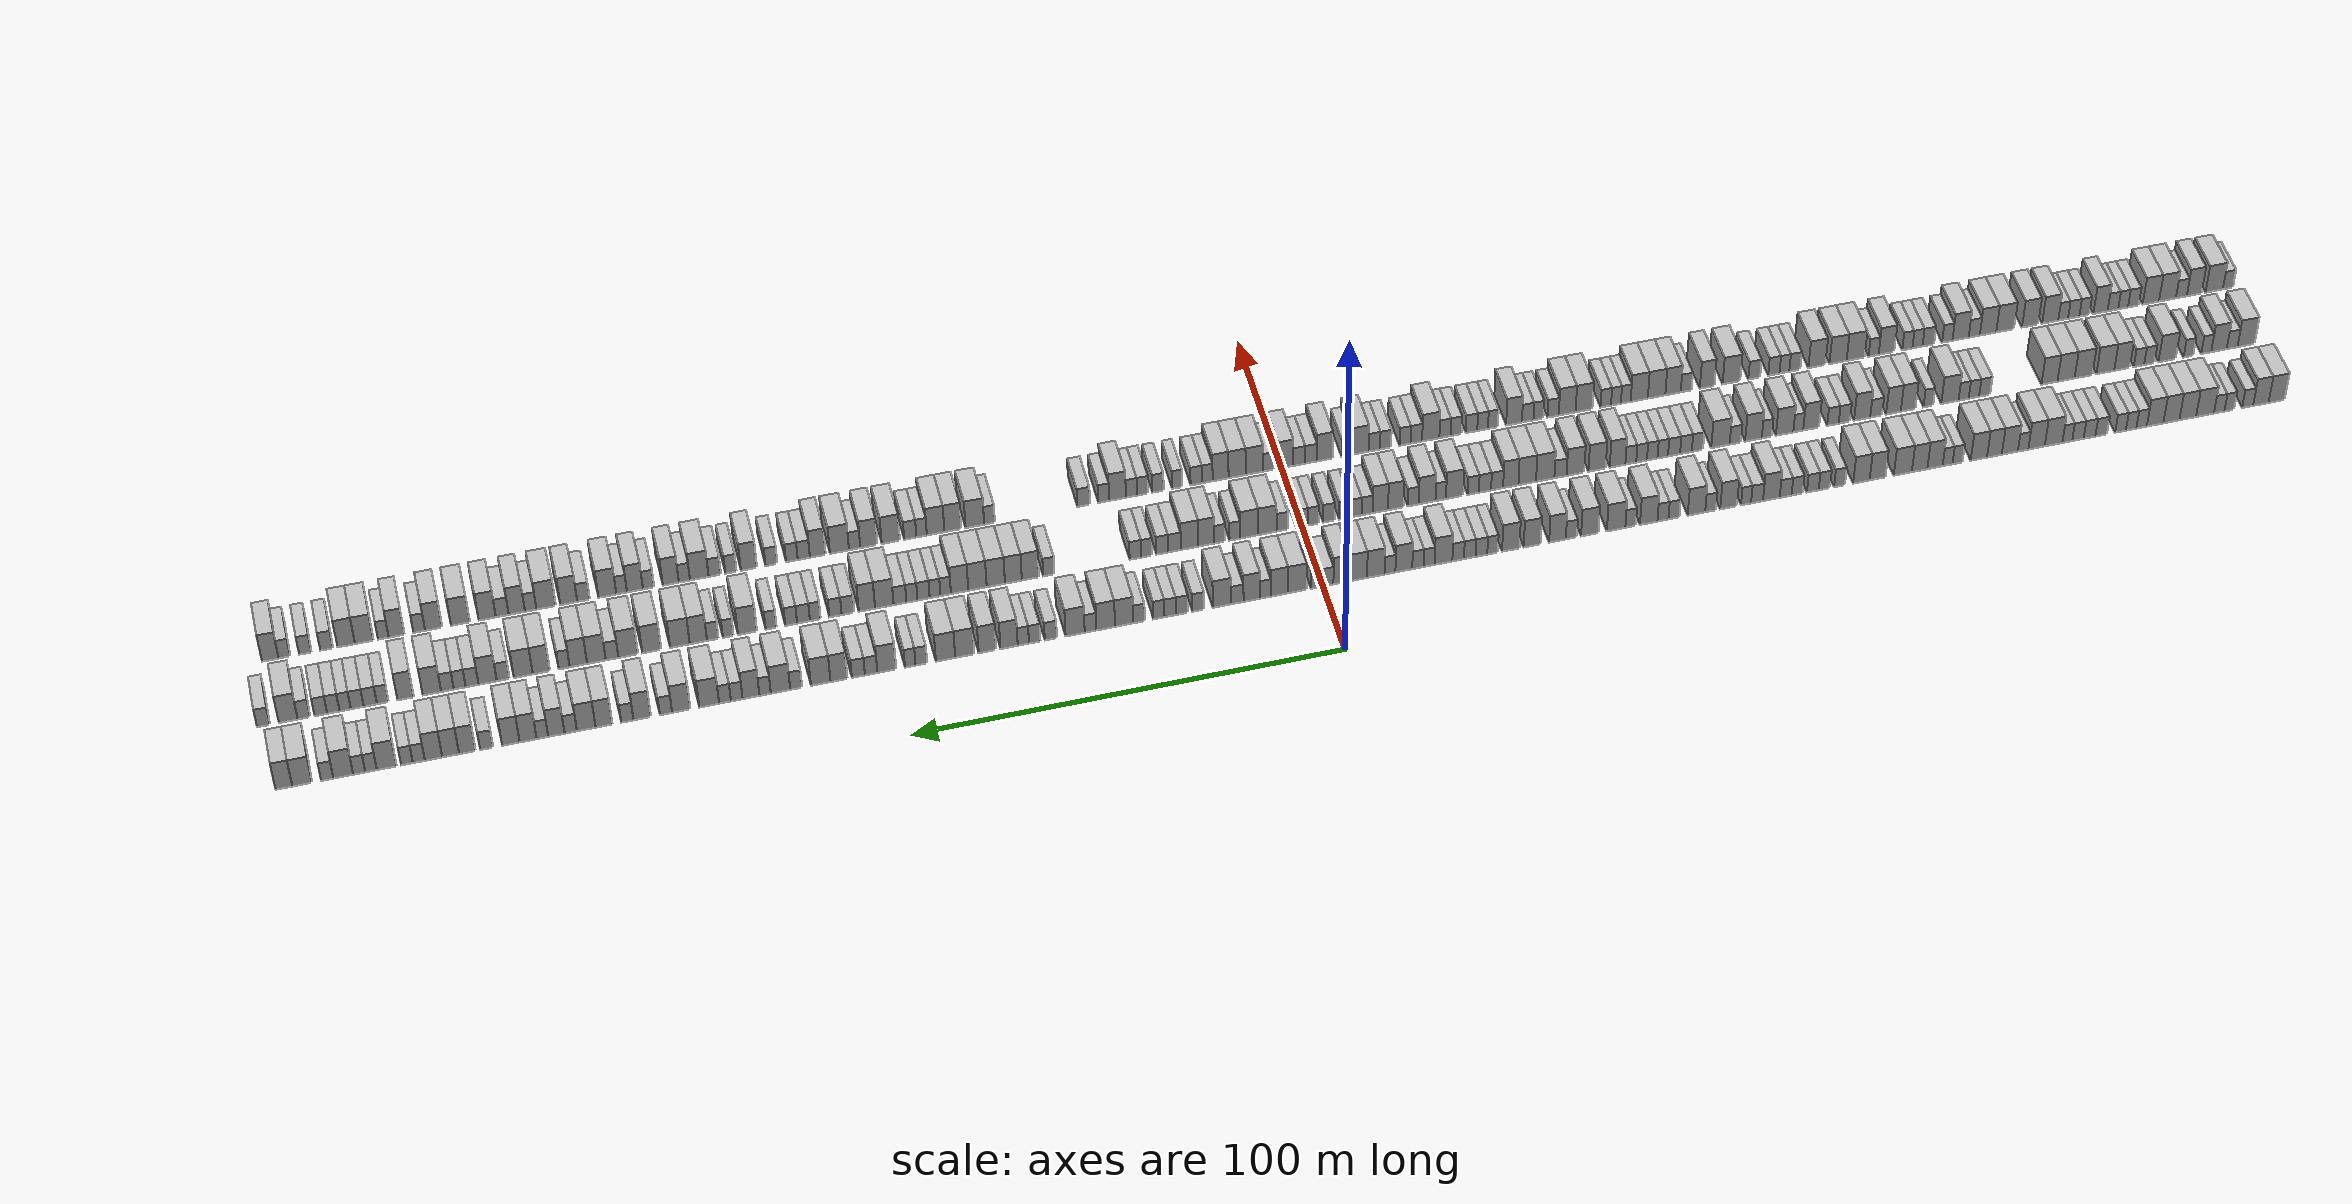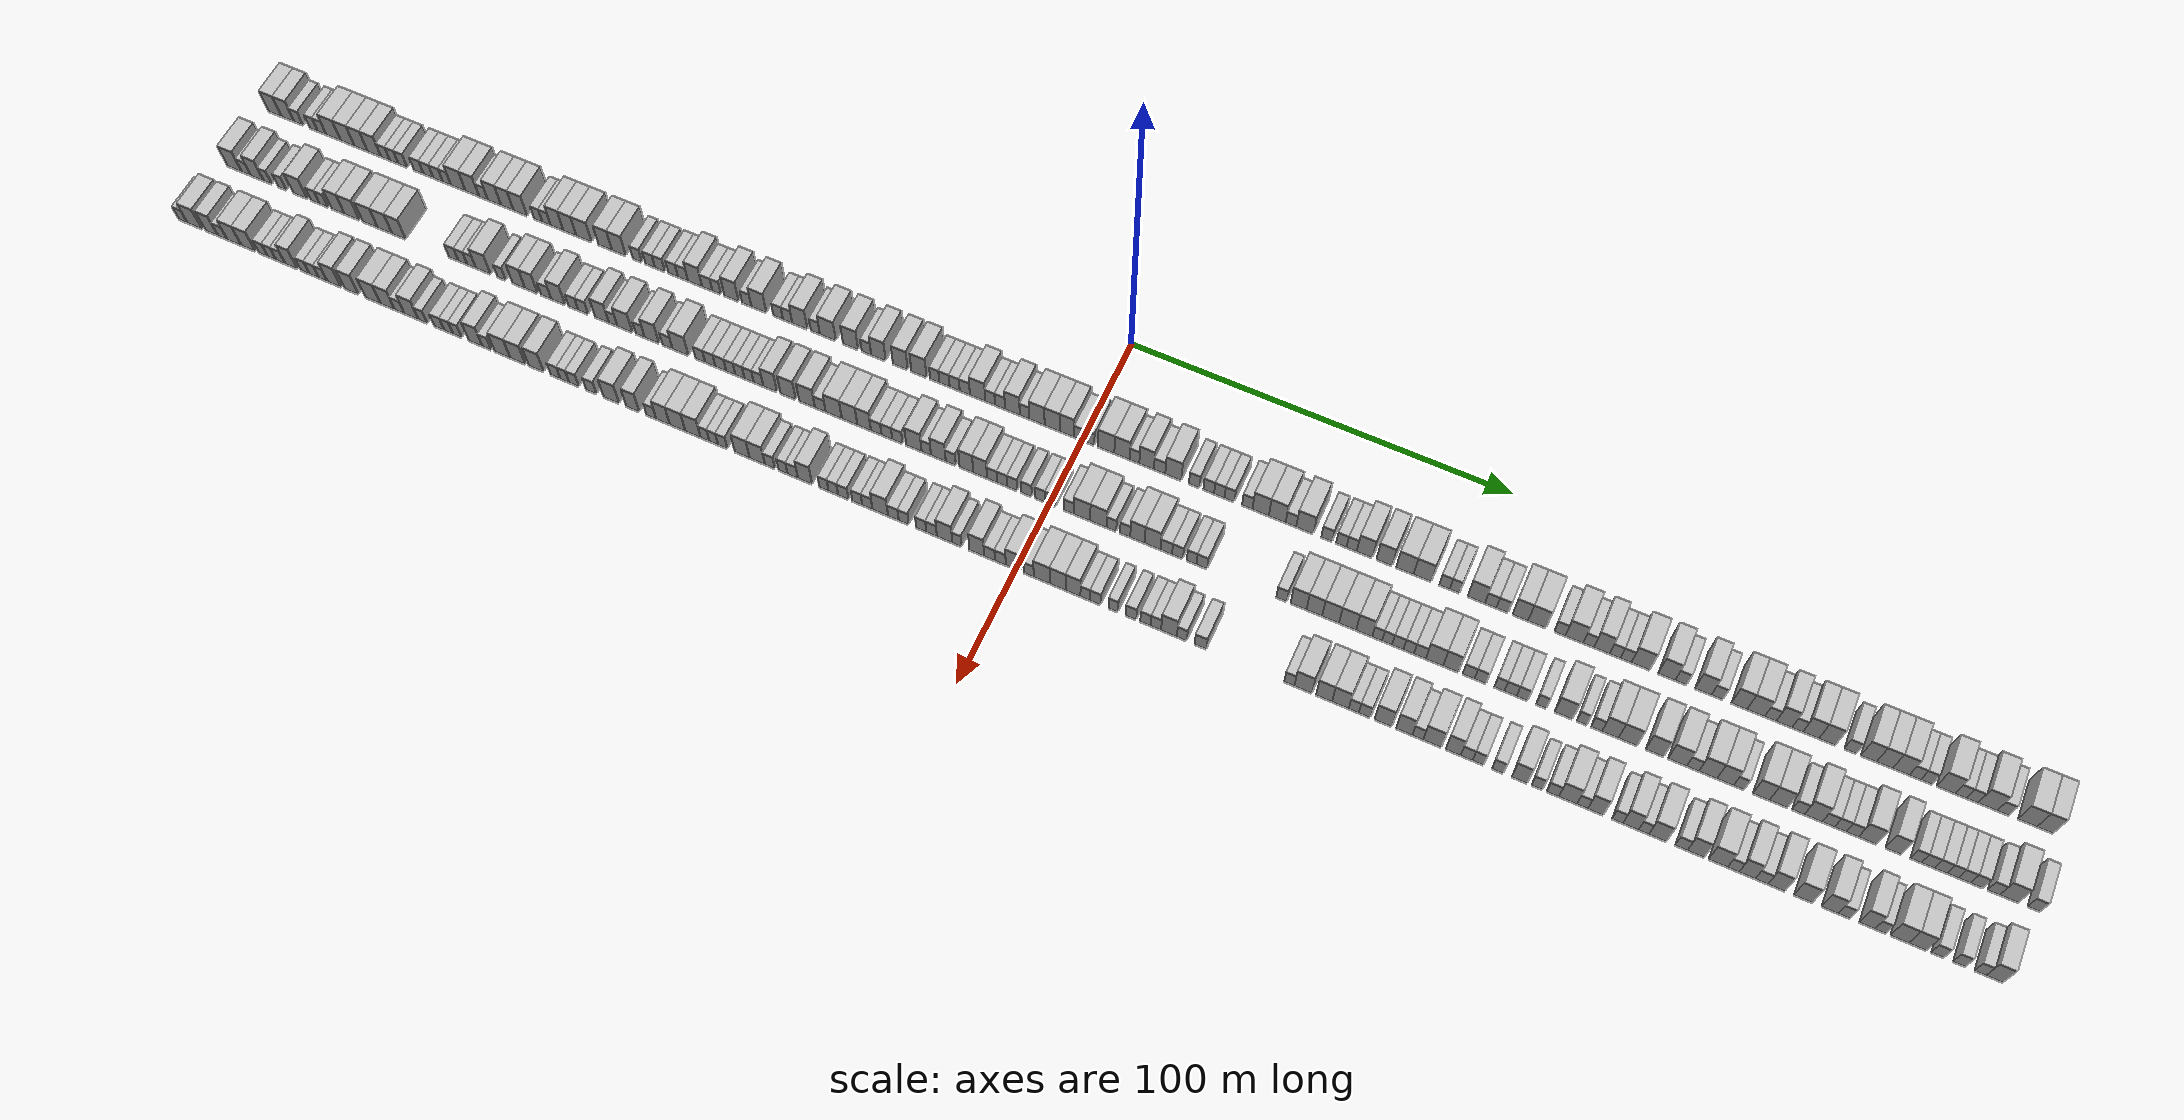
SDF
<sdf version="1.6">
 <world name="default">
  <scene>
   <sky><clouds><speed>12</speed></clouds></sky>
   <ambient>0.4 0.4 0.4 1</ambient>
   <background>0.7 0.7 0.7 1</background>
   <shadows>1</shadows>
  </scene>
  <gravity>0 0 -9.8066</gravity>
  <magnetic_field>6e-06 2.3e-05 -4.2e-05</magnetic_field>
  <physics default="0" name="default_physics" type="ode">
   <ode>
    <solver>
     <type>quick</type>
     <iters>10</iters>
     <sor>1.0</sor>
     <use_dynamic_moi_rescaling>0</use_dynamic_moi_rescaling>
    </solver>
    <constraints>
     <cfm>0</cfm>
     <erp>0.2</erp>
     <contact_max_correcting_vel>100</contact_max_correcting_vel>
     <contact_surface_layer>0.001</contact_surface_layer>
    </constraints>
   </ode>
   <max_step_size>0.004</max_step_size>
   <real_time_factor>1</real_time_factor>
   <real_time_update_rate>250</real_time_update_rate>
  </physics>
  <light name="sun" type="directional">
   <pose>0 0 10 0 0 0</pose>
   <diffuse>0.8 0.8 0.8 1</diffuse>
   <specular>0.2 0.2 0.2 1</specular>
   <attenuation>
    <range>1000</range>
    <constant>0.9</constant>
    <linear>0.01</linear>
    <quadratic>0.001</quadratic>
   </attenuation>
   <direction>-0.5 0.1 -0.9</direction>
  </light>
  <model name="building_1">
   <static>1</static>
   <pose>25.0000 -231.9561 0 0.000000 0.000000 0.000000</pose>
   <link name="link">
    <pose>0 0 4.50 0 0 0</pose>
    <collision name="collision"><geometry><box><size>10.0000 4.0878 9.0000</size></box></geometry></collision>
    <visual name="visual">
     <cast_shadows>0</cast_shadows>
     <geometry><box><size>10.0000 4.0878 9.0000</size></box></geometry>
     <material>
      <script>
       <uri>model://HANNAS_wall/materials/scripts</uri>
       <uri>model://HANNAS_wall/materials/textures</uri>
       <name>vrc/HANNAS_wall</name>
      </script>
     </material>
    </visual>
   </link>
  </model>
  <model name="building_2">
   <static>1</static>
   <pose>25.0000 -227.9771 0 0.000000 0.000000 0.000000</pose>
   <link name="link">
    <pose>0 0 4.50 0 0 0</pose>
    <collision name="collision"><geometry><box><size>10.0000 3.8702 9.0000</size></box></geometry></collision>
    <visual name="visual">
     <cast_shadows>0</cast_shadows>
     <geometry><box><size>10.0000 3.8702 9.0000</size></box></geometry>
     <material>
      <script>
       <uri>model://HANNAS_wall/materials/scripts</uri>
       <uri>model://HANNAS_wall/materials/textures</uri>
       <name>vrc/HANNAS_wall</name>
      </script>
     </material>
    </visual>
   </link>
  </model>
  <model name="building_3">
   <static>1</static>
   <pose>25.0000 -224.6804 0 0.000000 0.000000 0.000000</pose>
   <link name="link">
    <pose>0 0 3.00 0 0 0</pose>
    <collision name="collision"><geometry><box><size>10.0000 2.7232 6.0000</size></box></geometry></collision>
    <visual name="visual">
     <cast_shadows>0</cast_shadows>
     <geometry><box><size>10.0000 2.7232 6.0000</size></box></geometry>
     <material>
      <script>
       <uri>model://HANNAS_wall/materials/scripts</uri>
       <uri>model://HANNAS_wall/materials/textures</uri>
       <name>vrc/HANNAS_wall</name>
      </script>
     </material>
    </visual>
   </link>
  </model>
  <model name="building_4">
   <static>1</static>
   <pose>25.0000 -220.0909 0 0.000000 0.000000 0.000000</pose>
   <link name="link">
    <pose>0 0 3.00 0 0 0</pose>
    <collision name="collision"><geometry><box><size>10.0000 2.4558 6.0000</size></box></geometry></collision>
    <visual name="visual">
     <cast_shadows>0</cast_shadows>
     <geometry><box><size>10.0000 2.4558 6.0000</size></box></geometry>
     <material>
      <script>
       <uri>model://HANNAS_wall/materials/scripts</uri>
       <uri>model://HANNAS_wall/materials/textures</uri>
       <name>vrc/HANNAS_wall</name>
      </script>
     </material>
    </visual>
   </link>
  </model>
  <model name="building_5">
   <static>1</static>
   <pose>25.0000 -217.5487 0 0.000000 0.000000 0.000000</pose>
   <link name="link">
    <pose>0 0 3.00 0 0 0</pose>
    <collision name="collision"><geometry><box><size>10.0000 2.6286 6.0000</size></box></geometry></collision>
    <visual name="visual">
     <cast_shadows>0</cast_shadows>
     <geometry><box><size>10.0000 2.6286 6.0000</size></box></geometry>
     <material>
      <script>
       <uri>model://HANNAS_wall/materials/scripts</uri>
       <uri>model://HANNAS_wall/materials/textures</uri>
       <name>vrc/HANNAS_wall</name>
      </script>
     </material>
    </visual>
   </link>
  </model>
  <model name="building_6">
   <static>1</static>
   <pose>25.0000 -214.0006 0 0.000000 0.000000 0.000000</pose>
   <link name="link">
    <pose>0 0 4.50 0 0 0</pose>
    <collision name="collision"><geometry><box><size>10.0000 4.4677 9.0000</size></box></geometry></collision>
    <visual name="visual">
     <cast_shadows>0</cast_shadows>
     <geometry><box><size>10.0000 4.4677 9.0000</size></box></geometry>
     <material>
      <script>
       <uri>model://HANNAS_wall/materials/scripts</uri>
       <uri>model://HANNAS_wall/materials/textures</uri>
       <name>vrc/HANNAS_wall</name>
      </script>
     </material>
    </visual>
   </link>
  </model>
  <model name="building_7">
   <static>1</static>
   <pose>25.0000 -209.6781 0 0.000000 0.000000 0.000000</pose>
   <link name="link">
    <pose>0 0 4.50 0 0 0</pose>
    <collision name="collision"><geometry><box><size>10.0000 4.1772 9.0000</size></box></geometry></collision>
    <visual name="visual">
     <cast_shadows>0</cast_shadows>
     <geometry><box><size>10.0000 4.1772 9.0000</size></box></geometry>
     <material>
      <script>
       <uri>model://HANNAS_wall/materials/scripts</uri>
       <uri>model://HANNAS_wall/materials/textures</uri>
       <name>vrc/HANNAS_wall</name>
      </script>
     </material>
    </visual>
   </link>
  </model>
  <model name="building_8">
   <static>1</static>
   <pose>25.0000 -205.5924 0 0.000000 0.000000 0.000000</pose>
   <link name="link">
    <pose>0 0 4.50 0 0 0</pose>
    <collision name="collision"><geometry><box><size>10.0000 3.9943 9.0000</size></box></geometry></collision>
    <visual name="visual">
     <cast_shadows>0</cast_shadows>
     <geometry><box><size>10.0000 3.9943 9.0000</size></box></geometry>
     <material>
      <script>
       <uri>model://HANNAS_wall/materials/scripts</uri>
       <uri>model://HANNAS_wall/materials/textures</uri>
       <name>vrc/HANNAS_wall</name>
      </script>
     </material>
    </visual>
   </link>
  </model>
  <model name="building_9">
   <static>1</static>
   <pose>25.0000 -201.5379 0 0.000000 0.000000 0.000000</pose>
   <link name="link">
    <pose>0 0 4.50 0 0 0</pose>
    <collision name="collision"><geometry><box><size>10.0000 4.1145 9.0000</size></box></geometry></collision>
    <visual name="visual">
     <cast_shadows>0</cast_shadows>
     <geometry><box><size>10.0000 4.1145 9.0000</size></box></geometry>
     <material>
      <script>
       <uri>model://HANNAS_wall/materials/scripts</uri>
       <uri>model://HANNAS_wall/materials/textures</uri>
       <name>vrc/HANNAS_wall</name>
      </script>
     </material>
    </visual>
   </link>
  </model>
  <model name="building_10">
   <static>1</static>
   <pose>25.0000 -198.1714 0 0.000000 0.000000 0.000000</pose>
   <link name="link">
    <pose>0 0 3.00 0 0 0</pose>
    <collision name="collision"><geometry><box><size>10.0000 2.6185 6.0000</size></box></geometry></collision>
    <visual name="visual">
     <cast_shadows>0</cast_shadows>
     <geometry><box><size>10.0000 2.6185 6.0000</size></box></geometry>
     <material>
      <script>
       <uri>model://HANNAS_wall/materials/scripts</uri>
       <uri>model://HANNAS_wall/materials/textures</uri>
       <name>vrc/HANNAS_wall</name>
      </script>
     </material>
    </visual>
   </link>
  </model>
  <model name="building_11">
   <static>1</static>
   <pose>25.0000 -195.5604 0 0.000000 0.000000 0.000000</pose>
   <link name="link">
    <pose>0 0 3.00 0 0 0</pose>
    <collision name="collision"><geometry><box><size>10.0000 2.6036 6.0000</size></box></geometry></collision>
    <visual name="visual">
     <cast_shadows>0</cast_shadows>
     <geometry><box><size>10.0000 2.6036 6.0000</size></box></geometry>
     <material>
      <script>
       <uri>model://HANNAS_wall/materials/scripts</uri>
       <uri>model://HANNAS_wall/materials/textures</uri>
       <name>vrc/HANNAS_wall</name>
      </script>
     </material>
    </visual>
   </link>
  </model>
  <model name="building_12">
   <static>1</static>
   <pose>25.0000 -192.9126 0 0.000000 0.000000 0.000000</pose>
   <link name="link">
    <pose>0 0 3.00 0 0 0</pose>
    <collision name="collision"><geometry><box><size>10.0000 2.6920 6.0000</size></box></geometry></collision>
    <visual name="visual">
     <cast_shadows>0</cast_shadows>
     <geometry><box><size>10.0000 2.6920 6.0000</size></box></geometry>
     <material>
      <script>
       <uri>model://HANNAS_wall/materials/scripts</uri>
       <uri>model://HANNAS_wall/materials/textures</uri>
       <name>vrc/HANNAS_wall</name>
      </script>
     </material>
    </visual>
   </link>
  </model>
  <model name="building_13">
   <static>1</static>
   <pose>25.0000 -188.1085 0 0.000000 0.000000 0.000000</pose>
   <link name="link">
    <pose>0 0 3.00 0 0 0</pose>
    <collision name="collision"><geometry><box><size>10.0000 2.9162 6.0000</size></box></geometry></collision>
    <visual name="visual">
     <cast_shadows>0</cast_shadows>
     <geometry><box><size>10.0000 2.9162 6.0000</size></box></geometry>
     <material>
      <script>
       <uri>model://HANNAS_wall/materials/scripts</uri>
       <uri>model://HANNAS_wall/materials/textures</uri>
       <name>vrc/HANNAS_wall</name>
      </script>
     </material>
    </visual>
   </link>
  </model>
  <model name="building_14">
   <static>1</static>
   <pose>25.0000 -185.1995 0 0.000000 0.000000 0.000000</pose>
   <link name="link">
    <pose>0 0 3.00 0 0 0</pose>
    <collision name="collision"><geometry><box><size>10.0000 2.9018 6.0000</size></box></geometry></collision>
    <visual name="visual">
     <cast_shadows>0</cast_shadows>
     <geometry><box><size>10.0000 2.9018 6.0000</size></box></geometry>
     <material>
      <script>
       <uri>model://HANNAS_wall/materials/scripts</uri>
       <uri>model://HANNAS_wall/materials/textures</uri>
       <name>vrc/HANNAS_wall</name>
      </script>
     </material>
    </visual>
   </link>
  </model>
  <model name="building_15">
   <static>1</static>
   <pose>25.0000 -182.3323 0 0.000000 0.000000 0.000000</pose>
   <link name="link">
    <pose>0 0 3.00 0 0 0</pose>
    <collision name="collision"><geometry><box><size>10.0000 2.8326 6.0000</size></box></geometry></collision>
    <visual name="visual">
     <cast_shadows>0</cast_shadows>
     <geometry><box><size>10.0000 2.8326 6.0000</size></box></geometry>
     <material>
      <script>
       <uri>model://HANNAS_wall/materials/scripts</uri>
       <uri>model://HANNAS_wall/materials/textures</uri>
       <name>vrc/HANNAS_wall</name>
      </script>
     </material>
    </visual>
   </link>
  </model>
  <model name="building_16">
   <static>1</static>
   <pose>25.0000 -179.6947 0 0.000000 0.000000 0.000000</pose>
   <link name="link">
    <pose>0 0 3.00 0 0 0</pose>
    <collision name="collision"><geometry><box><size>10.0000 2.4427 6.0000</size></box></geometry></collision>
    <visual name="visual">
     <cast_shadows>0</cast_shadows>
     <geometry><box><size>10.0000 2.4427 6.0000</size></box></geometry>
     <material>
      <script>
       <uri>model://HANNAS_wall/materials/scripts</uri>
       <uri>model://HANNAS_wall/materials/textures</uri>
       <name>vrc/HANNAS_wall</name>
      </script>
     </material>
    </visual>
   </link>
  </model>
  <model name="building_17">
   <static>1</static>
   <pose>25.0000 -176.2881 0 0.000000 0.000000 0.000000</pose>
   <link name="link">
    <pose>0 0 4.50 0 0 0</pose>
    <collision name="collision"><geometry><box><size>10.0000 4.3705 9.0000</size></box></geometry></collision>
    <visual name="visual">
     <cast_shadows>0</cast_shadows>
     <geometry><box><size>10.0000 4.3705 9.0000</size></box></geometry>
     <material>
      <script>
       <uri>model://HANNAS_wall/materials/scripts</uri>
       <uri>model://HANNAS_wall/materials/textures</uri>
       <name>vrc/HANNAS_wall</name>
      </script>
     </material>
    </visual>
   </link>
  </model>
  <model name="building_18">
   <static>1</static>
   <pose>25.0000 -172.0715 0 0.000000 0.000000 0.000000</pose>
   <link name="link">
    <pose>0 0 4.50 0 0 0</pose>
    <collision name="collision"><geometry><box><size>10.0000 4.0628 9.0000</size></box></geometry></collision>
    <visual name="visual">
     <cast_shadows>0</cast_shadows>
     <geometry><box><size>10.0000 4.0628 9.0000</size></box></geometry>
     <material>
      <script>
       <uri>model://HANNAS_wall/materials/scripts</uri>
       <uri>model://HANNAS_wall/materials/textures</uri>
       <name>vrc/HANNAS_wall</name>
      </script>
     </material>
    </visual>
   </link>
  </model>
  <model name="building_19">
   <static>1</static>
   <pose>25.0000 -168.7544 0 0.000000 0.000000 0.000000</pose>
   <link name="link">
    <pose>0 0 3.00 0 0 0</pose>
    <collision name="collision"><geometry><box><size>10.0000 2.5712 6.0000</size></box></geometry></collision>
    <visual name="visual">
     <cast_shadows>0</cast_shadows>
     <geometry><box><size>10.0000 2.5712 6.0000</size></box></geometry>
     <material>
      <script>
       <uri>model://HANNAS_wall/materials/scripts</uri>
       <uri>model://HANNAS_wall/materials/textures</uri>
       <name>vrc/HANNAS_wall</name>
      </script>
     </material>
    </visual>
   </link>
  </model>
  <model name="building_20">
   <static>1</static>
   <pose>25.0000 -165.4810 0 0.000000 0.000000 0.000000</pose>
   <link name="link">
    <pose>0 0 4.50 0 0 0</pose>
    <collision name="collision"><geometry><box><size>10.0000 3.9756 9.0000</size></box></geometry></collision>
    <visual name="visual">
     <cast_shadows>0</cast_shadows>
     <geometry><box><size>10.0000 3.9756 9.0000</size></box></geometry>
     <material>
      <script>
       <uri>model://HANNAS_wall/materials/scripts</uri>
       <uri>model://HANNAS_wall/materials/textures</uri>
       <name>vrc/HANNAS_wall</name>
      </script>
     </material>
    </visual>
   </link>
  </model>
  <model name="building_21">
   <static>1</static>
   <pose>25.0000 -161.6683 0 0.000000 0.000000 0.000000</pose>
   <link name="link">
    <pose>0 0 4.50 0 0 0</pose>
    <collision name="collision"><geometry><box><size>10.0000 3.6498 9.0000</size></box></geometry></collision>
    <visual name="visual">
     <cast_shadows>0</cast_shadows>
     <geometry><box><size>10.0000 3.6498 9.0000</size></box></geometry>
     <material>
      <script>
       <uri>model://HANNAS_wall/materials/scripts</uri>
       <uri>model://HANNAS_wall/materials/textures</uri>
       <name>vrc/HANNAS_wall</name>
      </script>
     </material>
    </visual>
   </link>
  </model>
  <model name="building_22">
   <static>1</static>
   <pose>25.0000 -157.8268 0 0.000000 0.000000 0.000000</pose>
   <link name="link">
    <pose>0 0 4.50 0 0 0</pose>
    <collision name="collision"><geometry><box><size>10.0000 4.0331 9.0000</size></box></geometry></collision>
    <visual name="visual">
     <cast_shadows>0</cast_shadows>
     <geometry><box><size>10.0000 4.0331 9.0000</size></box></geometry>
     <material>
      <script>
       <uri>model://HANNAS_wall/materials/scripts</uri>
       <uri>model://HANNAS_wall/materials/textures</uri>
       <name>vrc/HANNAS_wall</name>
      </script>
     </material>
    </visual>
   </link>
  </model>
  <model name="building_23">
   <static>1</static>
   <pose>25.0000 -152.5795 0 0.000000 0.000000 0.000000</pose>
   <link name="link">
    <pose>0 0 3.00 0 0 0</pose>
    <collision name="collision"><geometry><box><size>10.0000 2.4616 6.0000</size></box></geometry></collision>
    <visual name="visual">
     <cast_shadows>0</cast_shadows>
     <geometry><box><size>10.0000 2.4616 6.0000</size></box></geometry>
     <material>
      <script>
       <uri>model://HANNAS_wall/materials/scripts</uri>
       <uri>model://HANNAS_wall/materials/textures</uri>
       <name>vrc/HANNAS_wall</name>
      </script>
     </material>
    </visual>
   </link>
  </model>
  <model name="building_24">
   <static>1</static>
   <pose>25.0000 -150.1322 0 0.000000 0.000000 0.000000</pose>
   <link name="link">
    <pose>0 0 3.00 0 0 0</pose>
    <collision name="collision"><geometry><box><size>10.0000 2.4331 6.0000</size></box></geometry></collision>
    <visual name="visual">
     <cast_shadows>0</cast_shadows>
     <geometry><box><size>10.0000 2.4331 6.0000</size></box></geometry>
     <material>
      <script>
       <uri>model://HANNAS_wall/materials/scripts</uri>
       <uri>model://HANNAS_wall/materials/textures</uri>
       <name>vrc/HANNAS_wall</name>
      </script>
     </material>
    </visual>
   </link>
  </model>
  <model name="building_25">
   <static>1</static>
   <pose>25.0000 -147.0416 0 0.000000 0.000000 0.000000</pose>
   <link name="link">
    <pose>0 0 4.50 0 0 0</pose>
    <collision name="collision"><geometry><box><size>10.0000 3.7482 9.0000</size></box></geometry></collision>
    <visual name="visual">
     <cast_shadows>0</cast_shadows>
     <geometry><box><size>10.0000 3.7482 9.0000</size></box></geometry>
     <material>
      <script>
       <uri>model://HANNAS_wall/materials/scripts</uri>
       <uri>model://HANNAS_wall/materials/textures</uri>
       <name>vrc/HANNAS_wall</name>
      </script>
     </material>
    </visual>
   </link>
  </model>
  <model name="building_26">
   <static>1</static>
   <pose>25.0000 -143.2613 0 0.000000 0.000000 0.000000</pose>
   <link name="link">
    <pose>0 0 4.50 0 0 0</pose>
    <collision name="collision"><geometry><box><size>10.0000 3.8124 9.0000</size></box></geometry></collision>
    <visual name="visual">
     <cast_shadows>0</cast_shadows>
     <geometry><box><size>10.0000 3.8124 9.0000</size></box></geometry>
     <material>
      <script>
       <uri>model://HANNAS_wall/materials/scripts</uri>
       <uri>model://HANNAS_wall/materials/textures</uri>
       <name>vrc/HANNAS_wall</name>
      </script>
     </material>
    </visual>
   </link>
  </model>
  <model name="building_27">
   <static>1</static>
   <pose>25.0000 -139.1423 0 0.000000 0.000000 0.000000</pose>
   <link name="link">
    <pose>0 0 4.50 0 0 0</pose>
    <collision name="collision"><geometry><box><size>10.0000 4.4255 9.0000</size></box></geometry></collision>
    <visual name="visual">
     <cast_shadows>0</cast_shadows>
     <geometry><box><size>10.0000 4.4255 9.0000</size></box></geometry>
     <material>
      <script>
       <uri>model://HANNAS_wall/materials/scripts</uri>
       <uri>model://HANNAS_wall/materials/textures</uri>
       <name>vrc/HANNAS_wall</name>
      </script>
     </material>
    </visual>
   </link>
  </model>
  <model name="building_28">
   <static>1</static>
   <pose>25.0000 -132.9723 0 0.000000 0.000000 0.000000</pose>
   <link name="link">
    <pose>0 0 4.50 0 0 0</pose>
    <collision name="collision"><geometry><box><size>10.0000 3.9146 9.0000</size></box></geometry></collision>
    <visual name="visual">
     <cast_shadows>0</cast_shadows>
     <geometry><box><size>10.0000 3.9146 9.0000</size></box></geometry>
     <material>
      <script>
       <uri>model://HANNAS_wall/materials/scripts</uri>
       <uri>model://HANNAS_wall/materials/textures</uri>
       <name>vrc/HANNAS_wall</name>
      </script>
     </material>
    </visual>
   </link>
  </model>
  <model name="building_29">
   <static>1</static>
   <pose>25.0000 -128.9965 0 0.000000 0.000000 0.000000</pose>
   <link name="link">
    <pose>0 0 4.50 0 0 0</pose>
    <collision name="collision"><geometry><box><size>10.0000 4.0370 9.0000</size></box></geometry></collision>
    <visual name="visual">
     <cast_shadows>0</cast_shadows>
     <geometry><box><size>10.0000 4.0370 9.0000</size></box></geometry>
     <material>
      <script>
       <uri>model://HANNAS_wall/materials/scripts</uri>
       <uri>model://HANNAS_wall/materials/textures</uri>
       <name>vrc/HANNAS_wall</name>
      </script>
     </material>
    </visual>
   </link>
  </model>
  <model name="building_30">
   <static>1</static>
   <pose>25.0000 -123.6580 0 0.000000 0.000000 0.000000</pose>
   <link name="link">
    <pose>0 0 3.00 0 0 0</pose>
    <collision name="collision"><geometry><box><size>10.0000 2.6400 6.0000</size></box></geometry></collision>
    <visual name="visual">
     <cast_shadows>0</cast_shadows>
     <geometry><box><size>10.0000 2.6400 6.0000</size></box></geometry>
     <material>
      <script>
       <uri>model://HANNAS_wall/materials/scripts</uri>
       <uri>model://HANNAS_wall/materials/textures</uri>
       <name>vrc/HANNAS_wall</name>
      </script>
     </material>
    </visual>
   </link>
  </model>
  <model name="building_31">
   <static>1</static>
   <pose>25.0000 -119.9525 0 0.000000 0.000000 0.000000</pose>
   <link name="link">
    <pose>0 0 3.00 0 0 0</pose>
    <collision name="collision"><geometry><box><size>10.0000 2.7710 6.0000</size></box></geometry></collision>
    <visual name="visual">
     <cast_shadows>0</cast_shadows>
     <geometry><box><size>10.0000 2.7710 6.0000</size></box></geometry>
     <material>
      <script>
       <uri>model://HANNAS_wall/materials/scripts</uri>
       <uri>model://HANNAS_wall/materials/textures</uri>
       <name>vrc/HANNAS_wall</name>
      </script>
     </material>
    </visual>
   </link>
  </model>
  <model name="building_32">
   <static>1</static>
   <pose>25.0000 -117.1328 0 0.000000 0.000000 0.000000</pose>
   <link name="link">
    <pose>0 0 3.00 0 0 0</pose>
    <collision name="collision"><geometry><box><size>10.0000 2.8685 6.0000</size></box></geometry></collision>
    <visual name="visual">
     <cast_shadows>0</cast_shadows>
     <geometry><box><size>10.0000 2.8685 6.0000</size></box></geometry>
     <material>
      <script>
       <uri>model://HANNAS_wall/materials/scripts</uri>
       <uri>model://HANNAS_wall/materials/textures</uri>
       <name>vrc/HANNAS_wall</name>
      </script>
     </material>
    </visual>
   </link>
  </model>
  <model name="building_33">
   <static>1</static>
   <pose>25.0000 -113.3362 0 0.000000 0.000000 0.000000</pose>
   <link name="link">
    <pose>0 0 3.00 0 0 0</pose>
    <collision name="collision"><geometry><box><size>10.0000 2.7246 6.0000</size></box></geometry></collision>
    <visual name="visual">
     <cast_shadows>0</cast_shadows>
     <geometry><box><size>10.0000 2.7246 6.0000</size></box></geometry>
     <material>
      <script>
       <uri>model://HANNAS_wall/materials/scripts</uri>
       <uri>model://HANNAS_wall/materials/textures</uri>
       <name>vrc/HANNAS_wall</name>
      </script>
     </material>
    </visual>
   </link>
  </model>
  <model name="building_34">
   <static>1</static>
   <pose>25.0000 -110.5225 0 0.000000 0.000000 0.000000</pose>
   <link name="link">
    <pose>0 0 3.00 0 0 0</pose>
    <collision name="collision"><geometry><box><size>10.0000 2.9027 6.0000</size></box></geometry></collision>
    <visual name="visual">
     <cast_shadows>0</cast_shadows>
     <geometry><box><size>10.0000 2.9027 6.0000</size></box></geometry>
     <material>
      <script>
       <uri>model://HANNAS_wall/materials/scripts</uri>
       <uri>model://HANNAS_wall/materials/textures</uri>
       <name>vrc/HANNAS_wall</name>
      </script>
     </material>
    </visual>
   </link>
  </model>
  <model name="building_35">
   <static>1</static>
   <pose>25.0000 -107.0426 0 0.000000 0.000000 0.000000</pose>
   <link name="link">
    <pose>0 0 4.50 0 0 0</pose>
    <collision name="collision"><geometry><box><size>10.0000 4.0572 9.0000</size></box></geometry></collision>
    <visual name="visual">
     <cast_shadows>0</cast_shadows>
     <geometry><box><size>10.0000 4.0572 9.0000</size></box></geometry>
     <material>
      <script>
       <uri>model://HANNAS_wall/materials/scripts</uri>
       <uri>model://HANNAS_wall/materials/textures</uri>
       <name>vrc/HANNAS_wall</name>
      </script>
     </material>
    </visual>
   </link>
  </model>
  <model name="building_36">
   <static>1</static>
   <pose>25.0000 -103.5754 0 0.000000 0.000000 0.000000</pose>
   <link name="link">
    <pose>0 0 3.00 0 0 0</pose>
    <collision name="collision"><geometry><box><size>10.0000 2.8773 6.0000</size></box></geometry></collision>
    <visual name="visual">
     <cast_shadows>0</cast_shadows>
     <geometry><box><size>10.0000 2.8773 6.0000</size></box></geometry>
     <material>
      <script>
       <uri>model://HANNAS_wall/materials/scripts</uri>
       <uri>model://HANNAS_wall/materials/textures</uri>
       <name>vrc/HANNAS_wall</name>
      </script>
     </material>
    </visual>
   </link>
  </model>
  <model name="building_37">
   <static>1</static>
   <pose>25.0000 -100.9123 0 0.000000 0.000000 0.000000</pose>
   <link name="link">
    <pose>0 0 3.00 0 0 0</pose>
    <collision name="collision"><geometry><box><size>10.0000 2.4487 6.0000</size></box></geometry></collision>
    <visual name="visual">
     <cast_shadows>0</cast_shadows>
     <geometry><box><size>10.0000 2.4487 6.0000</size></box></geometry>
     <material>
      <script>
       <uri>model://HANNAS_wall/materials/scripts</uri>
       <uri>model://HANNAS_wall/materials/textures</uri>
       <name>vrc/HANNAS_wall</name>
      </script>
     </material>
    </visual>
   </link>
  </model>
  <model name="building_38">
   <static>1</static>
   <pose>25.0000 -96.6644 0 0.000000 0.000000 0.000000</pose>
   <link name="link">
    <pose>0 0 4.50 0 0 0</pose>
    <collision name="collision"><geometry><box><size>10.0000 4.0472 9.0000</size></box></geometry></collision>
    <visual name="visual">
     <cast_shadows>0</cast_shadows>
     <geometry><box><size>10.0000 4.0472 9.0000</size></box></geometry>
     <material>
      <script>
       <uri>model://HANNAS_wall/materials/scripts</uri>
       <uri>model://HANNAS_wall/materials/textures</uri>
       <name>vrc/HANNAS_wall</name>
      </script>
     </material>
    </visual>
   </link>
  </model>
  <model name="building_39">
   <static>1</static>
   <pose>25.0000 -92.3256 0 0.000000 0.000000 0.000000</pose>
   <link name="link">
    <pose>0 0 3.00 0 0 0</pose>
    <collision name="collision"><geometry><box><size>10.0000 2.6303 6.0000</size></box></geometry></collision>
    <visual name="visual">
     <cast_shadows>0</cast_shadows>
     <geometry><box><size>10.0000 2.6303 6.0000</size></box></geometry>
     <material>
      <script>
       <uri>model://HANNAS_wall/materials/scripts</uri>
       <uri>model://HANNAS_wall/materials/textures</uri>
       <name>vrc/HANNAS_wall</name>
      </script>
     </material>
    </visual>
   </link>
  </model>
  <model name="building_40">
   <static>1</static>
   <pose>25.0000 -88.8999 0 0.000000 0.000000 0.000000</pose>
   <link name="link">
    <pose>0 0 4.50 0 0 0</pose>
    <collision name="collision"><geometry><box><size>10.0000 4.2213 9.0000</size></box></geometry></collision>
    <visual name="visual">
     <cast_shadows>0</cast_shadows>
     <geometry><box><size>10.0000 4.2213 9.0000</size></box></geometry>
     <material>
      <script>
       <uri>model://HANNAS_wall/materials/scripts</uri>
       <uri>model://HANNAS_wall/materials/textures</uri>
       <name>vrc/HANNAS_wall</name>
      </script>
     </material>
    </visual>
   </link>
  </model>
  <model name="building_41">
   <static>1</static>
   <pose>25.0000 -83.4641 0 0.000000 0.000000 0.000000</pose>
   <link name="link">
    <pose>0 0 3.00 0 0 0</pose>
    <collision name="collision"><geometry><box><size>10.0000 2.6504 6.0000</size></box></geometry></collision>
    <visual name="visual">
     <cast_shadows>0</cast_shadows>
     <geometry><box><size>10.0000 2.6504 6.0000</size></box></geometry>
     <material>
      <script>
       <uri>model://HANNAS_wall/materials/scripts</uri>
       <uri>model://HANNAS_wall/materials/textures</uri>
       <name>vrc/HANNAS_wall</name>
      </script>
     </material>
    </visual>
   </link>
  </model>
  <model name="building_42">
   <static>1</static>
   <pose>25.0000 -80.8119 0 0.000000 0.000000 0.000000</pose>
   <link name="link">
    <pose>0 0 3.00 0 0 0</pose>
    <collision name="collision"><geometry><box><size>10.0000 2.6540 6.0000</size></box></geometry></collision>
    <visual name="visual">
     <cast_shadows>0</cast_shadows>
     <geometry><box><size>10.0000 2.6540 6.0000</size></box></geometry>
     <material>
      <script>
       <uri>model://HANNAS_wall/materials/scripts</uri>
       <uri>model://HANNAS_wall/materials/textures</uri>
       <name>vrc/HANNAS_wall</name>
      </script>
     </material>
    </visual>
   </link>
  </model>
  <model name="building_43">
   <static>1</static>
   <pose>25.0000 -77.3776 0 0.000000 0.000000 0.000000</pose>
   <link name="link">
    <pose>0 0 4.50 0 0 0</pose>
    <collision name="collision"><geometry><box><size>10.0000 4.2144 9.0000</size></box></geometry></collision>
    <visual name="visual">
     <cast_shadows>0</cast_shadows>
     <geometry><box><size>10.0000 4.2144 9.0000</size></box></geometry>
     <material>
      <script>
       <uri>model://HANNAS_wall/materials/scripts</uri>
       <uri>model://HANNAS_wall/materials/textures</uri>
       <name>vrc/HANNAS_wall</name>
      </script>
     </material>
    </visual>
   </link>
  </model>
  <model name="building_44">
   <static>1</static>
   <pose>25.0000 -73.0093 0 0.000000 0.000000 0.000000</pose>
   <link name="link">
    <pose>0 0 3.00 0 0 0</pose>
    <collision name="collision"><geometry><box><size>10.0000 2.5224 6.0000</size></box></geometry></collision>
    <visual name="visual">
     <cast_shadows>0</cast_shadows>
     <geometry><box><size>10.0000 2.5224 6.0000</size></box></geometry>
     <material>
      <script>
       <uri>model://HANNAS_wall/materials/scripts</uri>
       <uri>model://HANNAS_wall/materials/textures</uri>
       <name>vrc/HANNAS_wall</name>
      </script>
     </material>
    </visual>
   </link>
  </model>
  <model name="building_45">
   <static>1</static>
   <pose>25.0000 -69.5281 0 0.000000 0.000000 0.000000</pose>
   <link name="link">
    <pose>0 0 4.50 0 0 0</pose>
    <collision name="collision"><geometry><box><size>10.0000 4.4400 9.0000</size></box></geometry></collision>
    <visual name="visual">
     <cast_shadows>0</cast_shadows>
     <geometry><box><size>10.0000 4.4400 9.0000</size></box></geometry>
     <material>
      <script>
       <uri>model://HANNAS_wall/materials/scripts</uri>
       <uri>model://HANNAS_wall/materials/textures</uri>
       <name>vrc/HANNAS_wall</name>
      </script>
     </material>
    </visual>
   </link>
  </model>
  <model name="building_46">
   <static>1</static>
   <pose>25.0000 -63.2074 0 0.000000 0.000000 0.000000</pose>
   <link name="link">
    <pose>0 0 4.50 0 0 0</pose>
    <collision name="collision"><geometry><box><size>10.0000 4.2015 9.0000</size></box></geometry></collision>
    <visual name="visual">
     <cast_shadows>0</cast_shadows>
     <geometry><box><size>10.0000 4.2015 9.0000</size></box></geometry>
     <material>
      <script>
       <uri>model://HANNAS_wall/materials/scripts</uri>
       <uri>model://HANNAS_wall/materials/textures</uri>
       <name>vrc/HANNAS_wall</name>
      </script>
     </material>
    </visual>
   </link>
  </model>
  <model name="building_47">
   <static>1</static>
   <pose>25.0000 -58.7870 0 0.000000 0.000000 0.000000</pose>
   <link name="link">
    <pose>0 0 3.00 0 0 0</pose>
    <collision name="collision"><geometry><box><size>10.0000 2.6392 6.0000</size></box></geometry></collision>
    <visual name="visual">
     <cast_shadows>0</cast_shadows>
     <geometry><box><size>10.0000 2.6392 6.0000</size></box></geometry>
     <material>
      <script>
       <uri>model://HANNAS_wall/materials/scripts</uri>
       <uri>model://HANNAS_wall/materials/textures</uri>
       <name>vrc/HANNAS_wall</name>
      </script>
     </material>
    </visual>
   </link>
  </model>
  <model name="building_48">
   <static>1</static>
   <pose>25.0000 -55.4667 0 0.000000 0.000000 0.000000</pose>
   <link name="link">
    <pose>0 0 4.50 0 0 0</pose>
    <collision name="collision"><geometry><box><size>10.0000 4.0013 9.0000</size></box></geometry></collision>
    <visual name="visual">
     <cast_shadows>0</cast_shadows>
     <geometry><box><size>10.0000 4.0013 9.0000</size></box></geometry>
     <material>
      <script>
       <uri>model://HANNAS_wall/materials/scripts</uri>
       <uri>model://HANNAS_wall/materials/textures</uri>
       <name>vrc/HANNAS_wall</name>
      </script>
     </material>
    </visual>
   </link>
  </model>
  <model name="building_49">
   <static>1</static>
   <pose>25.0000 -49.4250 0 0.000000 0.000000 0.000000</pose>
   <link name="link">
    <pose>0 0 4.50 0 0 0</pose>
    <collision name="collision"><geometry><box><size>10.0000 4.0821 9.0000</size></box></geometry></collision>
    <visual name="visual">
     <cast_shadows>0</cast_shadows>
     <geometry><box><size>10.0000 4.0821 9.0000</size></box></geometry>
     <material>
      <script>
       <uri>model://HANNAS_wall/materials/scripts</uri>
       <uri>model://HANNAS_wall/materials/textures</uri>
       <name>vrc/HANNAS_wall</name>
      </script>
     </material>
    </visual>
   </link>
  </model>
  <model name="building_50">
   <static>1</static>
   <pose>25.0000 -44.3049 0 0.000000 0.000000 0.000000</pose>
   <link name="link">
    <pose>0 0 4.50 0 0 0</pose>
    <collision name="collision"><geometry><box><size>10.0000 4.1583 9.0000</size></box></geometry></collision>
    <visual name="visual">
     <cast_shadows>0</cast_shadows>
     <geometry><box><size>10.0000 4.1583 9.0000</size></box></geometry>
     <material>
      <script>
       <uri>model://HANNAS_wall/materials/scripts</uri>
       <uri>model://HANNAS_wall/materials/textures</uri>
       <name>vrc/HANNAS_wall</name>
      </script>
     </material>
    </visual>
   </link>
  </model>
  <model name="building_51">
   <static>1</static>
   <pose>25.0000 -39.9633 0 0.000000 0.000000 0.000000</pose>
   <link name="link">
    <pose>0 0 3.00 0 0 0</pose>
    <collision name="collision"><geometry><box><size>10.0000 2.5249 6.0000</size></box></geometry></collision>
    <visual name="visual">
     <cast_shadows>0</cast_shadows>
     <geometry><box><size>10.0000 2.5249 6.0000</size></box></geometry>
     <material>
      <script>
       <uri>model://HANNAS_wall/materials/scripts</uri>
       <uri>model://HANNAS_wall/materials/textures</uri>
       <name>vrc/HANNAS_wall</name>
      </script>
     </material>
    </visual>
   </link>
  </model>
  <model name="building_52">
   <static>1</static>
   <pose>25.0000 -37.3032 0 0.000000 0.000000 0.000000</pose>
   <link name="link">
    <pose>0 0 3.00 0 0 0</pose>
    <collision name="collision"><geometry><box><size>10.0000 2.7953 6.0000</size></box></geometry></collision>
    <visual name="visual">
     <cast_shadows>0</cast_shadows>
     <geometry><box><size>10.0000 2.7953 6.0000</size></box></geometry>
     <material>
      <script>
       <uri>model://HANNAS_wall/materials/scripts</uri>
       <uri>model://HANNAS_wall/materials/textures</uri>
       <name>vrc/HANNAS_wall</name>
      </script>
     </material>
    </visual>
   </link>
  </model>
  <model name="building_53">
   <static>1</static>
   <pose>25.0000 -34.5384 0 0.000000 0.000000 0.000000</pose>
   <link name="link">
    <pose>0 0 3.00 0 0 0</pose>
    <collision name="collision"><geometry><box><size>10.0000 2.7344 6.0000</size></box></geometry></collision>
    <visual name="visual">
     <cast_shadows>0</cast_shadows>
     <geometry><box><size>10.0000 2.7344 6.0000</size></box></geometry>
     <material>
      <script>
       <uri>model://HANNAS_wall/materials/scripts</uri>
       <uri>model://HANNAS_wall/materials/textures</uri>
       <name>vrc/HANNAS_wall</name>
      </script>
     </material>
    </visual>
   </link>
  </model>
  <model name="building_54">
   <static>1</static>
   <pose>25.0000 -31.7763 0 0.000000 0.000000 0.000000</pose>
   <link name="link">
    <pose>0 0 3.00 0 0 0</pose>
    <collision name="collision"><geometry><box><size>10.0000 2.7899 6.0000</size></box></geometry></collision>
    <visual name="visual">
     <cast_shadows>0</cast_shadows>
     <geometry><box><size>10.0000 2.7899 6.0000</size></box></geometry>
     <material>
      <script>
       <uri>model://HANNAS_wall/materials/scripts</uri>
       <uri>model://HANNAS_wall/materials/textures</uri>
       <name>vrc/HANNAS_wall</name>
      </script>
     </material>
    </visual>
   </link>
  </model>
  <model name="building_55">
   <static>1</static>
   <pose>25.0000 -28.2948 0 0.000000 0.000000 0.000000</pose>
   <link name="link">
    <pose>0 0 4.50 0 0 0</pose>
    <collision name="collision"><geometry><box><size>10.0000 4.1730 9.0000</size></box></geometry></collision>
    <visual name="visual">
     <cast_shadows>0</cast_shadows>
     <geometry><box><size>10.0000 4.1730 9.0000</size></box></geometry>
     <material>
      <script>
       <uri>model://HANNAS_wall/materials/scripts</uri>
       <uri>model://HANNAS_wall/materials/textures</uri>
       <name>vrc/HANNAS_wall</name>
      </script>
     </material>
    </visual>
   </link>
  </model>
  <model name="building_56">
   <static>1</static>
   <pose>25.0000 -24.8899 0 0.000000 0.000000 0.000000</pose>
   <link name="link">
    <pose>0 0 3.00 0 0 0</pose>
    <collision name="collision"><geometry><box><size>10.0000 2.6368 6.0000</size></box></geometry></collision>
    <visual name="visual">
     <cast_shadows>0</cast_shadows>
     <geometry><box><size>10.0000 2.6368 6.0000</size></box></geometry>
     <material>
      <script>
       <uri>model://HANNAS_wall/materials/scripts</uri>
       <uri>model://HANNAS_wall/materials/textures</uri>
       <name>vrc/HANNAS_wall</name>
      </script>
     </material>
    </visual>
   </link>
  </model>
  <model name="building_57">
   <static>1</static>
   <pose>25.0000 -22.2199 0 0.000000 0.000000 0.000000</pose>
   <link name="link">
    <pose>0 0 3.00 0 0 0</pose>
    <collision name="collision"><geometry><box><size>10.0000 2.7033 6.0000</size></box></geometry></collision>
    <visual name="visual">
     <cast_shadows>0</cast_shadows>
     <geometry><box><size>10.0000 2.7033 6.0000</size></box></geometry>
     <material>
      <script>
       <uri>model://HANNAS_wall/materials/scripts</uri>
       <uri>model://HANNAS_wall/materials/textures</uri>
       <name>vrc/HANNAS_wall</name>
      </script>
     </material>
    </visual>
   </link>
  </model>
  <model name="building_58">
   <static>1</static>
   <pose>25.0000 -18.8673 0 0.000000 0.000000 0.000000</pose>
   <link name="link">
    <pose>0 0 4.50 0 0 0</pose>
    <collision name="collision"><geometry><box><size>10.0000 4.0019 9.0000</size></box></geometry></collision>
    <visual name="visual">
     <cast_shadows>0</cast_shadows>
     <geometry><box><size>10.0000 4.0019 9.0000</size></box></geometry>
     <material>
      <script>
       <uri>model://HANNAS_wall/materials/scripts</uri>
       <uri>model://HANNAS_wall/materials/textures</uri>
       <name>vrc/HANNAS_wall</name>
      </script>
     </material>
    </visual>
   </link>
  </model>
  <model name="building_59">
   <static>1</static>
   <pose>25.0000 -15.6227 0 0.000000 0.000000 0.000000</pose>
   <link name="link">
    <pose>0 0 3.00 0 0 0</pose>
    <collision name="collision"><geometry><box><size>10.0000 2.4872 6.0000</size></box></geometry></collision>
    <visual name="visual">
     <cast_shadows>0</cast_shadows>
     <geometry><box><size>10.0000 2.4872 6.0000</size></box></geometry>
     <material>
      <script>
       <uri>model://HANNAS_wall/materials/scripts</uri>
       <uri>model://HANNAS_wall/materials/textures</uri>
       <name>vrc/HANNAS_wall</name>
      </script>
     </material>
    </visual>
   </link>
  </model>
  <model name="building_60">
   <static>1</static>
   <pose>25.0000 -12.2853 0 0.000000 0.000000 0.000000</pose>
   <link name="link">
    <pose>0 0 4.50 0 0 0</pose>
    <collision name="collision"><geometry><box><size>10.0000 4.1877 9.0000</size></box></geometry></collision>
    <visual name="visual">
     <cast_shadows>0</cast_shadows>
     <geometry><box><size>10.0000 4.1877 9.0000</size></box></geometry>
     <material>
      <script>
       <uri>model://HANNAS_wall/materials/scripts</uri>
       <uri>model://HANNAS_wall/materials/textures</uri>
       <name>vrc/HANNAS_wall</name>
      </script>
     </material>
    </visual>
   </link>
  </model>
  <model name="building_61">
   <static>1</static>
   <pose>25.0000 -8.1535 0 0.000000 0.000000 0.000000</pose>
   <link name="link">
    <pose>0 0 4.50 0 0 0</pose>
    <collision name="collision"><geometry><box><size>10.0000 4.0758 9.0000</size></box></geometry></collision>
    <visual name="visual">
     <cast_shadows>0</cast_shadows>
     <geometry><box><size>10.0000 4.0758 9.0000</size></box></geometry>
     <material>
      <script>
       <uri>model://HANNAS_wall/materials/scripts</uri>
       <uri>model://HANNAS_wall/materials/textures</uri>
       <name>vrc/HANNAS_wall</name>
      </script>
     </material>
    </visual>
   </link>
  </model>
  <model name="building_62">
   <static>1</static>
   <pose>25.0000 -4.1667 0 0.000000 0.000000 0.000000</pose>
   <link name="link">
    <pose>0 0 4.50 0 0 0</pose>
    <collision name="collision"><geometry><box><size>10.0000 3.8978 9.0000</size></box></geometry></collision>
    <visual name="visual">
     <cast_shadows>0</cast_shadows>
     <geometry><box><size>10.0000 3.8978 9.0000</size></box></geometry>
     <material>
      <script>
       <uri>model://HANNAS_wall/materials/scripts</uri>
       <uri>model://HANNAS_wall/materials/textures</uri>
       <name>vrc/HANNAS_wall</name>
      </script>
     </material>
    </visual>
   </link>
  </model>
  <model name="building_63">
   <static>1</static>
   <pose>25.0000 -0.8375 0 0.000000 0.000000 0.000000</pose>
   <link name="link">
    <pose>0 0 3.00 0 0 0</pose>
    <collision name="collision"><geometry><box><size>10.0000 2.7605 6.0000</size></box></geometry></collision>
    <visual name="visual">
     <cast_shadows>0</cast_shadows>
     <geometry><box><size>10.0000 2.7605 6.0000</size></box></geometry>
     <material>
      <script>
       <uri>model://HANNAS_wall/materials/scripts</uri>
       <uri>model://HANNAS_wall/materials/textures</uri>
       <name>vrc/HANNAS_wall</name>
      </script>
     </material>
    </visual>
   </link>
  </model>
  <model name="building_64">
   <static>1</static>
   <pose>25.0000 1.8266 0 0.000000 0.000000 0.000000</pose>
   <link name="link">
    <pose>0 0 3.00 0 0 0</pose>
    <collision name="collision"><geometry><box><size>10.0000 2.5677 6.0000</size></box></geometry></collision>
    <visual name="visual">
     <cast_shadows>0</cast_shadows>
     <geometry><box><size>10.0000 2.5677 6.0000</size></box></geometry>
     <material>
      <script>
       <uri>model://HANNAS_wall/materials/scripts</uri>
       <uri>model://HANNAS_wall/materials/textures</uri>
       <name>vrc/HANNAS_wall</name>
      </script>
     </material>
    </visual>
   </link>
  </model>
  <model name="building_65">
   <static>1</static>
   <pose>25.0000 6.2710 0 0.000000 0.000000 0.000000</pose>
   <link name="link">
    <pose>0 0 4.50 0 0 0</pose>
    <collision name="collision"><geometry><box><size>10.0000 4.3210 9.0000</size></box></geometry></collision>
    <visual name="visual">
     <cast_shadows>0</cast_shadows>
     <geometry><box><size>10.0000 4.3210 9.0000</size></box></geometry>
     <material>
      <script>
       <uri>model://HANNAS_wall/materials/scripts</uri>
       <uri>model://HANNAS_wall/materials/textures</uri>
       <name>vrc/HANNAS_wall</name>
      </script>
     </material>
    </visual>
   </link>
  </model>
  <model name="building_66">
   <static>1</static>
   <pose>25.0000 10.4872 0 0.000000 0.000000 0.000000</pose>
   <link name="link">
    <pose>0 0 4.50 0 0 0</pose>
    <collision name="collision"><geometry><box><size>10.0000 4.1115 9.0000</size></box></geometry></collision>
    <visual name="visual">
     <cast_shadows>0</cast_shadows>
     <geometry><box><size>10.0000 4.1115 9.0000</size></box></geometry>
     <material>
      <script>
       <uri>model://HANNAS_wall/materials/scripts</uri>
       <uri>model://HANNAS_wall/materials/textures</uri>
       <name>vrc/HANNAS_wall</name>
      </script>
     </material>
    </visual>
   </link>
  </model>
  <model name="building_67">
   <static>1</static>
   <pose>25.0000 13.7948 0 0.000000 0.000000 0.000000</pose>
   <link name="link">
    <pose>0 0 3.00 0 0 0</pose>
    <collision name="collision"><geometry><box><size>10.0000 2.5036 6.0000</size></box></geometry></collision>
    <visual name="visual">
     <cast_shadows>0</cast_shadows>
     <geometry><box><size>10.0000 2.5036 6.0000</size></box></geometry>
     <material>
      <script>
       <uri>model://HANNAS_wall/materials/scripts</uri>
       <uri>model://HANNAS_wall/materials/textures</uri>
       <name>vrc/HANNAS_wall</name>
      </script>
     </material>
    </visual>
   </link>
  </model>
  <model name="building_68">
   <static>1</static>
   <pose>25.0000 16.9805 0 0.000000 0.000000 0.000000</pose>
   <link name="link">
    <pose>0 0 4.50 0 0 0</pose>
    <collision name="collision"><geometry><box><size>10.0000 3.8678 9.0000</size></box></geometry></collision>
    <visual name="visual">
     <cast_shadows>0</cast_shadows>
     <geometry><box><size>10.0000 3.8678 9.0000</size></box></geometry>
     <material>
      <script>
       <uri>model://HANNAS_wall/materials/scripts</uri>
       <uri>model://HANNAS_wall/materials/textures</uri>
       <name>vrc/HANNAS_wall</name>
      </script>
     </material>
    </visual>
   </link>
  </model>
  <model name="building_69">
   <static>1</static>
   <pose>25.0000 20.4038 0 0.000000 0.000000 0.000000</pose>
   <link name="link">
    <pose>0 0 3.00 0 0 0</pose>
    <collision name="collision"><geometry><box><size>10.0000 2.9787 6.0000</size></box></geometry></collision>
    <visual name="visual">
     <cast_shadows>0</cast_shadows>
     <geometry><box><size>10.0000 2.9787 6.0000</size></box></geometry>
     <material>
      <script>
       <uri>model://HANNAS_wall/materials/scripts</uri>
       <uri>model://HANNAS_wall/materials/textures</uri>
       <name>vrc/HANNAS_wall</name>
      </script>
     </material>
    </visual>
   </link>
  </model>
  <model name="building_70">
   <static>1</static>
   <pose>25.0000 24.0017 0 0.000000 0.000000 0.000000</pose>
   <link name="link">
    <pose>0 0 4.50 0 0 0</pose>
    <collision name="collision"><geometry><box><size>10.0000 4.2171 9.0000</size></box></geometry></collision>
    <visual name="visual">
     <cast_shadows>0</cast_shadows>
     <geometry><box><size>10.0000 4.2171 9.0000</size></box></geometry>
     <material>
      <script>
       <uri>model://HANNAS_wall/materials/scripts</uri>
       <uri>model://HANNAS_wall/materials/textures</uri>
       <name>vrc/HANNAS_wall</name>
      </script>
     </material>
    </visual>
   </link>
  </model>
  <model name="building_71">
   <static>1</static>
   <pose>25.0000 29.5007 0 0.000000 0.000000 0.000000</pose>
   <link name="link">
    <pose>0 0 3.00 0 0 0</pose>
    <collision name="collision"><geometry><box><size>10.0000 2.7810 6.0000</size></box></geometry></collision>
    <visual name="visual">
     <cast_shadows>0</cast_shadows>
     <geometry><box><size>10.0000 2.7810 6.0000</size></box></geometry>
     <material>
      <script>
       <uri>model://HANNAS_wall/materials/scripts</uri>
       <uri>model://HANNAS_wall/materials/textures</uri>
       <name>vrc/HANNAS_wall</name>
      </script>
     </material>
    </visual>
   </link>
  </model>
  <model name="building_72">
   <static>1</static>
   <pose>25.0000 33.2955 0 0.000000 0.000000 0.000000</pose>
   <link name="link">
    <pose>0 0 3.00 0 0 0</pose>
    <collision name="collision"><geometry><box><size>10.0000 2.8086 6.0000</size></box></geometry></collision>
    <visual name="visual">
     <cast_shadows>0</cast_shadows>
     <geometry><box><size>10.0000 2.8086 6.0000</size></box></geometry>
     <material>
      <script>
       <uri>model://HANNAS_wall/materials/scripts</uri>
       <uri>model://HANNAS_wall/materials/textures</uri>
       <name>vrc/HANNAS_wall</name>
      </script>
     </material>
    </visual>
   </link>
  </model>
  <model name="building_73">
   <static>1</static>
   <pose>25.0000 36.0505 0 0.000000 0.000000 0.000000</pose>
   <link name="link">
    <pose>0 0 3.00 0 0 0</pose>
    <collision name="collision"><geometry><box><size>10.0000 2.7014 6.0000</size></box></geometry></collision>
    <visual name="visual">
     <cast_shadows>0</cast_shadows>
     <geometry><box><size>10.0000 2.7014 6.0000</size></box></geometry>
     <material>
      <script>
       <uri>model://HANNAS_wall/materials/scripts</uri>
       <uri>model://HANNAS_wall/materials/textures</uri>
       <name>vrc/HANNAS_wall</name>
      </script>
     </material>
    </visual>
   </link>
  </model>
  <model name="building_74">
   <static>1</static>
   <pose>25.0000 38.6891 0 0.000000 0.000000 0.000000</pose>
   <link name="link">
    <pose>0 0 3.00 0 0 0</pose>
    <collision name="collision"><geometry><box><size>10.0000 2.5758 6.0000</size></box></geometry></collision>
    <visual name="visual">
     <cast_shadows>0</cast_shadows>
     <geometry><box><size>10.0000 2.5758 6.0000</size></box></geometry>
     <material>
      <script>
       <uri>model://HANNAS_wall/materials/scripts</uri>
       <uri>model://HANNAS_wall/materials/textures</uri>
       <name>vrc/HANNAS_wall</name>
      </script>
     </material>
    </visual>
   </link>
  </model>
  <model name="building_75">
   <static>1</static>
   <pose>25.0000 43.3179 0 0.000000 0.000000 0.000000</pose>
   <link name="link">
    <pose>0 0 3.00 0 0 0</pose>
    <collision name="collision"><geometry><box><size>10.0000 2.6818 6.0000</size></box></geometry></collision>
    <visual name="visual">
     <cast_shadows>0</cast_shadows>
     <geometry><box><size>10.0000 2.6818 6.0000</size></box></geometry>
     <material>
      <script>
       <uri>model://HANNAS_wall/materials/scripts</uri>
       <uri>model://HANNAS_wall/materials/textures</uri>
       <name>vrc/HANNAS_wall</name>
      </script>
     </material>
    </visual>
   </link>
  </model>
  <model name="building_76">
   <static>1</static>
   <pose>25.0000 46.7869 0 0.000000 0.000000 0.000000</pose>
   <link name="link">
    <pose>0 0 4.50 0 0 0</pose>
    <collision name="collision"><geometry><box><size>10.0000 4.2561 9.0000</size></box></geometry></collision>
    <visual name="visual">
     <cast_shadows>0</cast_shadows>
     <geometry><box><size>10.0000 4.2561 9.0000</size></box></geometry>
     <material>
      <script>
       <uri>model://HANNAS_wall/materials/scripts</uri>
       <uri>model://HANNAS_wall/materials/textures</uri>
       <name>vrc/HANNAS_wall</name>
      </script>
     </material>
    </visual>
   </link>
  </model>
  <model name="building_77">
   <static>1</static>
   <pose>25.0000 51.0755 0 0.000000 0.000000 0.000000</pose>
   <link name="link">
    <pose>0 0 4.50 0 0 0</pose>
    <collision name="collision"><geometry><box><size>10.0000 4.3211 9.0000</size></box></geometry></collision>
    <visual name="visual">
     <cast_shadows>0</cast_shadows>
     <geometry><box><size>10.0000 4.3211 9.0000</size></box></geometry>
     <material>
      <script>
       <uri>model://HANNAS_wall/materials/scripts</uri>
       <uri>model://HANNAS_wall/materials/textures</uri>
       <name>vrc/HANNAS_wall</name>
      </script>
     </material>
    </visual>
   </link>
  </model>
  <model name="building_78">
   <static>1</static>
   <pose>25.0000 54.5985 0 0.000000 0.000000 0.000000</pose>
   <link name="link">
    <pose>0 0 3.00 0 0 0</pose>
    <collision name="collision"><geometry><box><size>10.0000 2.7249 6.0000</size></box></geometry></collision>
    <visual name="visual">
     <cast_shadows>0</cast_shadows>
     <geometry><box><size>10.0000 2.7249 6.0000</size></box></geometry>
     <material>
      <script>
       <uri>model://HANNAS_wall/materials/scripts</uri>
       <uri>model://HANNAS_wall/materials/textures</uri>
       <name>vrc/HANNAS_wall</name>
      </script>
     </material>
    </visual>
   </link>
  </model>
  <model name="building_79">
   <static>1</static>
   <pose>25.0000 58.1758 0 0.000000 0.000000 0.000000</pose>
   <link name="link">
    <pose>0 0 4.50 0 0 0</pose>
    <collision name="collision"><geometry><box><size>10.0000 4.4297 9.0000</size></box></geometry></collision>
    <visual name="visual">
     <cast_shadows>0</cast_shadows>
     <geometry><box><size>10.0000 4.4297 9.0000</size></box></geometry>
     <material>
      <script>
       <uri>model://HANNAS_wall/materials/scripts</uri>
       <uri>model://HANNAS_wall/materials/textures</uri>
       <name>vrc/HANNAS_wall</name>
      </script>
     </material>
    </visual>
   </link>
  </model>
  <model name="building_80">
   <static>1</static>
   <pose>25.0000 63.7947 0 0.000000 0.000000 0.000000</pose>
   <link name="link">
    <pose>0 0 3.00 0 0 0</pose>
    <collision name="collision"><geometry><box><size>10.0000 2.8082 6.0000</size></box></geometry></collision>
    <visual name="visual">
     <cast_shadows>0</cast_shadows>
     <geometry><box><size>10.0000 2.8082 6.0000</size></box></geometry>
     <material>
      <script>
       <uri>model://HANNAS_wall/materials/scripts</uri>
       <uri>model://HANNAS_wall/materials/textures</uri>
       <name>vrc/HANNAS_wall</name>
      </script>
     </material>
    </visual>
   </link>
  </model>
  <model name="building_81">
   <static>1</static>
   <pose>25.0000 67.5253 0 0.000000 0.000000 0.000000</pose>
   <link name="link">
    <pose>0 0 3.00 0 0 0</pose>
    <collision name="collision"><geometry><box><size>10.0000 2.6530 6.0000</size></box></geometry></collision>
    <visual name="visual">
     <cast_shadows>0</cast_shadows>
     <geometry><box><size>10.0000 2.6530 6.0000</size></box></geometry>
     <material>
      <script>
       <uri>model://HANNAS_wall/materials/scripts</uri>
       <uri>model://HANNAS_wall/materials/textures</uri>
       <name>vrc/HANNAS_wall</name>
      </script>
     </material>
    </visual>
   </link>
  </model>
  <model name="building_82">
   <static>1</static>
   <pose>25.0000 70.1543 0 0.000000 0.000000 0.000000</pose>
   <link name="link">
    <pose>0 0 3.00 0 0 0</pose>
    <collision name="collision"><geometry><box><size>10.0000 2.6051 6.0000</size></box></geometry></collision>
    <visual name="visual">
     <cast_shadows>0</cast_shadows>
     <geometry><box><size>10.0000 2.6051 6.0000</size></box></geometry>
     <material>
      <script>
       <uri>model://HANNAS_wall/materials/scripts</uri>
       <uri>model://HANNAS_wall/materials/textures</uri>
       <name>vrc/HANNAS_wall</name>
      </script>
     </material>
    </visual>
   </link>
  </model>
  <model name="building_83">
   <static>1</static>
   <pose>25.0000 73.4548 0 0.000000 0.000000 0.000000</pose>
   <link name="link">
    <pose>0 0 4.50 0 0 0</pose>
    <collision name="collision"><geometry><box><size>10.0000 3.9959 9.0000</size></box></geometry></collision>
    <visual name="visual">
     <cast_shadows>0</cast_shadows>
     <geometry><box><size>10.0000 3.9959 9.0000</size></box></geometry>
     <material>
      <script>
       <uri>model://HANNAS_wall/materials/scripts</uri>
       <uri>model://HANNAS_wall/materials/textures</uri>
       <name>vrc/HANNAS_wall</name>
      </script>
     </material>
    </visual>
   </link>
  </model>
  <model name="building_84">
   <static>1</static>
   <pose>25.0000 78.4552 0 0.000000 0.000000 0.000000</pose>
   <link name="link">
    <pose>0 0 4.50 0 0 0</pose>
    <collision name="collision"><geometry><box><size>10.0000 4.0050 9.0000</size></box></geometry></collision>
    <visual name="visual">
     <cast_shadows>0</cast_shadows>
     <geometry><box><size>10.0000 4.0050 9.0000</size></box></geometry>
     <material>
      <script>
       <uri>model://HANNAS_wall/materials/scripts</uri>
       <uri>model://HANNAS_wall/materials/textures</uri>
       <name>vrc/HANNAS_wall</name>
      </script>
     </material>
    </visual>
   </link>
  </model>
  <model name="building_85">
   <static>1</static>
   <pose>25.0000 83.6570 0 0.000000 0.000000 0.000000</pose>
   <link name="link">
    <pose>0 0 4.50 0 0 0</pose>
    <collision name="collision"><geometry><box><size>10.0000 4.3985 9.0000</size></box></geometry></collision>
    <visual name="visual">
     <cast_shadows>0</cast_shadows>
     <geometry><box><size>10.0000 4.3985 9.0000</size></box></geometry>
     <material>
      <script>
       <uri>model://HANNAS_wall/materials/scripts</uri>
       <uri>model://HANNAS_wall/materials/textures</uri>
       <name>vrc/HANNAS_wall</name>
      </script>
     </material>
    </visual>
   </link>
  </model>
  <model name="building_86">
   <static>1</static>
   <pose>25.0000 88.0851 0 0.000000 0.000000 0.000000</pose>
   <link name="link">
    <pose>0 0 4.50 0 0 0</pose>
    <collision name="collision"><geometry><box><size>10.0000 4.4577 9.0000</size></box></geometry></collision>
    <visual name="visual">
     <cast_shadows>0</cast_shadows>
     <geometry><box><size>10.0000 4.4577 9.0000</size></box></geometry>
     <material>
      <script>
       <uri>model://HANNAS_wall/materials/scripts</uri>
       <uri>model://HANNAS_wall/materials/textures</uri>
       <name>vrc/HANNAS_wall</name>
      </script>
     </material>
    </visual>
   </link>
  </model>
  <model name="building_87">
   <static>1</static>
   <pose>25.0000 93.6414 0 0.000000 0.000000 0.000000</pose>
   <link name="link">
    <pose>0 0 3.00 0 0 0</pose>
    <collision name="collision"><geometry><box><size>10.0000 2.6549 6.0000</size></box></geometry></collision>
    <visual name="visual">
     <cast_shadows>0</cast_shadows>
     <geometry><box><size>10.0000 2.6549 6.0000</size></box></geometry>
     <material>
      <script>
       <uri>model://HANNAS_wall/materials/scripts</uri>
       <uri>model://HANNAS_wall/materials/textures</uri>
       <name>vrc/HANNAS_wall</name>
      </script>
     </material>
    </visual>
   </link>
  </model>
  <model name="building_88">
   <static>1</static>
   <pose>25.0000 96.1899 0 0.000000 0.000000 0.000000</pose>
   <link name="link">
    <pose>0 0 3.00 0 0 0</pose>
    <collision name="collision"><geometry><box><size>10.0000 2.4421 6.0000</size></box></geometry></collision>
    <visual name="visual">
     <cast_shadows>0</cast_shadows>
     <geometry><box><size>10.0000 2.4421 6.0000</size></box></geometry>
     <material>
      <script>
       <uri>model://HANNAS_wall/materials/scripts</uri>
       <uri>model://HANNAS_wall/materials/textures</uri>
       <name>vrc/HANNAS_wall</name>
      </script>
     </material>
    </visual>
   </link>
  </model>
  <model name="building_89">
   <static>1</static>
   <pose>25.0000 101.5640 0 0.000000 0.000000 0.000000</pose>
   <link name="link">
    <pose>0 0 4.50 0 0 0</pose>
    <collision name="collision"><geometry><box><size>10.0000 4.3061 9.0000</size></box></geometry></collision>
    <visual name="visual">
     <cast_shadows>0</cast_shadows>
     <geometry><box><size>10.0000 4.3061 9.0000</size></box></geometry>
     <material>
      <script>
       <uri>model://HANNAS_wall/materials/scripts</uri>
       <uri>model://HANNAS_wall/materials/textures</uri>
       <name>vrc/HANNAS_wall</name>
      </script>
     </material>
    </visual>
   </link>
  </model>
  <model name="building_90">
   <static>1</static>
   <pose>25.0000 105.1426 0 0.000000 0.000000 0.000000</pose>
   <link name="link">
    <pose>0 0 3.00 0 0 0</pose>
    <collision name="collision"><geometry><box><size>10.0000 2.8512 6.0000</size></box></geometry></collision>
    <visual name="visual">
     <cast_shadows>0</cast_shadows>
     <geometry><box><size>10.0000 2.8512 6.0000</size></box></geometry>
     <material>
      <script>
       <uri>model://HANNAS_wall/materials/scripts</uri>
       <uri>model://HANNAS_wall/materials/textures</uri>
       <name>vrc/HANNAS_wall</name>
      </script>
     </material>
    </visual>
   </link>
  </model>
  <model name="building_91">
   <static>1</static>
   <pose>25.0000 108.0610 0 0.000000 0.000000 0.000000</pose>
   <link name="link">
    <pose>0 0 3.00 0 0 0</pose>
    <collision name="collision"><geometry><box><size>10.0000 2.9856 6.0000</size></box></geometry></collision>
    <visual name="visual">
     <cast_shadows>0</cast_shadows>
     <geometry><box><size>10.0000 2.9856 6.0000</size></box></geometry>
     <material>
      <script>
       <uri>model://HANNAS_wall/materials/scripts</uri>
       <uri>model://HANNAS_wall/materials/textures</uri>
       <name>vrc/HANNAS_wall</name>
      </script>
     </material>
    </visual>
   </link>
  </model>
  <model name="building_92">
   <static>1</static>
   <pose>25.0000 112.4862 0 0.000000 0.000000 0.000000</pose>
   <link name="link">
    <pose>0 0 4.50 0 0 0</pose>
    <collision name="collision"><geometry><box><size>10.0000 3.8649 9.0000</size></box></geometry></collision>
    <visual name="visual">
     <cast_shadows>0</cast_shadows>
     <geometry><box><size>10.0000 3.8649 9.0000</size></box></geometry>
     <material>
      <script>
       <uri>model://HANNAS_wall/materials/scripts</uri>
       <uri>model://HANNAS_wall/materials/textures</uri>
       <name>vrc/HANNAS_wall</name>
      </script>
     </material>
    </visual>
   </link>
  </model>
  <model name="building_93">
   <static>1</static>
   <pose>25.0000 116.6556 0 0.000000 0.000000 0.000000</pose>
   <link name="link">
    <pose>0 0 4.50 0 0 0</pose>
    <collision name="collision"><geometry><box><size>10.0000 4.4738 9.0000</size></box></geometry></collision>
    <visual name="visual">
     <cast_shadows>0</cast_shadows>
     <geometry><box><size>10.0000 4.4738 9.0000</size></box></geometry>
     <material>
      <script>
       <uri>model://HANNAS_wall/materials/scripts</uri>
       <uri>model://HANNAS_wall/materials/textures</uri>
       <name>vrc/HANNAS_wall</name>
      </script>
     </material>
    </visual>
   </link>
  </model>
  <model name="building_94">
   <static>1</static>
   <pose>25.0000 122.2431 0 0.000000 0.000000 0.000000</pose>
   <link name="link">
    <pose>0 0 3.00 0 0 0</pose>
    <collision name="collision"><geometry><box><size>10.0000 2.7012 6.0000</size></box></geometry></collision>
    <visual name="visual">
     <cast_shadows>0</cast_shadows>
     <geometry><box><size>10.0000 2.7012 6.0000</size></box></geometry>
     <material>
      <script>
       <uri>model://HANNAS_wall/materials/scripts</uri>
       <uri>model://HANNAS_wall/materials/textures</uri>
       <name>vrc/HANNAS_wall</name>
      </script>
     </material>
    </visual>
   </link>
  </model>
  <model name="building_95">
   <static>1</static>
   <pose>25.0000 125.7978 0 0.000000 0.000000 0.000000</pose>
   <link name="link">
    <pose>0 0 4.50 0 0 0</pose>
    <collision name="collision"><geometry><box><size>10.0000 4.4082 9.0000</size></box></geometry></collision>
    <visual name="visual">
     <cast_shadows>0</cast_shadows>
     <geometry><box><size>10.0000 4.4082 9.0000</size></box></geometry>
     <material>
      <script>
       <uri>model://HANNAS_wall/materials/scripts</uri>
       <uri>model://HANNAS_wall/materials/textures</uri>
       <name>vrc/HANNAS_wall</name>
      </script>
     </material>
    </visual>
   </link>
  </model>
  <model name="building_96">
   <static>1</static>
   <pose>25.0000 129.2958 0 0.000000 0.000000 0.000000</pose>
   <link name="link">
    <pose>0 0 3.00 0 0 0</pose>
    <collision name="collision"><geometry><box><size>10.0000 2.5879 6.0000</size></box></geometry></collision>
    <visual name="visual">
     <cast_shadows>0</cast_shadows>
     <geometry><box><size>10.0000 2.5879 6.0000</size></box></geometry>
     <material>
      <script>
       <uri>model://HANNAS_wall/materials/scripts</uri>
       <uri>model://HANNAS_wall/materials/textures</uri>
       <name>vrc/HANNAS_wall</name>
      </script>
     </material>
    </visual>
   </link>
  </model>
  <model name="building_97">
   <static>1</static>
   <pose>25.0000 132.5038 0 0.000000 0.000000 0.000000</pose>
   <link name="link">
    <pose>0 0 4.50 0 0 0</pose>
    <collision name="collision"><geometry><box><size>10.0000 3.8282 9.0000</size></box></geometry></collision>
    <visual name="visual">
     <cast_shadows>0</cast_shadows>
     <geometry><box><size>10.0000 3.8282 9.0000</size></box></geometry>
     <material>
      <script>
       <uri>model://HANNAS_wall/materials/scripts</uri>
       <uri>model://HANNAS_wall/materials/textures</uri>
       <name>vrc/HANNAS_wall</name>
      </script>
     </material>
    </visual>
   </link>
  </model>
  <model name="building_98">
   <static>1</static>
   <pose>25.0000 135.7334 0 0.000000 0.000000 0.000000</pose>
   <link name="link">
    <pose>0 0 3.00 0 0 0</pose>
    <collision name="collision"><geometry><box><size>10.0000 2.6311 6.0000</size></box></geometry></collision>
    <visual name="visual">
     <cast_shadows>0</cast_shadows>
     <geometry><box><size>10.0000 2.6311 6.0000</size></box></geometry>
     <material>
      <script>
       <uri>model://HANNAS_wall/materials/scripts</uri>
       <uri>model://HANNAS_wall/materials/textures</uri>
       <name>vrc/HANNAS_wall</name>
      </script>
     </material>
    </visual>
   </link>
  </model>
  <model name="building_99">
   <static>1</static>
   <pose>25.0000 138.3954 0 0.000000 0.000000 0.000000</pose>
   <link name="link">
    <pose>0 0 3.00 0 0 0</pose>
    <collision name="collision"><geometry><box><size>10.0000 2.6928 6.0000</size></box></geometry></collision>
    <visual name="visual">
     <cast_shadows>0</cast_shadows>
     <geometry><box><size>10.0000 2.6928 6.0000</size></box></geometry>
     <material>
      <script>
       <uri>model://HANNAS_wall/materials/scripts</uri>
       <uri>model://HANNAS_wall/materials/textures</uri>
       <name>vrc/HANNAS_wall</name>
      </script>
     </material>
    </visual>
   </link>
  </model>
  <model name="building_100">
   <static>1</static>
   <pose>25.0000 141.9880 0 0.000000 0.000000 0.000000</pose>
   <link name="link">
    <pose>0 0 4.50 0 0 0</pose>
    <collision name="collision"><geometry><box><size>10.0000 4.4924 9.0000</size></box></geometry></collision>
    <visual name="visual">
     <cast_shadows>0</cast_shadows>
     <geometry><box><size>10.0000 4.4924 9.0000</size></box></geometry>
     <material>
      <script>
       <uri>model://HANNAS_wall/materials/scripts</uri>
       <uri>model://HANNAS_wall/materials/textures</uri>
       <name>vrc/HANNAS_wall</name>
      </script>
     </material>
    </visual>
   </link>
  </model>
  <model name="building_101">
   <static>1</static>
   <pose>25.0000 148.2969 0 0.000000 0.000000 0.000000</pose>
   <link name="link">
    <pose>0 0 4.50 0 0 0</pose>
    <collision name="collision"><geometry><box><size>10.0000 4.1255 9.0000</size></box></geometry></collision>
    <visual name="visual">
     <cast_shadows>0</cast_shadows>
     <geometry><box><size>10.0000 4.1255 9.0000</size></box></geometry>
     <material>
      <script>
       <uri>model://HANNAS_wall/materials/scripts</uri>
       <uri>model://HANNAS_wall/materials/textures</uri>
       <name>vrc/HANNAS_wall</name>
      </script>
     </material>
    </visual>
   </link>
  </model>
  <model name="building_102">
   <static>1</static>
   <pose>25.0000 151.7468 0 0.000000 0.000000 0.000000</pose>
   <link name="link">
    <pose>0 0 3.00 0 0 0</pose>
    <collision name="collision"><geometry><box><size>10.0000 2.7741 6.0000</size></box></geometry></collision>
    <visual name="visual">
     <cast_shadows>0</cast_shadows>
     <geometry><box><size>10.0000 2.7741 6.0000</size></box></geometry>
     <material>
      <script>
       <uri>model://HANNAS_wall/materials/scripts</uri>
       <uri>model://HANNAS_wall/materials/textures</uri>
       <name>vrc/HANNAS_wall</name>
      </script>
     </material>
    </visual>
   </link>
  </model>
  <model name="building_103">
   <static>1</static>
   <pose>25.0000 157.0966 0 0.000000 0.000000 0.000000</pose>
   <link name="link">
    <pose>0 0 4.50 0 0 0</pose>
    <collision name="collision"><geometry><box><size>10.0000 3.9255 9.0000</size></box></geometry></collision>
    <visual name="visual">
     <cast_shadows>0</cast_shadows>
     <geometry><box><size>10.0000 3.9255 9.0000</size></box></geometry>
     <material>
      <script>
       <uri>model://HANNAS_wall/materials/scripts</uri>
       <uri>model://HANNAS_wall/materials/textures</uri>
       <name>vrc/HANNAS_wall</name>
      </script>
     </material>
    </visual>
   </link>
  </model>
  <model name="building_104">
   <static>1</static>
   <pose>25.0000 160.4372 0 0.000000 0.000000 0.000000</pose>
   <link name="link">
    <pose>0 0 3.00 0 0 0</pose>
    <collision name="collision"><geometry><box><size>10.0000 2.7559 6.0000</size></box></geometry></collision>
    <visual name="visual">
     <cast_shadows>0</cast_shadows>
     <geometry><box><size>10.0000 2.7559 6.0000</size></box></geometry>
     <material>
      <script>
       <uri>model://HANNAS_wall/materials/scripts</uri>
       <uri>model://HANNAS_wall/materials/textures</uri>
       <name>vrc/HANNAS_wall</name>
      </script>
     </material>
    </visual>
   </link>
  </model>
  <model name="building_105">
   <static>1</static>
   <pose>25.0000 165.6991 0 0.000000 0.000000 0.000000</pose>
   <link name="link">
    <pose>0 0 4.50 0 0 0</pose>
    <collision name="collision"><geometry><box><size>10.0000 3.7678 9.0000</size></box></geometry></collision>
    <visual name="visual">
     <cast_shadows>0</cast_shadows>
     <geometry><box><size>10.0000 3.7678 9.0000</size></box></geometry>
     <material>
      <script>
       <uri>model://HANNAS_wall/materials/scripts</uri>
       <uri>model://HANNAS_wall/materials/textures</uri>
       <name>vrc/HANNAS_wall</name>
      </script>
     </material>
    </visual>
   </link>
  </model>
  <model name="building_106">
   <static>1</static>
   <pose>25.0000 169.6769 0 0.000000 0.000000 0.000000</pose>
   <link name="link">
    <pose>0 0 4.50 0 0 0</pose>
    <collision name="collision"><geometry><box><size>10.0000 4.1878 9.0000</size></box></geometry></collision>
    <visual name="visual">
     <cast_shadows>0</cast_shadows>
     <geometry><box><size>10.0000 4.1878 9.0000</size></box></geometry>
     <material>
      <script>
       <uri>model://HANNAS_wall/materials/scripts</uri>
       <uri>model://HANNAS_wall/materials/textures</uri>
       <name>vrc/HANNAS_wall</name>
      </script>
     </material>
    </visual>
   </link>
  </model>
  <model name="building_107">
   <static>1</static>
   <pose>25.0000 173.1553 0 0.000000 0.000000 0.000000</pose>
   <link name="link">
    <pose>0 0 3.00 0 0 0</pose>
    <collision name="collision"><geometry><box><size>10.0000 2.7689 6.0000</size></box></geometry></collision>
    <visual name="visual">
     <cast_shadows>0</cast_shadows>
     <geometry><box><size>10.0000 2.7689 6.0000</size></box></geometry>
     <material>
      <script>
       <uri>model://HANNAS_wall/materials/scripts</uri>
       <uri>model://HANNAS_wall/materials/textures</uri>
       <name>vrc/HANNAS_wall</name>
      </script>
     </material>
    </visual>
   </link>
  </model>
  <model name="building_108">
   <static>1</static>
   <pose>25.0000 176.3779 0 0.000000 0.000000 0.000000</pose>
   <link name="link">
    <pose>0 0 4.50 0 0 0</pose>
    <collision name="collision"><geometry><box><size>10.0000 3.6763 9.0000</size></box></geometry></collision>
    <visual name="visual">
     <cast_shadows>0</cast_shadows>
     <geometry><box><size>10.0000 3.6763 9.0000</size></box></geometry>
     <material>
      <script>
       <uri>model://HANNAS_wall/materials/scripts</uri>
       <uri>model://HANNAS_wall/materials/textures</uri>
       <name>vrc/HANNAS_wall</name>
      </script>
     </material>
    </visual>
   </link>
  </model>
  <model name="building_109">
   <static>1</static>
   <pose>25.0000 179.5077 0 0.000000 0.000000 0.000000</pose>
   <link name="link">
    <pose>0 0 3.00 0 0 0</pose>
    <collision name="collision"><geometry><box><size>10.0000 2.5833 6.0000</size></box></geometry></collision>
    <visual name="visual">
     <cast_shadows>0</cast_shadows>
     <geometry><box><size>10.0000 2.5833 6.0000</size></box></geometry>
     <material>
      <script>
       <uri>model://HANNAS_wall/materials/scripts</uri>
       <uri>model://HANNAS_wall/materials/textures</uri>
       <name>vrc/HANNAS_wall</name>
      </script>
     </material>
    </visual>
   </link>
  </model>
  <model name="building_110">
   <static>1</static>
   <pose>25.0000 182.6997 0 0.000000 0.000000 0.000000</pose>
   <link name="link">
    <pose>0 0 4.50 0 0 0</pose>
    <collision name="collision"><geometry><box><size>10.0000 3.8007 9.0000</size></box></geometry></collision>
    <visual name="visual">
     <cast_shadows>0</cast_shadows>
     <geometry><box><size>10.0000 3.8007 9.0000</size></box></geometry>
     <material>
      <script>
       <uri>model://HANNAS_wall/materials/scripts</uri>
       <uri>model://HANNAS_wall/materials/textures</uri>
       <name>vrc/HANNAS_wall</name>
      </script>
     </material>
    </visual>
   </link>
  </model>
  <model name="building_111">
   <static>1</static>
   <pose>25.0000 186.5590 0 0.000000 0.000000 0.000000</pose>
   <link name="link">
    <pose>0 0 4.50 0 0 0</pose>
    <collision name="collision"><geometry><box><size>10.0000 3.9180 9.0000</size></box></geometry></collision>
    <visual name="visual">
     <cast_shadows>0</cast_shadows>
     <geometry><box><size>10.0000 3.9180 9.0000</size></box></geometry>
     <material>
      <script>
       <uri>model://HANNAS_wall/materials/scripts</uri>
       <uri>model://HANNAS_wall/materials/textures</uri>
       <name>vrc/HANNAS_wall</name>
      </script>
     </material>
    </visual>
   </link>
  </model>
  <model name="building_112">
   <static>1</static>
   <pose>25.0000 191.9698 0 0.000000 0.000000 0.000000</pose>
   <link name="link">
    <pose>0 0 3.00 0 0 0</pose>
    <collision name="collision"><geometry><box><size>10.0000 2.9034 6.0000</size></box></geometry></collision>
    <visual name="visual">
     <cast_shadows>0</cast_shadows>
     <geometry><box><size>10.0000 2.9034 6.0000</size></box></geometry>
     <material>
      <script>
       <uri>model://HANNAS_wall/materials/scripts</uri>
       <uri>model://HANNAS_wall/materials/textures</uri>
       <name>vrc/HANNAS_wall</name>
      </script>
     </material>
    </visual>
   </link>
  </model>
  <model name="building_113">
   <static>1</static>
   <pose>25.0000 196.2651 0 0.000000 0.000000 0.000000</pose>
   <link name="link">
    <pose>0 0 4.50 0 0 0</pose>
    <collision name="collision"><geometry><box><size>10.0000 3.6873 9.0000</size></box></geometry></collision>
    <visual name="visual">
     <cast_shadows>0</cast_shadows>
     <geometry><box><size>10.0000 3.6873 9.0000</size></box></geometry>
     <material>
      <script>
       <uri>model://HANNAS_wall/materials/scripts</uri>
       <uri>model://HANNAS_wall/materials/textures</uri>
       <name>vrc/HANNAS_wall</name>
      </script>
     </material>
    </visual>
   </link>
  </model>
  <model name="building_114">
   <static>1</static>
   <pose>25.0000 199.9749 0 0.000000 0.000000 0.000000</pose>
   <link name="link">
    <pose>0 0 4.50 0 0 0</pose>
    <collision name="collision"><geometry><box><size>10.0000 3.7323 9.0000</size></box></geometry></collision>
    <visual name="visual">
     <cast_shadows>0</cast_shadows>
     <geometry><box><size>10.0000 3.7323 9.0000</size></box></geometry>
     <material>
      <script>
       <uri>model://HANNAS_wall/materials/scripts</uri>
       <uri>model://HANNAS_wall/materials/textures</uri>
       <name>vrc/HANNAS_wall</name>
      </script>
     </material>
    </visual>
   </link>
  </model>
  <model name="building_115">
   <static>1</static>
   <pose>25.0000 203.7826 0 0.000000 0.000000 0.000000</pose>
   <link name="link">
    <pose>0 0 4.50 0 0 0</pose>
    <collision name="collision"><geometry><box><size>10.0000 3.8831 9.0000</size></box></geometry></collision>
    <visual name="visual">
     <cast_shadows>0</cast_shadows>
     <geometry><box><size>10.0000 3.8831 9.0000</size></box></geometry>
     <material>
      <script>
       <uri>model://HANNAS_wall/materials/scripts</uri>
       <uri>model://HANNAS_wall/materials/textures</uri>
       <name>vrc/HANNAS_wall</name>
      </script>
     </material>
    </visual>
   </link>
  </model>
  <model name="building_116">
   <static>1</static>
   <pose>25.0000 207.0530 0 0.000000 0.000000 0.000000</pose>
   <link name="link">
    <pose>0 0 3.00 0 0 0</pose>
    <collision name="collision"><geometry><box><size>10.0000 2.6576 6.0000</size></box></geometry></collision>
    <visual name="visual">
     <cast_shadows>0</cast_shadows>
     <geometry><box><size>10.0000 2.6576 6.0000</size></box></geometry>
     <material>
      <script>
       <uri>model://HANNAS_wall/materials/scripts</uri>
       <uri>model://HANNAS_wall/materials/textures</uri>
       <name>vrc/HANNAS_wall</name>
      </script>
     </material>
    </visual>
   </link>
  </model>
  <model name="building_117">
   <static>1</static>
   <pose>25.0000 209.6922 0 0.000000 0.000000 0.000000</pose>
   <link name="link">
    <pose>0 0 3.00 0 0 0</pose>
    <collision name="collision"><geometry><box><size>10.0000 2.6209 6.0000</size></box></geometry></collision>
    <visual name="visual">
     <cast_shadows>0</cast_shadows>
     <geometry><box><size>10.0000 2.6209 6.0000</size></box></geometry>
     <material>
      <script>
       <uri>model://HANNAS_wall/materials/scripts</uri>
       <uri>model://HANNAS_wall/materials/textures</uri>
       <name>vrc/HANNAS_wall</name>
      </script>
     </material>
    </visual>
   </link>
  </model>
  <model name="building_118">
   <static>1</static>
   <pose>25.0000 214.1932 0 0.000000 0.000000 0.000000</pose>
   <link name="link">
    <pose>0 0 4.50 0 0 0</pose>
    <collision name="collision"><geometry><box><size>10.0000 4.3811 9.0000</size></box></geometry></collision>
    <visual name="visual">
     <cast_shadows>0</cast_shadows>
     <geometry><box><size>10.0000 4.3811 9.0000</size></box></geometry>
     <material>
      <script>
       <uri>model://HANNAS_wall/materials/scripts</uri>
       <uri>model://HANNAS_wall/materials/textures</uri>
       <name>vrc/HANNAS_wall</name>
      </script>
     </material>
    </visual>
   </link>
  </model>
  <model name="building_119">
   <static>1</static>
   <pose>25.0000 217.6492 0 0.000000 0.000000 0.000000</pose>
   <link name="link">
    <pose>0 0 3.00 0 0 0</pose>
    <collision name="collision"><geometry><box><size>10.0000 2.5310 6.0000</size></box></geometry></collision>
    <visual name="visual">
     <cast_shadows>0</cast_shadows>
     <geometry><box><size>10.0000 2.5310 6.0000</size></box></geometry>
     <material>
      <script>
       <uri>model://HANNAS_wall/materials/scripts</uri>
       <uri>model://HANNAS_wall/materials/textures</uri>
       <name>vrc/HANNAS_wall</name>
      </script>
     </material>
    </visual>
   </link>
  </model>
  <model name="building_120">
   <static>1</static>
   <pose>25.0000 220.2503 0 0.000000 0.000000 0.000000</pose>
   <link name="link">
    <pose>0 0 3.00 0 0 0</pose>
    <collision name="collision"><geometry><box><size>10.0000 2.6712 6.0000</size></box></geometry></collision>
    <visual name="visual">
     <cast_shadows>0</cast_shadows>
     <geometry><box><size>10.0000 2.6712 6.0000</size></box></geometry>
     <material>
      <script>
       <uri>model://HANNAS_wall/materials/scripts</uri>
       <uri>model://HANNAS_wall/materials/textures</uri>
       <name>vrc/HANNAS_wall</name>
      </script>
     </material>
    </visual>
   </link>
  </model>
  <model name="building_121">
   <static>1</static>
   <pose>25.0000 223.7734 0 0.000000 0.000000 0.000000</pose>
   <link name="link">
    <pose>0 0 4.50 0 0 0</pose>
    <collision name="collision"><geometry><box><size>10.0000 4.3749 9.0000</size></box></geometry></collision>
    <visual name="visual">
     <cast_shadows>0</cast_shadows>
     <geometry><box><size>10.0000 4.3749 9.0000</size></box></geometry>
     <material>
      <script>
       <uri>model://HANNAS_wall/materials/scripts</uri>
       <uri>model://HANNAS_wall/materials/textures</uri>
       <name>vrc/HANNAS_wall</name>
      </script>
     </material>
    </visual>
   </link>
  </model>
  <model name="building_122">
   <static>1</static>
   <pose>25.0000 227.3215 0 0.000000 0.000000 0.000000</pose>
   <link name="link">
    <pose>0 0 3.00 0 0 0</pose>
    <collision name="collision"><geometry><box><size>10.0000 2.7213 6.0000</size></box></geometry></collision>
    <visual name="visual">
     <cast_shadows>0</cast_shadows>
     <geometry><box><size>10.0000 2.7213 6.0000</size></box></geometry>
     <material>
      <script>
       <uri>model://HANNAS_wall/materials/scripts</uri>
       <uri>model://HANNAS_wall/materials/textures</uri>
       <name>vrc/HANNAS_wall</name>
      </script>
     </material>
    </visual>
   </link>
  </model>
  <model name="building_123">
   <static>1</static>
   <pose>25.0000 232.8579 0 0.000000 0.000000 0.000000</pose>
   <link name="link">
    <pose>0 0 4.50 0 0 0</pose>
    <collision name="collision"><geometry><box><size>10.0000 4.3513 9.0000</size></box></geometry></collision>
    <visual name="visual">
     <cast_shadows>0</cast_shadows>
     <geometry><box><size>10.0000 4.3513 9.0000</size></box></geometry>
     <material>
      <script>
       <uri>model://HANNAS_wall/materials/scripts</uri>
       <uri>model://HANNAS_wall/materials/textures</uri>
       <name>vrc/HANNAS_wall</name>
      </script>
     </material>
    </visual>
   </link>
  </model>
  <model name="building_124">
   <static>1</static>
   <pose>25.0000 236.8847 0 0.000000 0.000000 0.000000</pose>
   <link name="link">
    <pose>0 0 4.50 0 0 0</pose>
    <collision name="collision"><geometry><box><size>10.0000 3.7024 9.0000</size></box></geometry></collision>
    <visual name="visual">
     <cast_shadows>0</cast_shadows>
     <geometry><box><size>10.0000 3.7024 9.0000</size></box></geometry>
     <material>
      <script>
       <uri>model://HANNAS_wall/materials/scripts</uri>
       <uri>model://HANNAS_wall/materials/textures</uri>
       <name>vrc/HANNAS_wall</name>
      </script>
     </material>
    </visual>
   </link>
  </model>
  <model name="building_125">
   <static>1</static>
   <pose>44.0000 -231.8145 0 0.000000 0.000000 0.000000</pose>
   <link name="link">
    <pose>0 0 4.50 0 0 0</pose>
    <collision name="collision"><geometry><box><size>10.0000 4.3710 9.0000</size></box></geometry></collision>
    <visual name="visual">
     <cast_shadows>0</cast_shadows>
     <geometry><box><size>10.0000 4.3710 9.0000</size></box></geometry>
     <material>
      <script>
       <uri>model://HANNAS_wall/materials/scripts</uri>
       <uri>model://HANNAS_wall/materials/textures</uri>
       <name>vrc/HANNAS_wall</name>
      </script>
     </material>
    </visual>
   </link>
  </model>
  <model name="building_126">
   <static>1</static>
   <pose>44.0000 -228.2706 0 0.000000 0.000000 0.000000</pose>
   <link name="link">
    <pose>0 0 3.00 0 0 0</pose>
    <collision name="collision"><geometry><box><size>10.0000 2.7167 6.0000</size></box></geometry></collision>
    <visual name="visual">
     <cast_shadows>0</cast_shadows>
     <geometry><box><size>10.0000 2.7167 6.0000</size></box></geometry>
     <material>
      <script>
       <uri>model://HANNAS_wall/materials/scripts</uri>
       <uri>model://HANNAS_wall/materials/textures</uri>
       <name>vrc/HANNAS_wall</name>
      </script>
     </material>
    </visual>
   </link>
  </model>
  <model name="building_127">
   <static>1</static>
   <pose>44.0000 -224.9423 0 0.000000 0.000000 0.000000</pose>
   <link name="link">
    <pose>0 0 4.50 0 0 0</pose>
    <collision name="collision"><geometry><box><size>10.0000 3.9399 9.0000</size></box></geometry></collision>
    <visual name="visual">
     <cast_shadows>0</cast_shadows>
     <geometry><box><size>10.0000 3.9399 9.0000</size></box></geometry>
     <material>
      <script>
       <uri>model://HANNAS_wall/materials/scripts</uri>
       <uri>model://HANNAS_wall/materials/textures</uri>
       <name>vrc/HANNAS_wall</name>
      </script>
     </material>
    </visual>
   </link>
  </model>
  <model name="building_128">
   <static>1</static>
   <pose>44.0000 -221.7104 0 0.000000 0.000000 0.000000</pose>
   <link name="link">
    <pose>0 0 3.00 0 0 0</pose>
    <collision name="collision"><geometry><box><size>10.0000 2.5241 6.0000</size></box></geometry></collision>
    <visual name="visual">
     <cast_shadows>0</cast_shadows>
     <geometry><box><size>10.0000 2.5241 6.0000</size></box></geometry>
     <material>
      <script>
       <uri>model://HANNAS_wall/materials/scripts</uri>
       <uri>model://HANNAS_wall/materials/textures</uri>
       <name>vrc/HANNAS_wall</name>
      </script>
     </material>
    </visual>
   </link>
  </model>
  <model name="building_129">
   <static>1</static>
   <pose>44.0000 -217.2175 0 0.000000 0.000000 0.000000</pose>
   <link name="link">
    <pose>0 0 3.00 0 0 0</pose>
    <collision name="collision"><geometry><box><size>10.0000 2.4616 6.0000</size></box></geometry></collision>
    <visual name="visual">
     <cast_shadows>0</cast_shadows>
     <geometry><box><size>10.0000 2.4616 6.0000</size></box></geometry>
     <material>
      <script>
       <uri>model://HANNAS_wall/materials/scripts</uri>
       <uri>model://HANNAS_wall/materials/textures</uri>
       <name>vrc/HANNAS_wall</name>
      </script>
     </material>
    </visual>
   </link>
  </model>
  <model name="building_130">
   <static>1</static>
   <pose>44.0000 -211.8104 0 0.000000 0.000000 0.000000</pose>
   <link name="link">
    <pose>0 0 4.50 0 0 0</pose>
    <collision name="collision"><geometry><box><size>10.0000 4.3525 9.0000</size></box></geometry></collision>
    <visual name="visual">
     <cast_shadows>0</cast_shadows>
     <geometry><box><size>10.0000 4.3525 9.0000</size></box></geometry>
     <material>
      <script>
       <uri>model://HANNAS_wall/materials/scripts</uri>
       <uri>model://HANNAS_wall/materials/textures</uri>
       <name>vrc/HANNAS_wall</name>
      </script>
     </material>
    </visual>
   </link>
  </model>
  <model name="building_131">
   <static>1</static>
   <pose>44.0000 -207.3325 0 0.000000 0.000000 0.000000</pose>
   <link name="link">
    <pose>0 0 3.00 0 0 0</pose>
    <collision name="collision"><geometry><box><size>10.0000 2.6033 6.0000</size></box></geometry></collision>
    <visual name="visual">
     <cast_shadows>0</cast_shadows>
     <geometry><box><size>10.0000 2.6033 6.0000</size></box></geometry>
     <material>
      <script>
       <uri>model://HANNAS_wall/materials/scripts</uri>
       <uri>model://HANNAS_wall/materials/textures</uri>
       <name>vrc/HANNAS_wall</name>
      </script>
     </material>
    </visual>
   </link>
  </model>
  <model name="building_132">
   <static>1</static>
   <pose>44.0000 -204.7227 0 0.000000 0.000000 0.000000</pose>
   <link name="link">
    <pose>0 0 3.00 0 0 0</pose>
    <collision name="collision"><geometry><box><size>10.0000 2.6163 6.0000</size></box></geometry></collision>
    <visual name="visual">
     <cast_shadows>0</cast_shadows>
     <geometry><box><size>10.0000 2.6163 6.0000</size></box></geometry>
     <material>
      <script>
       <uri>model://HANNAS_wall/materials/scripts</uri>
       <uri>model://HANNAS_wall/materials/textures</uri>
       <name>vrc/HANNAS_wall</name>
      </script>
     </material>
    </visual>
   </link>
  </model>
  <model name="building_133">
   <static>1</static>
   <pose>44.0000 -200.4511 0 0.000000 0.000000 0.000000</pose>
   <link name="link">
    <pose>0 0 4.50 0 0 0</pose>
    <collision name="collision"><geometry><box><size>10.0000 3.9269 9.0000</size></box></geometry></collision>
    <visual name="visual">
     <cast_shadows>0</cast_shadows>
     <geometry><box><size>10.0000 3.9269 9.0000</size></box></geometry>
     <material>
      <script>
       <uri>model://HANNAS_wall/materials/scripts</uri>
       <uri>model://HANNAS_wall/materials/textures</uri>
       <name>vrc/HANNAS_wall</name>
      </script>
     </material>
    </visual>
   </link>
  </model>
  <model name="building_134">
   <static>1</static>
   <pose>44.0000 -196.2505 0 0.000000 0.000000 0.000000</pose>
   <link name="link">
    <pose>0 0 4.50 0 0 0</pose>
    <collision name="collision"><geometry><box><size>10.0000 4.4743 9.0000</size></box></geometry></collision>
    <visual name="visual">
     <cast_shadows>0</cast_shadows>
     <geometry><box><size>10.0000 4.4743 9.0000</size></box></geometry>
     <material>
      <script>
       <uri>model://HANNAS_wall/materials/scripts</uri>
       <uri>model://HANNAS_wall/materials/textures</uri>
       <name>vrc/HANNAS_wall</name>
      </script>
     </material>
    </visual>
   </link>
  </model>
  <model name="building_135">
   <static>1</static>
   <pose>44.0000 -190.7830 0 0.000000 0.000000 0.000000</pose>
   <link name="link">
    <pose>0 0 4.50 0 0 0</pose>
    <collision name="collision"><geometry><box><size>10.0000 4.4607 9.0000</size></box></geometry></collision>
    <visual name="visual">
     <cast_shadows>0</cast_shadows>
     <geometry><box><size>10.0000 4.4607 9.0000</size></box></geometry>
     <material>
      <script>
       <uri>model://HANNAS_wall/materials/scripts</uri>
       <uri>model://HANNAS_wall/materials/textures</uri>
       <name>vrc/HANNAS_wall</name>
      </script>
     </material>
    </visual>
   </link>
  </model>
  <model name="building_136">
   <static>1</static>
   <pose>44.0000 -186.4019 0 0.000000 0.000000 0.000000</pose>
   <link name="link">
    <pose>0 0 4.50 0 0 0</pose>
    <collision name="collision"><geometry><box><size>10.0000 4.3014 9.0000</size></box></geometry></collision>
    <visual name="visual">
     <cast_shadows>0</cast_shadows>
     <geometry><box><size>10.0000 4.3014 9.0000</size></box></geometry>
     <material>
      <script>
       <uri>model://HANNAS_wall/materials/scripts</uri>
       <uri>model://HANNAS_wall/materials/textures</uri>
       <name>vrc/HANNAS_wall</name>
      </script>
     </material>
    </visual>
   </link>
  </model>
  <model name="building_137">
   <static>1</static>
   <pose>44.0000 -182.2504 0 0.000000 0.000000 0.000000</pose>
   <link name="link">
    <pose>0 0 4.50 0 0 0</pose>
    <collision name="collision"><geometry><box><size>10.0000 4.0015 9.0000</size></box></geometry></collision>
    <visual name="visual">
     <cast_shadows>0</cast_shadows>
     <geometry><box><size>10.0000 4.0015 9.0000</size></box></geometry>
     <material>
      <script>
       <uri>model://HANNAS_wall/materials/scripts</uri>
       <uri>model://HANNAS_wall/materials/textures</uri>
       <name>vrc/HANNAS_wall</name>
      </script>
     </material>
    </visual>
   </link>
  </model>
  <model name="building_138">
   <static>1</static>
   <pose>44.0000 -166.0498 0 0.000000 0.000000 0.000000</pose>
   <link name="link">
    <pose>0 0 3.00 0 0 0</pose>
    <collision name="collision"><geometry><box><size>10.0000 2.7999 6.0000</size></box></geometry></collision>
    <visual name="visual">
     <cast_shadows>0</cast_shadows>
     <geometry><box><size>10.0000 2.7999 6.0000</size></box></geometry>
     <material>
      <script>
       <uri>model://HANNAS_wall/materials/scripts</uri>
       <uri>model://HANNAS_wall/materials/textures</uri>
       <name>vrc/HANNAS_wall</name>
      </script>
     </material>
    </visual>
   </link>
  </model>
  <model name="building_139">
   <static>1</static>
   <pose>44.0000 -163.3562 0 0.000000 0.000000 0.000000</pose>
   <link name="link">
    <pose>0 0 3.00 0 0 0</pose>
    <collision name="collision"><geometry><box><size>10.0000 2.5873 6.0000</size></box></geometry></collision>
    <visual name="visual">
     <cast_shadows>0</cast_shadows>
     <geometry><box><size>10.0000 2.5873 6.0000</size></box></geometry>
     <material>
      <script>
       <uri>model://HANNAS_wall/materials/scripts</uri>
       <uri>model://HANNAS_wall/materials/textures</uri>
       <name>vrc/HANNAS_wall</name>
      </script>
     </material>
    </visual>
   </link>
  </model>
  <model name="building_140">
   <static>1</static>
   <pose>44.0000 -160.8073 0 0.000000 0.000000 0.000000</pose>
   <link name="link">
    <pose>0 0 3.00 0 0 0</pose>
    <collision name="collision"><geometry><box><size>10.0000 2.5106 6.0000</size></box></geometry></collision>
    <visual name="visual">
     <cast_shadows>0</cast_shadows>
     <geometry><box><size>10.0000 2.5106 6.0000</size></box></geometry>
     <material>
      <script>
       <uri>model://HANNAS_wall/materials/scripts</uri>
       <uri>model://HANNAS_wall/materials/textures</uri>
       <name>vrc/HANNAS_wall</name>
      </script>
     </material>
    </visual>
   </link>
  </model>
  <model name="building_141">
   <static>1</static>
   <pose>44.0000 -157.4000 0 0.000000 0.000000 0.000000</pose>
   <link name="link">
    <pose>0 0 4.50 0 0 0</pose>
    <collision name="collision"><geometry><box><size>10.0000 4.3040 9.0000</size></box></geometry></collision>
    <visual name="visual">
     <cast_shadows>0</cast_shadows>
     <geometry><box><size>10.0000 4.3040 9.0000</size></box></geometry>
     <material>
      <script>
       <uri>model://HANNAS_wall/materials/scripts</uri>
       <uri>model://HANNAS_wall/materials/textures</uri>
       <name>vrc/HANNAS_wall</name>
      </script>
     </material>
    </visual>
   </link>
  </model>
  <model name="building_142">
   <static>1</static>
   <pose>44.0000 -152.0445 0 0.000000 0.000000 0.000000</pose>
   <link name="link">
    <pose>0 0 3.00 0 0 0</pose>
    <collision name="collision"><geometry><box><size>10.0000 2.4071 6.0000</size></box></geometry></collision>
    <visual name="visual">
     <cast_shadows>0</cast_shadows>
     <geometry><box><size>10.0000 2.4071 6.0000</size></box></geometry>
     <material>
      <script>
       <uri>model://HANNAS_wall/materials/scripts</uri>
       <uri>model://HANNAS_wall/materials/textures</uri>
       <name>vrc/HANNAS_wall</name>
      </script>
     </material>
    </visual>
   </link>
  </model>
  <model name="building_143">
   <static>1</static>
   <pose>44.0000 -147.0224 0 0.000000 0.000000 0.000000</pose>
   <link name="link">
    <pose>0 0 4.50 0 0 0</pose>
    <collision name="collision"><geometry><box><size>10.0000 3.6371 9.0000</size></box></geometry></collision>
    <visual name="visual">
     <cast_shadows>0</cast_shadows>
     <geometry><box><size>10.0000 3.6371 9.0000</size></box></geometry>
     <material>
      <script>
       <uri>model://HANNAS_wall/materials/scripts</uri>
       <uri>model://HANNAS_wall/materials/textures</uri>
       <name>vrc/HANNAS_wall</name>
      </script>
     </material>
    </visual>
   </link>
  </model>
  <model name="building_144">
   <static>1</static>
   <pose>44.0000 -143.3822 0 0.000000 0.000000 0.000000</pose>
   <link name="link">
    <pose>0 0 4.50 0 0 0</pose>
    <collision name="collision"><geometry><box><size>10.0000 3.6432 9.0000</size></box></geometry></collision>
    <visual name="visual">
     <cast_shadows>0</cast_shadows>
     <geometry><box><size>10.0000 3.6432 9.0000</size></box></geometry>
     <material>
      <script>
       <uri>model://HANNAS_wall/materials/scripts</uri>
       <uri>model://HANNAS_wall/materials/textures</uri>
       <name>vrc/HANNAS_wall</name>
      </script>
     </material>
    </visual>
   </link>
  </model>
  <model name="building_145">
   <static>1</static>
   <pose>44.0000 -139.0932 0 0.000000 0.000000 0.000000</pose>
   <link name="link">
    <pose>0 0 3.00 0 0 0</pose>
    <collision name="collision"><geometry><box><size>10.0000 2.9349 6.0000</size></box></geometry></collision>
    <visual name="visual">
     <cast_shadows>0</cast_shadows>
     <geometry><box><size>10.0000 2.9349 6.0000</size></box></geometry>
     <material>
      <script>
       <uri>model://HANNAS_wall/materials/scripts</uri>
       <uri>model://HANNAS_wall/materials/textures</uri>
       <name>vrc/HANNAS_wall</name>
      </script>
     </material>
    </visual>
   </link>
  </model>
  <model name="building_146">
   <static>1</static>
   <pose>44.0000 -135.6249 0 0.000000 0.000000 0.000000</pose>
   <link name="link">
    <pose>0 0 4.50 0 0 0</pose>
    <collision name="collision"><geometry><box><size>10.0000 4.0017 9.0000</size></box></geometry></collision>
    <visual name="visual">
     <cast_shadows>0</cast_shadows>
     <geometry><box><size>10.0000 4.0017 9.0000</size></box></geometry>
     <material>
      <script>
       <uri>model://HANNAS_wall/materials/scripts</uri>
       <uri>model://HANNAS_wall/materials/textures</uri>
       <name>vrc/HANNAS_wall</name>
      </script>
     </material>
    </visual>
   </link>
  </model>
  <model name="building_147">
   <static>1</static>
   <pose>44.0000 -131.2350 0 0.000000 0.000000 0.000000</pose>
   <link name="link">
    <pose>0 0 3.00 0 0 0</pose>
    <collision name="collision"><geometry><box><size>10.0000 2.7780 6.0000</size></box></geometry></collision>
    <visual name="visual">
     <cast_shadows>0</cast_shadows>
     <geometry><box><size>10.0000 2.7780 6.0000</size></box></geometry>
     <material>
      <script>
       <uri>model://HANNAS_wall/materials/scripts</uri>
       <uri>model://HANNAS_wall/materials/textures</uri>
       <name>vrc/HANNAS_wall</name>
      </script>
     </material>
    </visual>
   </link>
  </model>
  <model name="building_148">
   <static>1</static>
   <pose>44.0000 -128.4237 0 0.000000 0.000000 0.000000</pose>
   <link name="link">
    <pose>0 0 3.00 0 0 0</pose>
    <collision name="collision"><geometry><box><size>10.0000 2.8447 6.0000</size></box></geometry></collision>
    <visual name="visual">
     <cast_shadows>0</cast_shadows>
     <geometry><box><size>10.0000 2.8447 6.0000</size></box></geometry>
     <material>
      <script>
       <uri>model://HANNAS_wall/materials/scripts</uri>
       <uri>model://HANNAS_wall/materials/textures</uri>
       <name>vrc/HANNAS_wall</name>
      </script>
     </material>
    </visual>
   </link>
  </model>
  <model name="building_149">
   <static>1</static>
   <pose>44.0000 -123.0431 0 0.000000 0.000000 0.000000</pose>
   <link name="link">
    <pose>0 0 4.50 0 0 0</pose>
    <collision name="collision"><geometry><box><size>10.0000 3.9165 9.0000</size></box></geometry></collision>
    <visual name="visual">
     <cast_shadows>0</cast_shadows>
     <geometry><box><size>10.0000 3.9165 9.0000</size></box></geometry>
     <material>
      <script>
       <uri>model://HANNAS_wall/materials/scripts</uri>
       <uri>model://HANNAS_wall/materials/textures</uri>
       <name>vrc/HANNAS_wall</name>
      </script>
     </material>
    </visual>
   </link>
  </model>
  <model name="building_150">
   <static>1</static>
   <pose>44.0000 -119.8738 0 0.000000 0.000000 0.000000</pose>
   <link name="link">
    <pose>0 0 3.00 0 0 0</pose>
    <collision name="collision"><geometry><box><size>10.0000 2.4221 6.0000</size></box></geometry></collision>
    <visual name="visual">
     <cast_shadows>0</cast_shadows>
     <geometry><box><size>10.0000 2.4221 6.0000</size></box></geometry>
     <material>
      <script>
       <uri>model://HANNAS_wall/materials/scripts</uri>
       <uri>model://HANNAS_wall/materials/textures</uri>
       <name>vrc/HANNAS_wall</name>
      </script>
     </material>
    </visual>
   </link>
  </model>
  <model name="building_151">
   <static>1</static>
   <pose>44.0000 -116.5180 0 0.000000 0.000000 0.000000</pose>
   <link name="link">
    <pose>0 0 4.50 0 0 0</pose>
    <collision name="collision"><geometry><box><size>10.0000 4.2893 9.0000</size></box></geometry></collision>
    <visual name="visual">
     <cast_shadows>0</cast_shadows>
     <geometry><box><size>10.0000 4.2893 9.0000</size></box></geometry>
     <material>
      <script>
       <uri>model://HANNAS_wall/materials/scripts</uri>
       <uri>model://HANNAS_wall/materials/textures</uri>
       <name>vrc/HANNAS_wall</name>
      </script>
     </material>
    </visual>
   </link>
  </model>
  <model name="building_152">
   <static>1</static>
   <pose>44.0000 -112.1349 0 0.000000 0.000000 0.000000</pose>
   <link name="link">
    <pose>0 0 3.00 0 0 0</pose>
    <collision name="collision"><geometry><box><size>10.0000 2.4771 6.0000</size></box></geometry></collision>
    <visual name="visual">
     <cast_shadows>0</cast_shadows>
     <geometry><box><size>10.0000 2.4771 6.0000</size></box></geometry>
     <material>
      <script>
       <uri>model://HANNAS_wall/materials/scripts</uri>
       <uri>model://HANNAS_wall/materials/textures</uri>
       <name>vrc/HANNAS_wall</name>
      </script>
     </material>
    </visual>
   </link>
  </model>
  <model name="building_153">
   <static>1</static>
   <pose>44.0000 -108.8501 0 0.000000 0.000000 0.000000</pose>
   <link name="link">
    <pose>0 0 4.50 0 0 0</pose>
    <collision name="collision"><geometry><box><size>10.0000 4.0924 9.0000</size></box></geometry></collision>
    <visual name="visual">
     <cast_shadows>0</cast_shadows>
     <geometry><box><size>10.0000 4.0924 9.0000</size></box></geometry>
     <material>
      <script>
       <uri>model://HANNAS_wall/materials/scripts</uri>
       <uri>model://HANNAS_wall/materials/textures</uri>
       <name>vrc/HANNAS_wall</name>
      </script>
     </material>
    </visual>
   </link>
  </model>
  <model name="building_154">
   <static>1</static>
   <pose>44.0000 -104.4054 0 0.000000 0.000000 0.000000</pose>
   <link name="link">
    <pose>0 0 3.00 0 0 0</pose>
    <collision name="collision"><geometry><box><size>10.0000 2.7970 6.0000</size></box></geometry></collision>
    <visual name="visual">
     <cast_shadows>0</cast_shadows>
     <geometry><box><size>10.0000 2.7970 6.0000</size></box></geometry>
     <material>
      <script>
       <uri>model://HANNAS_wall/materials/scripts</uri>
       <uri>model://HANNAS_wall/materials/textures</uri>
       <name>vrc/HANNAS_wall</name>
      </script>
     </material>
    </visual>
   </link>
  </model>
  <model name="building_155">
   <static>1</static>
   <pose>44.0000 -100.7627 0 0.000000 0.000000 0.000000</pose>
   <link name="link">
    <pose>0 0 4.50 0 0 0</pose>
    <collision name="collision"><geometry><box><size>10.0000 4.4885 9.0000</size></box></geometry></collision>
    <visual name="visual">
     <cast_shadows>0</cast_shadows>
     <geometry><box><size>10.0000 4.4885 9.0000</size></box></geometry>
     <material>
      <script>
       <uri>model://HANNAS_wall/materials/scripts</uri>
       <uri>model://HANNAS_wall/materials/textures</uri>
       <name>vrc/HANNAS_wall</name>
      </script>
     </material>
    </visual>
   </link>
  </model>
  <model name="building_156">
   <static>1</static>
   <pose>44.0000 -95.1484 0 0.000000 0.000000 0.000000</pose>
   <link name="link">
    <pose>0 0 3.00 0 0 0</pose>
    <collision name="collision"><geometry><box><size>10.0000 2.7400 6.0000</size></box></geometry></collision>
    <visual name="visual">
     <cast_shadows>0</cast_shadows>
     <geometry><box><size>10.0000 2.7400 6.0000</size></box></geometry>
     <material>
      <script>
       <uri>model://HANNAS_wall/materials/scripts</uri>
       <uri>model://HANNAS_wall/materials/textures</uri>
       <name>vrc/HANNAS_wall</name>
      </script>
     </material>
    </visual>
   </link>
  </model>
  <model name="building_157">
   <static>1</static>
   <pose>44.0000 -92.3435 0 0.000000 0.000000 0.000000</pose>
   <link name="link">
    <pose>0 0 3.00 0 0 0</pose>
    <collision name="collision"><geometry><box><size>10.0000 2.8699 6.0000</size></box></geometry></collision>
    <visual name="visual">
     <cast_shadows>0</cast_shadows>
     <geometry><box><size>10.0000 2.8699 6.0000</size></box></geometry>
     <material>
      <script>
       <uri>model://HANNAS_wall/materials/scripts</uri>
       <uri>model://HANNAS_wall/materials/textures</uri>
       <name>vrc/HANNAS_wall</name>
      </script>
     </material>
    </visual>
   </link>
  </model>
  <model name="building_158">
   <static>1</static>
   <pose>44.0000 -89.4257 0 0.000000 0.000000 0.000000</pose>
   <link name="link">
    <pose>0 0 3.00 0 0 0</pose>
    <collision name="collision"><geometry><box><size>10.0000 2.9657 6.0000</size></box></geometry></collision>
    <visual name="visual">
     <cast_shadows>0</cast_shadows>
     <geometry><box><size>10.0000 2.9657 6.0000</size></box></geometry>
     <material>
      <script>
       <uri>model://HANNAS_wall/materials/scripts</uri>
       <uri>model://HANNAS_wall/materials/textures</uri>
       <name>vrc/HANNAS_wall</name>
      </script>
     </material>
    </visual>
   </link>
  </model>
  <model name="building_159">
   <static>1</static>
   <pose>44.0000 -86.6603 0 0.000000 0.000000 0.000000</pose>
   <link name="link">
    <pose>0 0 3.00 0 0 0</pose>
    <collision name="collision"><geometry><box><size>10.0000 2.5653 6.0000</size></box></geometry></collision>
    <visual name="visual">
     <cast_shadows>0</cast_shadows>
     <geometry><box><size>10.0000 2.5653 6.0000</size></box></geometry>
     <material>
      <script>
       <uri>model://HANNAS_wall/materials/scripts</uri>
       <uri>model://HANNAS_wall/materials/textures</uri>
       <name>vrc/HANNAS_wall</name>
      </script>
     </material>
    </visual>
   </link>
  </model>
  <model name="building_160">
   <static>1</static>
   <pose>44.0000 -84.0961 0 0.000000 0.000000 0.000000</pose>
   <link name="link">
    <pose>0 0 3.00 0 0 0</pose>
    <collision name="collision"><geometry><box><size>10.0000 2.5631 6.0000</size></box></geometry></collision>
    <visual name="visual">
     <cast_shadows>0</cast_shadows>
     <geometry><box><size>10.0000 2.5631 6.0000</size></box></geometry>
     <material>
      <script>
       <uri>model://HANNAS_wall/materials/scripts</uri>
       <uri>model://HANNAS_wall/materials/textures</uri>
       <name>vrc/HANNAS_wall</name>
      </script>
     </material>
    </visual>
   </link>
  </model>
  <model name="building_161">
   <static>1</static>
   <pose>44.0000 -81.5129 0 0.000000 0.000000 0.000000</pose>
   <link name="link">
    <pose>0 0 3.00 0 0 0</pose>
    <collision name="collision"><geometry><box><size>10.0000 2.6033 6.0000</size></box></geometry></collision>
    <visual name="visual">
     <cast_shadows>0</cast_shadows>
     <geometry><box><size>10.0000 2.6033 6.0000</size></box></geometry>
     <material>
      <script>
       <uri>model://HANNAS_wall/materials/scripts</uri>
       <uri>model://HANNAS_wall/materials/textures</uri>
       <name>vrc/HANNAS_wall</name>
      </script>
     </material>
    </visual>
   </link>
  </model>
  <model name="building_162">
   <static>1</static>
   <pose>44.0000 -78.8879 0 0.000000 0.000000 0.000000</pose>
   <link name="link">
    <pose>0 0 3.00 0 0 0</pose>
    <collision name="collision"><geometry><box><size>10.0000 2.6468 6.0000</size></box></geometry></collision>
    <visual name="visual">
     <cast_shadows>0</cast_shadows>
     <geometry><box><size>10.0000 2.6468 6.0000</size></box></geometry>
     <material>
      <script>
       <uri>model://HANNAS_wall/materials/scripts</uri>
       <uri>model://HANNAS_wall/materials/textures</uri>
       <name>vrc/HANNAS_wall</name>
      </script>
     </material>
    </visual>
   </link>
  </model>
  <model name="building_163">
   <static>1</static>
   <pose>44.0000 -75.6661 0 0.000000 0.000000 0.000000</pose>
   <link name="link">
    <pose>0 0 4.50 0 0 0</pose>
    <collision name="collision"><geometry><box><size>10.0000 3.7967 9.0000</size></box></geometry></collision>
    <visual name="visual">
     <cast_shadows>0</cast_shadows>
     <geometry><box><size>10.0000 3.7967 9.0000</size></box></geometry>
     <material>
      <script>
       <uri>model://HANNAS_wall/materials/scripts</uri>
       <uri>model://HANNAS_wall/materials/textures</uri>
       <name>vrc/HANNAS_wall</name>
      </script>
     </material>
    </visual>
   </link>
  </model>
  <model name="building_164">
   <static>1</static>
   <pose>44.0000 -70.6749 0 0.000000 0.000000 0.000000</pose>
   <link name="link">
    <pose>0 0 4.50 0 0 0</pose>
    <collision name="collision"><geometry><box><size>10.0000 4.1857 9.0000</size></box></geometry></collision>
    <visual name="visual">
     <cast_shadows>0</cast_shadows>
     <geometry><box><size>10.0000 4.1857 9.0000</size></box></geometry>
     <material>
      <script>
       <uri>model://HANNAS_wall/materials/scripts</uri>
       <uri>model://HANNAS_wall/materials/textures</uri>
       <name>vrc/HANNAS_wall</name>
      </script>
     </material>
    </visual>
   </link>
  </model>
  <model name="building_165">
   <static>1</static>
   <pose>44.0000 -65.4374 0 0.000000 0.000000 0.000000</pose>
   <link name="link">
    <pose>0 0 4.50 0 0 0</pose>
    <collision name="collision"><geometry><box><size>10.0000 4.2892 9.0000</size></box></geometry></collision>
    <visual name="visual">
     <cast_shadows>0</cast_shadows>
     <geometry><box><size>10.0000 4.2892 9.0000</size></box></geometry>
     <material>
      <script>
       <uri>model://HANNAS_wall/materials/scripts</uri>
       <uri>model://HANNAS_wall/materials/textures</uri>
       <name>vrc/HANNAS_wall</name>
      </script>
     </material>
    </visual>
   </link>
  </model>
  <model name="building_166">
   <static>1</static>
   <pose>44.0000 -61.8159 0 0.000000 0.000000 0.000000</pose>
   <link name="link">
    <pose>0 0 3.00 0 0 0</pose>
    <collision name="collision"><geometry><box><size>10.0000 2.9539 6.0000</size></box></geometry></collision>
    <visual name="visual">
     <cast_shadows>0</cast_shadows>
     <geometry><box><size>10.0000 2.9539 6.0000</size></box></geometry>
     <material>
      <script>
       <uri>model://HANNAS_wall/materials/scripts</uri>
       <uri>model://HANNAS_wall/materials/textures</uri>
       <name>vrc/HANNAS_wall</name>
      </script>
     </material>
    </visual>
   </link>
  </model>
  <model name="building_167">
   <static>1</static>
   <pose>44.0000 -58.1243 0 0.000000 0.000000 0.000000</pose>
   <link name="link">
    <pose>0 0 4.50 0 0 0</pose>
    <collision name="collision"><geometry><box><size>10.0000 4.4294 9.0000</size></box></geometry></collision>
    <visual name="visual">
     <cast_shadows>0</cast_shadows>
     <geometry><box><size>10.0000 4.4294 9.0000</size></box></geometry>
     <material>
      <script>
       <uri>model://HANNAS_wall/materials/scripts</uri>
       <uri>model://HANNAS_wall/materials/textures</uri>
       <name>vrc/HANNAS_wall</name>
      </script>
     </material>
    </visual>
   </link>
  </model>
  <model name="building_168">
   <static>1</static>
   <pose>44.0000 -53.7768 0 0.000000 0.000000 0.000000</pose>
   <link name="link">
    <pose>0 0 4.50 0 0 0</pose>
    <collision name="collision"><geometry><box><size>10.0000 4.2656 9.0000</size></box></geometry></collision>
    <visual name="visual">
     <cast_shadows>0</cast_shadows>
     <geometry><box><size>10.0000 4.2656 9.0000</size></box></geometry>
     <material>
      <script>
       <uri>model://HANNAS_wall/materials/scripts</uri>
       <uri>model://HANNAS_wall/materials/textures</uri>
       <name>vrc/HANNAS_wall</name>
      </script>
     </material>
    </visual>
   </link>
  </model>
  <model name="building_169">
   <static>1</static>
   <pose>44.0000 -49.7983 0 0.000000 0.000000 0.000000</pose>
   <link name="link">
    <pose>0 0 4.50 0 0 0</pose>
    <collision name="collision"><geometry><box><size>10.0000 3.6914 9.0000</size></box></geometry></collision>
    <visual name="visual">
     <cast_shadows>0</cast_shadows>
     <geometry><box><size>10.0000 3.6914 9.0000</size></box></geometry>
     <material>
      <script>
       <uri>model://HANNAS_wall/materials/scripts</uri>
       <uri>model://HANNAS_wall/materials/textures</uri>
       <name>vrc/HANNAS_wall</name>
      </script>
     </material>
    </visual>
   </link>
  </model>
  <model name="building_170">
   <static>1</static>
   <pose>44.0000 -46.5069 0 0.000000 0.000000 0.000000</pose>
   <link name="link">
    <pose>0 0 3.00 0 0 0</pose>
    <collision name="collision"><geometry><box><size>10.0000 2.8913 6.0000</size></box></geometry></collision>
    <visual name="visual">
     <cast_shadows>0</cast_shadows>
     <geometry><box><size>10.0000 2.8913 6.0000</size></box></geometry>
     <material>
      <script>
       <uri>model://HANNAS_wall/materials/scripts</uri>
       <uri>model://HANNAS_wall/materials/textures</uri>
       <name>vrc/HANNAS_wall</name>
      </script>
     </material>
    </visual>
   </link>
  </model>
  <model name="building_171">
   <static>1</static>
   <pose>44.0000 -43.5951 0 0.000000 0.000000 0.000000</pose>
   <link name="link">
    <pose>0 0 3.00 0 0 0</pose>
    <collision name="collision"><geometry><box><size>10.0000 2.9325 6.0000</size></box></geometry></collision>
    <visual name="visual">
     <cast_shadows>0</cast_shadows>
     <geometry><box><size>10.0000 2.9325 6.0000</size></box></geometry>
     <material>
      <script>
       <uri>model://HANNAS_wall/materials/scripts</uri>
       <uri>model://HANNAS_wall/materials/textures</uri>
       <name>vrc/HANNAS_wall</name>
      </script>
     </material>
    </visual>
   </link>
  </model>
  <model name="building_172">
   <static>1</static>
   <pose>44.0000 -40.7530 0 0.000000 0.000000 0.000000</pose>
   <link name="link">
    <pose>0 0 3.00 0 0 0</pose>
    <collision name="collision"><geometry><box><size>10.0000 2.7516 6.0000</size></box></geometry></collision>
    <visual name="visual">
     <cast_shadows>0</cast_shadows>
     <geometry><box><size>10.0000 2.7516 6.0000</size></box></geometry>
     <material>
      <script>
       <uri>model://HANNAS_wall/materials/scripts</uri>
       <uri>model://HANNAS_wall/materials/textures</uri>
       <name>vrc/HANNAS_wall</name>
      </script>
     </material>
    </visual>
   </link>
  </model>
  <model name="building_173">
   <static>1</static>
   <pose>44.0000 -36.2952 0 0.000000 0.000000 0.000000</pose>
   <link name="link">
    <pose>0 0 4.50 0 0 0</pose>
    <collision name="collision"><geometry><box><size>10.0000 4.1641 9.0000</size></box></geometry></collision>
    <visual name="visual">
     <cast_shadows>0</cast_shadows>
     <geometry><box><size>10.0000 4.1641 9.0000</size></box></geometry>
     <material>
      <script>
       <uri>model://HANNAS_wall/materials/scripts</uri>
       <uri>model://HANNAS_wall/materials/textures</uri>
       <name>vrc/HANNAS_wall</name>
      </script>
     </material>
    </visual>
   </link>
  </model>
  <model name="building_174">
   <static>1</static>
   <pose>44.0000 -32.9400 0 0.000000 0.000000 0.000000</pose>
   <link name="link">
    <pose>0 0 3.00 0 0 0</pose>
    <collision name="collision"><geometry><box><size>10.0000 2.5464 6.0000</size></box></geometry></collision>
    <visual name="visual">
     <cast_shadows>0</cast_shadows>
     <geometry><box><size>10.0000 2.5464 6.0000</size></box></geometry>
     <material>
      <script>
       <uri>model://HANNAS_wall/materials/scripts</uri>
       <uri>model://HANNAS_wall/materials/textures</uri>
       <name>vrc/HANNAS_wall</name>
      </script>
     </material>
    </visual>
   </link>
  </model>
  <model name="building_175">
   <static>1</static>
   <pose>44.0000 -29.6785 0 0.000000 0.000000 0.000000</pose>
   <link name="link">
    <pose>0 0 4.50 0 0 0</pose>
    <collision name="collision"><geometry><box><size>10.0000 3.9766 9.0000</size></box></geometry></collision>
    <visual name="visual">
     <cast_shadows>0</cast_shadows>
     <geometry><box><size>10.0000 3.9766 9.0000</size></box></geometry>
     <material>
      <script>
       <uri>model://HANNAS_wall/materials/scripts</uri>
       <uri>model://HANNAS_wall/materials/textures</uri>
       <name>vrc/HANNAS_wall</name>
      </script>
     </material>
    </visual>
   </link>
  </model>
  <model name="building_176">
   <static>1</static>
   <pose>44.0000 -26.3455 0 0.000000 0.000000 0.000000</pose>
   <link name="link">
    <pose>0 0 3.00 0 0 0</pose>
    <collision name="collision"><geometry><box><size>10.0000 2.6892 6.0000</size></box></geometry></collision>
    <visual name="visual">
     <cast_shadows>0</cast_shadows>
     <geometry><box><size>10.0000 2.6892 6.0000</size></box></geometry>
     <material>
      <script>
       <uri>model://HANNAS_wall/materials/scripts</uri>
       <uri>model://HANNAS_wall/materials/textures</uri>
       <name>vrc/HANNAS_wall</name>
      </script>
     </material>
    </visual>
   </link>
  </model>
  <model name="building_177">
   <static>1</static>
   <pose>44.0000 -22.1660 0 0.000000 0.000000 0.000000</pose>
   <link name="link">
    <pose>0 0 4.50 0 0 0</pose>
    <collision name="collision"><geometry><box><size>10.0000 3.6700 9.0000</size></box></geometry></collision>
    <visual name="visual">
     <cast_shadows>0</cast_shadows>
     <geometry><box><size>10.0000 3.6700 9.0000</size></box></geometry>
     <material>
      <script>
       <uri>model://HANNAS_wall/materials/scripts</uri>
       <uri>model://HANNAS_wall/materials/textures</uri>
       <name>vrc/HANNAS_wall</name>
      </script>
     </material>
    </visual>
   </link>
  </model>
  <model name="building_178">
   <static>1</static>
   <pose>44.0000 -18.4888 0 0.000000 0.000000 0.000000</pose>
   <link name="link">
    <pose>0 0 4.50 0 0 0</pose>
    <collision name="collision"><geometry><box><size>10.0000 3.6843 9.0000</size></box></geometry></collision>
    <visual name="visual">
     <cast_shadows>0</cast_shadows>
     <geometry><box><size>10.0000 3.6843 9.0000</size></box></geometry>
     <material>
      <script>
       <uri>model://HANNAS_wall/materials/scripts</uri>
       <uri>model://HANNAS_wall/materials/textures</uri>
       <name>vrc/HANNAS_wall</name>
      </script>
     </material>
    </visual>
   </link>
  </model>
  <model name="building_179">
   <static>1</static>
   <pose>44.0000 -15.3180 0 0.000000 0.000000 0.000000</pose>
   <link name="link">
    <pose>0 0 3.00 0 0 0</pose>
    <collision name="collision"><geometry><box><size>10.0000 2.6574 6.0000</size></box></geometry></collision>
    <visual name="visual">
     <cast_shadows>0</cast_shadows>
     <geometry><box><size>10.0000 2.6574 6.0000</size></box></geometry>
     <material>
      <script>
       <uri>model://HANNAS_wall/materials/scripts</uri>
       <uri>model://HANNAS_wall/materials/textures</uri>
       <name>vrc/HANNAS_wall</name>
      </script>
     </material>
    </visual>
   </link>
  </model>
  <model name="building_180">
   <static>1</static>
   <pose>44.0000 -12.6058 0 0.000000 0.000000 0.000000</pose>
   <link name="link">
    <pose>0 0 3.00 0 0 0</pose>
    <collision name="collision"><geometry><box><size>10.0000 2.7672 6.0000</size></box></geometry></collision>
    <visual name="visual">
     <cast_shadows>0</cast_shadows>
     <geometry><box><size>10.0000 2.7672 6.0000</size></box></geometry>
     <material>
      <script>
       <uri>model://HANNAS_wall/materials/scripts</uri>
       <uri>model://HANNAS_wall/materials/textures</uri>
       <name>vrc/HANNAS_wall</name>
      </script>
     </material>
    </visual>
   </link>
  </model>
  <model name="building_181">
   <static>1</static>
   <pose>44.0000 -9.9080 0 0.000000 0.000000 0.000000</pose>
   <link name="link">
    <pose>0 0 3.00 0 0 0</pose>
    <collision name="collision"><geometry><box><size>10.0000 2.6282 6.0000</size></box></geometry></collision>
    <visual name="visual">
     <cast_shadows>0</cast_shadows>
     <geometry><box><size>10.0000 2.6282 6.0000</size></box></geometry>
     <material>
      <script>
       <uri>model://HANNAS_wall/materials/scripts</uri>
       <uri>model://HANNAS_wall/materials/textures</uri>
       <name>vrc/HANNAS_wall</name>
      </script>
     </material>
    </visual>
   </link>
  </model>
  <model name="building_182">
   <static>1</static>
   <pose>44.0000 -6.1871 0 0.000000 0.000000 0.000000</pose>
   <link name="link">
    <pose>0 0 3.00 0 0 0</pose>
    <collision name="collision"><geometry><box><size>10.0000 2.8137 6.0000</size></box></geometry></collision>
    <visual name="visual">
     <cast_shadows>0</cast_shadows>
     <geometry><box><size>10.0000 2.8137 6.0000</size></box></geometry>
     <material>
      <script>
       <uri>model://HANNAS_wall/materials/scripts</uri>
       <uri>model://HANNAS_wall/materials/textures</uri>
       <name>vrc/HANNAS_wall</name>
      </script>
     </material>
    </visual>
   </link>
  </model>
  <model name="building_183">
   <static>1</static>
   <pose>44.0000 -2.4601 0 0.000000 0.000000 0.000000</pose>
   <link name="link">
    <pose>0 0 3.00 0 0 0</pose>
    <collision name="collision"><geometry><box><size>10.0000 2.6402 6.0000</size></box></geometry></collision>
    <visual name="visual">
     <cast_shadows>0</cast_shadows>
     <geometry><box><size>10.0000 2.6402 6.0000</size></box></geometry>
     <material>
      <script>
       <uri>model://HANNAS_wall/materials/scripts</uri>
       <uri>model://HANNAS_wall/materials/textures</uri>
       <name>vrc/HANNAS_wall</name>
      </script>
     </material>
    </visual>
   </link>
  </model>
  <model name="building_184">
   <static>1</static>
   <pose>44.0000 0.2383 0 0.000000 0.000000 0.000000</pose>
   <link name="link">
    <pose>0 0 3.00 0 0 0</pose>
    <collision name="collision"><geometry><box><size>10.0000 2.7567 6.0000</size></box></geometry></collision>
    <visual name="visual">
     <cast_shadows>0</cast_shadows>
     <geometry><box><size>10.0000 2.7567 6.0000</size></box></geometry>
     <material>
      <script>
       <uri>model://HANNAS_wall/materials/scripts</uri>
       <uri>model://HANNAS_wall/materials/textures</uri>
       <name>vrc/HANNAS_wall</name>
      </script>
     </material>
    </visual>
   </link>
  </model>
  <model name="building_185">
   <static>1</static>
   <pose>44.0000 4.9537 0 0.000000 0.000000 0.000000</pose>
   <link name="link">
    <pose>0 0 3.00 0 0 0</pose>
    <collision name="collision"><geometry><box><size>10.0000 2.6740 6.0000</size></box></geometry></collision>
    <visual name="visual">
     <cast_shadows>0</cast_shadows>
     <geometry><box><size>10.0000 2.6740 6.0000</size></box></geometry>
     <material>
      <script>
       <uri>model://HANNAS_wall/materials/scripts</uri>
       <uri>model://HANNAS_wall/materials/textures</uri>
       <name>vrc/HANNAS_wall</name>
      </script>
     </material>
    </visual>
   </link>
  </model>
  <model name="building_186">
   <static>1</static>
   <pose>44.0000 8.4610 0 0.000000 0.000000 0.000000</pose>
   <link name="link">
    <pose>0 0 4.50 0 0 0</pose>
    <collision name="collision"><geometry><box><size>10.0000 4.3406 9.0000</size></box></geometry></collision>
    <visual name="visual">
     <cast_shadows>0</cast_shadows>
     <geometry><box><size>10.0000 4.3406 9.0000</size></box></geometry>
     <material>
      <script>
       <uri>model://HANNAS_wall/materials/scripts</uri>
       <uri>model://HANNAS_wall/materials/textures</uri>
       <name>vrc/HANNAS_wall</name>
      </script>
     </material>
    </visual>
   </link>
  </model>
  <model name="building_187">
   <static>1</static>
   <pose>44.0000 12.7765 0 0.000000 0.000000 0.000000</pose>
   <link name="link">
    <pose>0 0 4.50 0 0 0</pose>
    <collision name="collision"><geometry><box><size>10.0000 4.2903 9.0000</size></box></geometry></collision>
    <visual name="visual">
     <cast_shadows>0</cast_shadows>
     <geometry><box><size>10.0000 4.2903 9.0000</size></box></geometry>
     <material>
      <script>
       <uri>model://HANNAS_wall/materials/scripts</uri>
       <uri>model://HANNAS_wall/materials/textures</uri>
       <name>vrc/HANNAS_wall</name>
      </script>
     </material>
    </visual>
   </link>
  </model>
  <model name="building_188">
   <static>1</static>
   <pose>44.0000 16.1845 0 0.000000 0.000000 0.000000</pose>
   <link name="link">
    <pose>0 0 3.00 0 0 0</pose>
    <collision name="collision"><geometry><box><size>10.0000 2.5258 6.0000</size></box></geometry></collision>
    <visual name="visual">
     <cast_shadows>0</cast_shadows>
     <geometry><box><size>10.0000 2.5258 6.0000</size></box></geometry>
     <material>
      <script>
       <uri>model://HANNAS_wall/materials/scripts</uri>
       <uri>model://HANNAS_wall/materials/textures</uri>
       <name>vrc/HANNAS_wall</name>
      </script>
     </material>
    </visual>
   </link>
  </model>
  <model name="building_189">
   <static>1</static>
   <pose>44.0000 19.7641 0 0.000000 0.000000 0.000000</pose>
   <link name="link">
    <pose>0 0 3.00 0 0 0</pose>
    <collision name="collision"><geometry><box><size>10.0000 2.6333 6.0000</size></box></geometry></collision>
    <visual name="visual">
     <cast_shadows>0</cast_shadows>
     <geometry><box><size>10.0000 2.6333 6.0000</size></box></geometry>
     <material>
      <script>
       <uri>model://HANNAS_wall/materials/scripts</uri>
       <uri>model://HANNAS_wall/materials/textures</uri>
       <name>vrc/HANNAS_wall</name>
      </script>
     </material>
    </visual>
   </link>
  </model>
  <model name="building_190">
   <static>1</static>
   <pose>44.0000 22.9483 0 0.000000 0.000000 0.000000</pose>
   <link name="link">
    <pose>0 0 4.50 0 0 0</pose>
    <collision name="collision"><geometry><box><size>10.0000 3.7351 9.0000</size></box></geometry></collision>
    <visual name="visual">
     <cast_shadows>0</cast_shadows>
     <geometry><box><size>10.0000 3.7351 9.0000</size></box></geometry>
     <material>
      <script>
       <uri>model://HANNAS_wall/materials/scripts</uri>
       <uri>model://HANNAS_wall/materials/textures</uri>
       <name>vrc/HANNAS_wall</name>
      </script>
     </material>
    </visual>
   </link>
  </model>
  <model name="building_191">
   <static>1</static>
   <pose>44.0000 26.8798 0 0.000000 0.000000 0.000000</pose>
   <link name="link">
    <pose>0 0 4.50 0 0 0</pose>
    <collision name="collision"><geometry><box><size>10.0000 4.1280 9.0000</size></box></geometry></collision>
    <visual name="visual">
     <cast_shadows>0</cast_shadows>
     <geometry><box><size>10.0000 4.1280 9.0000</size></box></geometry>
     <material>
      <script>
       <uri>model://HANNAS_wall/materials/scripts</uri>
       <uri>model://HANNAS_wall/materials/textures</uri>
       <name>vrc/HANNAS_wall</name>
      </script>
     </material>
    </visual>
   </link>
  </model>
  <model name="building_192">
   <static>1</static>
   <pose>44.0000 30.4403 0 0.000000 0.000000 0.000000</pose>
   <link name="link">
    <pose>0 0 3.00 0 0 0</pose>
    <collision name="collision"><geometry><box><size>10.0000 2.9930 6.0000</size></box></geometry></collision>
    <visual name="visual">
     <cast_shadows>0</cast_shadows>
     <geometry><box><size>10.0000 2.9930 6.0000</size></box></geometry>
     <material>
      <script>
       <uri>model://HANNAS_wall/materials/scripts</uri>
       <uri>model://HANNAS_wall/materials/textures</uri>
       <name>vrc/HANNAS_wall</name>
      </script>
     </material>
    </visual>
   </link>
  </model>
  <model name="building_193">
   <static>1</static>
   <pose>44.0000 33.3434 0 0.000000 0.000000 0.000000</pose>
   <link name="link">
    <pose>0 0 3.00 0 0 0</pose>
    <collision name="collision"><geometry><box><size>10.0000 2.8131 6.0000</size></box></geometry></collision>
    <visual name="visual">
     <cast_shadows>0</cast_shadows>
     <geometry><box><size>10.0000 2.8131 6.0000</size></box></geometry>
     <material>
      <script>
       <uri>model://HANNAS_wall/materials/scripts</uri>
       <uri>model://HANNAS_wall/materials/textures</uri>
       <name>vrc/HANNAS_wall</name>
      </script>
     </material>
    </visual>
   </link>
  </model>
  <model name="building_194">
   <static>1</static>
   <pose>44.0000 36.9976 0 0.000000 0.000000 0.000000</pose>
   <link name="link">
    <pose>0 0 3.00 0 0 0</pose>
    <collision name="collision"><geometry><box><size>10.0000 2.4953 6.0000</size></box></geometry></collision>
    <visual name="visual">
     <cast_shadows>0</cast_shadows>
     <geometry><box><size>10.0000 2.4953 6.0000</size></box></geometry>
     <material>
      <script>
       <uri>model://HANNAS_wall/materials/scripts</uri>
       <uri>model://HANNAS_wall/materials/textures</uri>
       <name>vrc/HANNAS_wall</name>
      </script>
     </material>
    </visual>
   </link>
  </model>
  <model name="building_195">
   <static>1</static>
   <pose>44.0000 39.6334 0 0.000000 0.000000 0.000000</pose>
   <link name="link">
    <pose>0 0 3.00 0 0 0</pose>
    <collision name="collision"><geometry><box><size>10.0000 2.7764 6.0000</size></box></geometry></collision>
    <visual name="visual">
     <cast_shadows>0</cast_shadows>
     <geometry><box><size>10.0000 2.7764 6.0000</size></box></geometry>
     <material>
      <script>
       <uri>model://HANNAS_wall/materials/scripts</uri>
       <uri>model://HANNAS_wall/materials/textures</uri>
       <name>vrc/HANNAS_wall</name>
      </script>
     </material>
    </visual>
   </link>
  </model>
  <model name="building_196">
   <static>1</static>
   <pose>44.0000 59.9725 0 0.000000 0.000000 0.000000</pose>
   <link name="link">
    <pose>0 0 3.00 0 0 0</pose>
    <collision name="collision"><geometry><box><size>10.0000 2.6339 6.0000</size></box></geometry></collision>
    <visual name="visual">
     <cast_shadows>0</cast_shadows>
     <geometry><box><size>10.0000 2.6339 6.0000</size></box></geometry>
     <material>
      <script>
       <uri>model://HANNAS_wall/materials/scripts</uri>
       <uri>model://HANNAS_wall/materials/textures</uri>
       <name>vrc/HANNAS_wall</name>
      </script>
     </material>
    </visual>
   </link>
  </model>
  <model name="building_197">
   <static>1</static>
   <pose>44.0000 64.2819 0 0.000000 0.000000 0.000000</pose>
   <link name="link">
    <pose>0 0 4.50 0 0 0</pose>
    <collision name="collision"><geometry><box><size>10.0000 3.9849 9.0000</size></box></geometry></collision>
    <visual name="visual">
     <cast_shadows>0</cast_shadows>
     <geometry><box><size>10.0000 3.9849 9.0000</size></box></geometry>
     <material>
      <script>
       <uri>model://HANNAS_wall/materials/scripts</uri>
       <uri>model://HANNAS_wall/materials/textures</uri>
       <name>vrc/HANNAS_wall</name>
      </script>
     </material>
    </visual>
   </link>
  </model>
  <model name="building_198">
   <static>1</static>
   <pose>44.0000 68.2521 0 0.000000 0.000000 0.000000</pose>
   <link name="link">
    <pose>0 0 4.50 0 0 0</pose>
    <collision name="collision"><geometry><box><size>10.0000 3.9554 9.0000</size></box></geometry></collision>
    <visual name="visual">
     <cast_shadows>0</cast_shadows>
     <geometry><box><size>10.0000 3.9554 9.0000</size></box></geometry>
     <material>
      <script>
       <uri>model://HANNAS_wall/materials/scripts</uri>
       <uri>model://HANNAS_wall/materials/textures</uri>
       <name>vrc/HANNAS_wall</name>
      </script>
     </material>
    </visual>
   </link>
  </model>
  <model name="building_199">
   <static>1</static>
   <pose>44.0000 72.3589 0 0.000000 0.000000 0.000000</pose>
   <link name="link">
    <pose>0 0 4.50 0 0 0</pose>
    <collision name="collision"><geometry><box><size>10.0000 4.2582 9.0000</size></box></geometry></collision>
    <visual name="visual">
     <cast_shadows>0</cast_shadows>
     <geometry><box><size>10.0000 4.2582 9.0000</size></box></geometry>
     <material>
      <script>
       <uri>model://HANNAS_wall/materials/scripts</uri>
       <uri>model://HANNAS_wall/materials/textures</uri>
       <name>vrc/HANNAS_wall</name>
      </script>
     </material>
    </visual>
   </link>
  </model>
  <model name="building_200">
   <static>1</static>
   <pose>44.0000 76.6285 0 0.000000 0.000000 0.000000</pose>
   <link name="link">
    <pose>0 0 4.50 0 0 0</pose>
    <collision name="collision"><geometry><box><size>10.0000 4.2809 9.0000</size></box></geometry></collision>
    <visual name="visual">
     <cast_shadows>0</cast_shadows>
     <geometry><box><size>10.0000 4.2809 9.0000</size></box></geometry>
     <material>
      <script>
       <uri>model://HANNAS_wall/materials/scripts</uri>
       <uri>model://HANNAS_wall/materials/textures</uri>
       <name>vrc/HANNAS_wall</name>
      </script>
     </material>
    </visual>
   </link>
  </model>
  <model name="building_201">
   <static>1</static>
   <pose>44.0000 80.7864 0 0.000000 0.000000 0.000000</pose>
   <link name="link">
    <pose>0 0 4.50 0 0 0</pose>
    <collision name="collision"><geometry><box><size>10.0000 4.0350 9.0000</size></box></geometry></collision>
    <visual name="visual">
     <cast_shadows>0</cast_shadows>
     <geometry><box><size>10.0000 4.0350 9.0000</size></box></geometry>
     <material>
      <script>
       <uri>model://HANNAS_wall/materials/scripts</uri>
       <uri>model://HANNAS_wall/materials/textures</uri>
       <name>vrc/HANNAS_wall</name>
      </script>
     </material>
    </visual>
   </link>
  </model>
  <model name="building_202">
   <static>1</static>
   <pose>44.0000 84.0239 0 0.000000 0.000000 0.000000</pose>
   <link name="link">
    <pose>0 0 3.00 0 0 0</pose>
    <collision name="collision"><geometry><box><size>10.0000 2.4400 6.0000</size></box></geometry></collision>
    <visual name="visual">
     <cast_shadows>0</cast_shadows>
     <geometry><box><size>10.0000 2.4400 6.0000</size></box></geometry>
     <material>
      <script>
       <uri>model://HANNAS_wall/materials/scripts</uri>
       <uri>model://HANNAS_wall/materials/textures</uri>
       <name>vrc/HANNAS_wall</name>
      </script>
     </material>
    </visual>
   </link>
  </model>
  <model name="building_203">
   <static>1</static>
   <pose>44.0000 86.4921 0 0.000000 0.000000 0.000000</pose>
   <link name="link">
    <pose>0 0 3.00 0 0 0</pose>
    <collision name="collision"><geometry><box><size>10.0000 2.4965 6.0000</size></box></geometry></collision>
    <visual name="visual">
     <cast_shadows>0</cast_shadows>
     <geometry><box><size>10.0000 2.4965 6.0000</size></box></geometry>
     <material>
      <script>
       <uri>model://HANNAS_wall/materials/scripts</uri>
       <uri>model://HANNAS_wall/materials/textures</uri>
       <name>vrc/HANNAS_wall</name>
      </script>
     </material>
    </visual>
   </link>
  </model>
  <model name="building_204">
   <static>1</static>
   <pose>44.0000 89.1582 0 0.000000 0.000000 0.000000</pose>
   <link name="link">
    <pose>0 0 3.00 0 0 0</pose>
    <collision name="collision"><geometry><box><size>10.0000 2.8358 6.0000</size></box></geometry></collision>
    <visual name="visual">
     <cast_shadows>0</cast_shadows>
     <geometry><box><size>10.0000 2.8358 6.0000</size></box></geometry>
     <material>
      <script>
       <uri>model://HANNAS_wall/materials/scripts</uri>
       <uri>model://HANNAS_wall/materials/textures</uri>
       <name>vrc/HANNAS_wall</name>
      </script>
     </material>
    </visual>
   </link>
  </model>
  <model name="building_205">
   <static>1</static>
   <pose>44.0000 91.8524 0 0.000000 0.000000 0.000000</pose>
   <link name="link">
    <pose>0 0 3.00 0 0 0</pose>
    <collision name="collision"><geometry><box><size>10.0000 2.5527 6.0000</size></box></geometry></collision>
    <visual name="visual">
     <cast_shadows>0</cast_shadows>
     <geometry><box><size>10.0000 2.5527 6.0000</size></box></geometry>
     <material>
      <script>
       <uri>model://HANNAS_wall/materials/scripts</uri>
       <uri>model://HANNAS_wall/materials/textures</uri>
       <name>vrc/HANNAS_wall</name>
      </script>
     </material>
    </visual>
   </link>
  </model>
  <model name="building_206">
   <static>1</static>
   <pose>44.0000 94.6177 0 0.000000 0.000000 0.000000</pose>
   <link name="link">
    <pose>0 0 3.00 0 0 0</pose>
    <collision name="collision"><geometry><box><size>10.0000 2.9777 6.0000</size></box></geometry></collision>
    <visual name="visual">
     <cast_shadows>0</cast_shadows>
     <geometry><box><size>10.0000 2.9777 6.0000</size></box></geometry>
     <material>
      <script>
       <uri>model://HANNAS_wall/materials/scripts</uri>
       <uri>model://HANNAS_wall/materials/textures</uri>
       <name>vrc/HANNAS_wall</name>
      </script>
     </material>
    </visual>
   </link>
  </model>
  <model name="building_207">
   <static>1</static>
   <pose>44.0000 98.2470 0 0.000000 0.000000 0.000000</pose>
   <link name="link">
    <pose>0 0 4.50 0 0 0</pose>
    <collision name="collision"><geometry><box><size>10.0000 4.2809 9.0000</size></box></geometry></collision>
    <visual name="visual">
     <cast_shadows>0</cast_shadows>
     <geometry><box><size>10.0000 4.2809 9.0000</size></box></geometry>
     <material>
      <script>
       <uri>model://HANNAS_wall/materials/scripts</uri>
       <uri>model://HANNAS_wall/materials/textures</uri>
       <name>vrc/HANNAS_wall</name>
      </script>
     </material>
    </visual>
   </link>
  </model>
  <model name="building_208">
   <static>1</static>
   <pose>44.0000 102.2817 0 0.000000 0.000000 0.000000</pose>
   <link name="link">
    <pose>0 0 4.50 0 0 0</pose>
    <collision name="collision"><geometry><box><size>10.0000 3.7885 9.0000</size></box></geometry></collision>
    <visual name="visual">
     <cast_shadows>0</cast_shadows>
     <geometry><box><size>10.0000 3.7885 9.0000</size></box></geometry>
     <material>
      <script>
       <uri>model://HANNAS_wall/materials/scripts</uri>
       <uri>model://HANNAS_wall/materials/textures</uri>
       <name>vrc/HANNAS_wall</name>
      </script>
     </material>
    </visual>
   </link>
  </model>
  <model name="building_209">
   <static>1</static>
   <pose>44.0000 106.6486 0 0.000000 0.000000 0.000000</pose>
   <link name="link">
    <pose>0 0 3.00 0 0 0</pose>
    <collision name="collision"><geometry><box><size>10.0000 2.9454 6.0000</size></box></geometry></collision>
    <visual name="visual">
     <cast_shadows>0</cast_shadows>
     <geometry><box><size>10.0000 2.9454 6.0000</size></box></geometry>
     <material>
      <script>
       <uri>model://HANNAS_wall/materials/scripts</uri>
       <uri>model://HANNAS_wall/materials/textures</uri>
       <name>vrc/HANNAS_wall</name>
      </script>
     </material>
    </visual>
   </link>
  </model>
  <model name="building_210">
   <static>1</static>
   <pose>44.0000 109.5392 0 0.000000 0.000000 0.000000</pose>
   <link name="link">
    <pose>0 0 3.00 0 0 0</pose>
    <collision name="collision"><geometry><box><size>10.0000 2.8359 6.0000</size></box></geometry></collision>
    <visual name="visual">
     <cast_shadows>0</cast_shadows>
     <geometry><box><size>10.0000 2.8359 6.0000</size></box></geometry>
     <material>
      <script>
       <uri>model://HANNAS_wall/materials/scripts</uri>
       <uri>model://HANNAS_wall/materials/textures</uri>
       <name>vrc/HANNAS_wall</name>
      </script>
     </material>
    </visual>
   </link>
  </model>
  <model name="building_211">
   <static>1</static>
   <pose>44.0000 114.1890 0 0.000000 0.000000 0.000000</pose>
   <link name="link">
    <pose>0 0 3.00 0 0 0</pose>
    <collision name="collision"><geometry><box><size>10.0000 2.4635 6.0000</size></box></geometry></collision>
    <visual name="visual">
     <cast_shadows>0</cast_shadows>
     <geometry><box><size>10.0000 2.4635 6.0000</size></box></geometry>
     <material>
      <script>
       <uri>model://HANNAS_wall/materials/scripts</uri>
       <uri>model://HANNAS_wall/materials/textures</uri>
       <name>vrc/HANNAS_wall</name>
      </script>
     </material>
    </visual>
   </link>
  </model>
  <model name="building_212">
   <static>1</static>
   <pose>44.0000 116.8976 0 0.000000 0.000000 0.000000</pose>
   <link name="link">
    <pose>0 0 3.00 0 0 0</pose>
    <collision name="collision"><geometry><box><size>10.0000 2.9538 6.0000</size></box></geometry></collision>
    <visual name="visual">
     <cast_shadows>0</cast_shadows>
     <geometry><box><size>10.0000 2.9538 6.0000</size></box></geometry>
     <material>
      <script>
       <uri>model://HANNAS_wall/materials/scripts</uri>
       <uri>model://HANNAS_wall/materials/textures</uri>
       <name>vrc/HANNAS_wall</name>
      </script>
     </material>
    </visual>
   </link>
  </model>
  <model name="building_213">
   <static>1</static>
   <pose>44.0000 119.7448 0 0.000000 0.000000 0.000000</pose>
   <link name="link">
    <pose>0 0 3.00 0 0 0</pose>
    <collision name="collision"><geometry><box><size>10.0000 2.7407 6.0000</size></box></geometry></collision>
    <visual name="visual">
     <cast_shadows>0</cast_shadows>
     <geometry><box><size>10.0000 2.7407 6.0000</size></box></geometry>
     <material>
      <script>
       <uri>model://HANNAS_wall/materials/scripts</uri>
       <uri>model://HANNAS_wall/materials/textures</uri>
       <name>vrc/HANNAS_wall</name>
      </script>
     </material>
    </visual>
   </link>
  </model>
  <model name="building_214">
   <static>1</static>
   <pose>44.0000 124.3639 0 0.000000 0.000000 0.000000</pose>
   <link name="link">
    <pose>0 0 3.00 0 0 0</pose>
    <collision name="collision"><geometry><box><size>10.0000 2.4974 6.0000</size></box></geometry></collision>
    <visual name="visual">
     <cast_shadows>0</cast_shadows>
     <geometry><box><size>10.0000 2.4974 6.0000</size></box></geometry>
     <material>
      <script>
       <uri>model://HANNAS_wall/materials/scripts</uri>
       <uri>model://HANNAS_wall/materials/textures</uri>
       <name>vrc/HANNAS_wall</name>
      </script>
     </material>
    </visual>
   </link>
  </model>
  <model name="building_215">
   <static>1</static>
   <pose>44.0000 129.7958 0 0.000000 0.000000 0.000000</pose>
   <link name="link">
    <pose>0 0 4.50 0 0 0</pose>
    <collision name="collision"><geometry><box><size>10.0000 4.3665 9.0000</size></box></geometry></collision>
    <visual name="visual">
     <cast_shadows>0</cast_shadows>
     <geometry><box><size>10.0000 4.3665 9.0000</size></box></geometry>
     <material>
      <script>
       <uri>model://HANNAS_wall/materials/scripts</uri>
       <uri>model://HANNAS_wall/materials/textures</uri>
       <name>vrc/HANNAS_wall</name>
      </script>
     </material>
    </visual>
   </link>
  </model>
  <model name="building_216">
   <static>1</static>
   <pose>44.0000 134.2002 0 0.000000 0.000000 0.000000</pose>
   <link name="link">
    <pose>0 0 3.00 0 0 0</pose>
    <collision name="collision"><geometry><box><size>10.0000 2.4422 6.0000</size></box></geometry></collision>
    <visual name="visual">
     <cast_shadows>0</cast_shadows>
     <geometry><box><size>10.0000 2.4422 6.0000</size></box></geometry>
     <material>
      <script>
       <uri>model://HANNAS_wall/materials/scripts</uri>
       <uri>model://HANNAS_wall/materials/textures</uri>
       <name>vrc/HANNAS_wall</name>
      </script>
     </material>
    </visual>
   </link>
  </model>
  <model name="building_217">
   <static>1</static>
   <pose>44.0000 137.7335 0 0.000000 0.000000 0.000000</pose>
   <link name="link">
    <pose>0 0 3.00 0 0 0</pose>
    <collision name="collision"><geometry><box><size>10.0000 2.6244 6.0000</size></box></geometry></collision>
    <visual name="visual">
     <cast_shadows>0</cast_shadows>
     <geometry><box><size>10.0000 2.6244 6.0000</size></box></geometry>
     <material>
      <script>
       <uri>model://HANNAS_wall/materials/scripts</uri>
       <uri>model://HANNAS_wall/materials/textures</uri>
       <name>vrc/HANNAS_wall</name>
      </script>
     </material>
    </visual>
   </link>
  </model>
  <model name="building_218">
   <static>1</static>
   <pose>44.0000 141.0242 0 0.000000 0.000000 0.000000</pose>
   <link name="link">
    <pose>0 0 4.50 0 0 0</pose>
    <collision name="collision"><geometry><box><size>10.0000 3.9570 9.0000</size></box></geometry></collision>
    <visual name="visual">
     <cast_shadows>0</cast_shadows>
     <geometry><box><size>10.0000 3.9570 9.0000</size></box></geometry>
     <material>
      <script>
       <uri>model://HANNAS_wall/materials/scripts</uri>
       <uri>model://HANNAS_wall/materials/textures</uri>
       <name>vrc/HANNAS_wall</name>
      </script>
     </material>
    </visual>
   </link>
  </model>
  <model name="building_219">
   <static>1</static>
   <pose>44.0000 145.2518 0 0.000000 0.000000 0.000000</pose>
   <link name="link">
    <pose>0 0 4.50 0 0 0</pose>
    <collision name="collision"><geometry><box><size>10.0000 4.4981 9.0000</size></box></geometry></collision>
    <visual name="visual">
     <cast_shadows>0</cast_shadows>
     <geometry><box><size>10.0000 4.4981 9.0000</size></box></geometry>
     <material>
      <script>
       <uri>model://HANNAS_wall/materials/scripts</uri>
       <uri>model://HANNAS_wall/materials/textures</uri>
       <name>vrc/HANNAS_wall</name>
      </script>
     </material>
    </visual>
   </link>
  </model>
  <model name="building_220">
   <static>1</static>
   <pose>44.0000 151.6624 0 0.000000 0.000000 0.000000</pose>
   <link name="link">
    <pose>0 0 4.50 0 0 0</pose>
    <collision name="collision"><geometry><box><size>10.0000 4.3231 9.0000</size></box></geometry></collision>
    <visual name="visual">
     <cast_shadows>0</cast_shadows>
     <geometry><box><size>10.0000 4.3231 9.0000</size></box></geometry>
     <material>
      <script>
       <uri>model://HANNAS_wall/materials/scripts</uri>
       <uri>model://HANNAS_wall/materials/textures</uri>
       <name>vrc/HANNAS_wall</name>
      </script>
     </material>
    </visual>
   </link>
  </model>
  <model name="building_221">
   <static>1</static>
   <pose>44.0000 157.0381 0 0.000000 0.000000 0.000000</pose>
   <link name="link">
    <pose>0 0 4.50 0 0 0</pose>
    <collision name="collision"><geometry><box><size>10.0000 4.4282 9.0000</size></box></geometry></collision>
    <visual name="visual">
     <cast_shadows>0</cast_shadows>
     <geometry><box><size>10.0000 4.4282 9.0000</size></box></geometry>
     <material>
      <script>
       <uri>model://HANNAS_wall/materials/scripts</uri>
       <uri>model://HANNAS_wall/materials/textures</uri>
       <name>vrc/HANNAS_wall</name>
      </script>
     </material>
    </visual>
   </link>
  </model>
  <model name="building_222">
   <static>1</static>
   <pose>44.0000 160.6944 0 0.000000 0.000000 0.000000</pose>
   <link name="link">
    <pose>0 0 3.00 0 0 0</pose>
    <collision name="collision"><geometry><box><size>10.0000 2.8845 6.0000</size></box></geometry></collision>
    <visual name="visual">
     <cast_shadows>0</cast_shadows>
     <geometry><box><size>10.0000 2.8845 6.0000</size></box></geometry>
     <material>
      <script>
       <uri>model://HANNAS_wall/materials/scripts</uri>
       <uri>model://HANNAS_wall/materials/textures</uri>
       <name>vrc/HANNAS_wall</name>
      </script>
     </material>
    </visual>
   </link>
  </model>
  <model name="building_223">
   <static>1</static>
   <pose>44.0000 164.2596 0 0.000000 0.000000 0.000000</pose>
   <link name="link">
    <pose>0 0 4.50 0 0 0</pose>
    <collision name="collision"><geometry><box><size>10.0000 4.2458 9.0000</size></box></geometry></collision>
    <visual name="visual">
     <cast_shadows>0</cast_shadows>
     <geometry><box><size>10.0000 4.2458 9.0000</size></box></geometry>
     <material>
      <script>
       <uri>model://HANNAS_wall/materials/scripts</uri>
       <uri>model://HANNAS_wall/materials/textures</uri>
       <name>vrc/HANNAS_wall</name>
      </script>
     </material>
    </visual>
   </link>
  </model>
  <model name="building_224">
   <static>1</static>
   <pose>44.0000 168.3524 0 0.000000 0.000000 0.000000</pose>
   <link name="link">
    <pose>0 0 4.50 0 0 0</pose>
    <collision name="collision"><geometry><box><size>10.0000 3.9399 9.0000</size></box></geometry></collision>
    <visual name="visual">
     <cast_shadows>0</cast_shadows>
     <geometry><box><size>10.0000 3.9399 9.0000</size></box></geometry>
     <material>
      <script>
       <uri>model://HANNAS_wall/materials/scripts</uri>
       <uri>model://HANNAS_wall/materials/textures</uri>
       <name>vrc/HANNAS_wall</name>
      </script>
     </material>
    </visual>
   </link>
  </model>
  <model name="building_225">
   <static>1</static>
   <pose>44.0000 171.5598 0 0.000000 0.000000 0.000000</pose>
   <link name="link">
    <pose>0 0 3.00 0 0 0</pose>
    <collision name="collision"><geometry><box><size>10.0000 2.4748 6.0000</size></box></geometry></collision>
    <visual name="visual">
     <cast_shadows>0</cast_shadows>
     <geometry><box><size>10.0000 2.4748 6.0000</size></box></geometry>
     <material>
      <script>
       <uri>model://HANNAS_wall/materials/scripts</uri>
       <uri>model://HANNAS_wall/materials/textures</uri>
       <name>vrc/HANNAS_wall</name>
      </script>
     </material>
    </visual>
   </link>
  </model>
  <model name="building_226">
   <static>1</static>
   <pose>44.0000 176.7424 0 0.000000 0.000000 0.000000</pose>
   <link name="link">
    <pose>0 0 4.50 0 0 0</pose>
    <collision name="collision"><geometry><box><size>10.0000 3.8902 9.0000</size></box></geometry></collision>
    <visual name="visual">
     <cast_shadows>0</cast_shadows>
     <geometry><box><size>10.0000 3.8902 9.0000</size></box></geometry>
     <material>
      <script>
       <uri>model://HANNAS_wall/materials/scripts</uri>
       <uri>model://HANNAS_wall/materials/textures</uri>
       <name>vrc/HANNAS_wall</name>
      </script>
     </material>
    </visual>
   </link>
  </model>
  <model name="building_227">
   <static>1</static>
   <pose>44.0000 180.8184 0 0.000000 0.000000 0.000000</pose>
   <link name="link">
    <pose>0 0 4.50 0 0 0</pose>
    <collision name="collision"><geometry><box><size>10.0000 4.2618 9.0000</size></box></geometry></collision>
    <visual name="visual">
     <cast_shadows>0</cast_shadows>
     <geometry><box><size>10.0000 4.2618 9.0000</size></box></geometry>
     <material>
      <script>
       <uri>model://HANNAS_wall/materials/scripts</uri>
       <uri>model://HANNAS_wall/materials/textures</uri>
       <name>vrc/HANNAS_wall</name>
      </script>
     </material>
    </visual>
   </link>
  </model>
  <model name="building_228">
   <static>1</static>
   <pose>44.0000 185.3786 0 0.000000 0.000000 0.000000</pose>
   <link name="link">
    <pose>0 0 3.00 0 0 0</pose>
    <collision name="collision"><geometry><box><size>10.0000 2.8586 6.0000</size></box></geometry></collision>
    <visual name="visual">
     <cast_shadows>0</cast_shadows>
     <geometry><box><size>10.0000 2.8586 6.0000</size></box></geometry>
     <material>
      <script>
       <uri>model://HANNAS_wall/materials/scripts</uri>
       <uri>model://HANNAS_wall/materials/textures</uri>
       <name>vrc/HANNAS_wall</name>
      </script>
     </material>
    </visual>
   </link>
  </model>
  <model name="building_229">
   <static>1</static>
   <pose>44.0000 188.8712 0 0.000000 0.000000 0.000000</pose>
   <link name="link">
    <pose>0 0 4.50 0 0 0</pose>
    <collision name="collision"><geometry><box><size>10.0000 4.1266 9.0000</size></box></geometry></collision>
    <visual name="visual">
     <cast_shadows>0</cast_shadows>
     <geometry><box><size>10.0000 4.1266 9.0000</size></box></geometry>
     <material>
      <script>
       <uri>model://HANNAS_wall/materials/scripts</uri>
       <uri>model://HANNAS_wall/materials/textures</uri>
       <name>vrc/HANNAS_wall</name>
      </script>
     </material>
    </visual>
   </link>
  </model>
  <model name="building_230">
   <static>1</static>
   <pose>44.0000 192.3795 0 0.000000 0.000000 0.000000</pose>
   <link name="link">
    <pose>0 0 3.00 0 0 0</pose>
    <collision name="collision"><geometry><box><size>10.0000 2.8900 6.0000</size></box></geometry></collision>
    <visual name="visual">
     <cast_shadows>0</cast_shadows>
     <geometry><box><size>10.0000 2.8900 6.0000</size></box></geometry>
     <material>
      <script>
       <uri>model://HANNAS_wall/materials/scripts</uri>
       <uri>model://HANNAS_wall/materials/textures</uri>
       <name>vrc/HANNAS_wall</name>
      </script>
     </material>
    </visual>
   </link>
  </model>
  <model name="building_231">
   <static>1</static>
   <pose>44.0000 195.1591 0 0.000000 0.000000 0.000000</pose>
   <link name="link">
    <pose>0 0 3.00 0 0 0</pose>
    <collision name="collision"><geometry><box><size>10.0000 2.6690 6.0000</size></box></geometry></collision>
    <visual name="visual">
     <cast_shadows>0</cast_shadows>
     <geometry><box><size>10.0000 2.6690 6.0000</size></box></geometry>
     <material>
      <script>
       <uri>model://HANNAS_wall/materials/scripts</uri>
       <uri>model://HANNAS_wall/materials/textures</uri>
       <name>vrc/HANNAS_wall</name>
      </script>
     </material>
    </visual>
   </link>
  </model>
  <model name="building_232">
   <static>1</static>
   <pose>44.0000 197.9209 0 0.000000 0.000000 0.000000</pose>
   <link name="link">
    <pose>0 0 3.00 0 0 0</pose>
    <collision name="collision"><geometry><box><size>10.0000 2.8547 6.0000</size></box></geometry></collision>
    <visual name="visual">
     <cast_shadows>0</cast_shadows>
     <geometry><box><size>10.0000 2.8547 6.0000</size></box></geometry>
     <material>
      <script>
       <uri>model://HANNAS_wall/materials/scripts</uri>
       <uri>model://HANNAS_wall/materials/textures</uri>
       <name>vrc/HANNAS_wall</name>
      </script>
     </material>
    </visual>
   </link>
  </model>
  <model name="building_233">
   <static>1</static>
   <pose>44.0000 201.4194 0 0.000000 0.000000 0.000000</pose>
   <link name="link">
    <pose>0 0 4.50 0 0 0</pose>
    <collision name="collision"><geometry><box><size>10.0000 4.1422 9.0000</size></box></geometry></collision>
    <visual name="visual">
     <cast_shadows>0</cast_shadows>
     <geometry><box><size>10.0000 4.1422 9.0000</size></box></geometry>
     <material>
      <script>
       <uri>model://HANNAS_wall/materials/scripts</uri>
       <uri>model://HANNAS_wall/materials/textures</uri>
       <name>vrc/HANNAS_wall</name>
      </script>
     </material>
    </visual>
   </link>
  </model>
  <model name="building_234">
   <static>1</static>
   <pose>44.0000 207.3234 0 0.000000 0.000000 0.000000</pose>
   <link name="link">
    <pose>0 0 4.50 0 0 0</pose>
    <collision name="collision"><geometry><box><size>10.0000 3.6658 9.0000</size></box></geometry></collision>
    <visual name="visual">
     <cast_shadows>0</cast_shadows>
     <geometry><box><size>10.0000 3.6658 9.0000</size></box></geometry>
     <material>
      <script>
       <uri>model://HANNAS_wall/materials/scripts</uri>
       <uri>model://HANNAS_wall/materials/textures</uri>
       <name>vrc/HANNAS_wall</name>
      </script>
     </material>
    </visual>
   </link>
  </model>
  <model name="building_235">
   <static>1</static>
   <pose>44.0000 212.4355 0 0.000000 0.000000 0.000000</pose>
   <link name="link">
    <pose>0 0 3.00 0 0 0</pose>
    <collision name="collision"><geometry><box><size>10.0000 2.5584 6.0000</size></box></geometry></collision>
    <visual name="visual">
     <cast_shadows>0</cast_shadows>
     <geometry><box><size>10.0000 2.5584 6.0000</size></box></geometry>
     <material>
      <script>
       <uri>model://HANNAS_wall/materials/scripts</uri>
       <uri>model://HANNAS_wall/materials/textures</uri>
       <name>vrc/HANNAS_wall</name>
      </script>
     </material>
    </visual>
   </link>
  </model>
  <model name="building_236">
   <static>1</static>
   <pose>44.0000 215.2101 0 0.000000 0.000000 0.000000</pose>
   <link name="link">
    <pose>0 0 3.00 0 0 0</pose>
    <collision name="collision"><geometry><box><size>10.0000 2.9909 6.0000</size></box></geometry></collision>
    <visual name="visual">
     <cast_shadows>0</cast_shadows>
     <geometry><box><size>10.0000 2.9909 6.0000</size></box></geometry>
     <material>
      <script>
       <uri>model://HANNAS_wall/materials/scripts</uri>
       <uri>model://HANNAS_wall/materials/textures</uri>
       <name>vrc/HANNAS_wall</name>
      </script>
     </material>
    </visual>
   </link>
  </model>
  <model name="building_237">
   <static>1</static>
   <pose>44.0000 218.1411 0 0.000000 0.000000 0.000000</pose>
   <link name="link">
    <pose>0 0 3.00 0 0 0</pose>
    <collision name="collision"><geometry><box><size>10.0000 2.8710 6.0000</size></box></geometry></collision>
    <visual name="visual">
     <cast_shadows>0</cast_shadows>
     <geometry><box><size>10.0000 2.8710 6.0000</size></box></geometry>
     <material>
      <script>
       <uri>model://HANNAS_wall/materials/scripts</uri>
       <uri>model://HANNAS_wall/materials/textures</uri>
       <name>vrc/HANNAS_wall</name>
      </script>
     </material>
    </visual>
   </link>
  </model>
  <model name="building_238">
   <static>1</static>
   <pose>44.0000 220.8334 0 0.000000 0.000000 0.000000</pose>
   <link name="link">
    <pose>0 0 3.00 0 0 0</pose>
    <collision name="collision"><geometry><box><size>10.0000 2.5137 6.0000</size></box></geometry></collision>
    <visual name="visual">
     <cast_shadows>0</cast_shadows>
     <geometry><box><size>10.0000 2.5137 6.0000</size></box></geometry>
     <material>
      <script>
       <uri>model://HANNAS_wall/materials/scripts</uri>
       <uri>model://HANNAS_wall/materials/textures</uri>
       <name>vrc/HANNAS_wall</name>
      </script>
     </material>
    </visual>
   </link>
  </model>
  <model name="building_239">
   <static>1</static>
   <pose>44.0000 223.4696 0 0.000000 0.000000 0.000000</pose>
   <link name="link">
    <pose>0 0 3.00 0 0 0</pose>
    <collision name="collision"><geometry><box><size>10.0000 2.7587 6.0000</size></box></geometry></collision>
    <visual name="visual">
     <cast_shadows>0</cast_shadows>
     <geometry><box><size>10.0000 2.7587 6.0000</size></box></geometry>
     <material>
      <script>
       <uri>model://HANNAS_wall/materials/scripts</uri>
       <uri>model://HANNAS_wall/materials/textures</uri>
       <name>vrc/HANNAS_wall</name>
      </script>
     </material>
    </visual>
   </link>
  </model>
  <model name="building_240">
   <static>1</static>
   <pose>44.0000 226.2653 0 0.000000 0.000000 0.000000</pose>
   <link name="link">
    <pose>0 0 3.00 0 0 0</pose>
    <collision name="collision"><geometry><box><size>10.0000 2.8327 6.0000</size></box></geometry></collision>
    <visual name="visual">
     <cast_shadows>0</cast_shadows>
     <geometry><box><size>10.0000 2.8327 6.0000</size></box></geometry>
     <material>
      <script>
       <uri>model://HANNAS_wall/materials/scripts</uri>
       <uri>model://HANNAS_wall/materials/textures</uri>
       <name>vrc/HANNAS_wall</name>
      </script>
     </material>
    </visual>
   </link>
  </model>
  <model name="building_241">
   <static>1</static>
   <pose>44.0000 230.0597 0 0.000000 0.000000 0.000000</pose>
   <link name="link">
    <pose>0 0 3.00 0 0 0</pose>
    <collision name="collision"><geometry><box><size>10.0000 2.7560 6.0000</size></box></geometry></collision>
    <visual name="visual">
     <cast_shadows>0</cast_shadows>
     <geometry><box><size>10.0000 2.7560 6.0000</size></box></geometry>
     <material>
      <script>
       <uri>model://HANNAS_wall/materials/scripts</uri>
       <uri>model://HANNAS_wall/materials/textures</uri>
       <name>vrc/HANNAS_wall</name>
      </script>
     </material>
    </visual>
   </link>
  </model>
  <model name="building_242">
   <static>1</static>
   <pose>44.0000 233.5442 0 0.000000 0.000000 0.000000</pose>
   <link name="link">
    <pose>0 0 4.50 0 0 0</pose>
    <collision name="collision"><geometry><box><size>10.0000 4.2131 9.0000</size></box></geometry></collision>
    <visual name="visual">
     <cast_shadows>0</cast_shadows>
     <geometry><box><size>10.0000 4.2131 9.0000</size></box></geometry>
     <material>
      <script>
       <uri>model://HANNAS_wall/materials/scripts</uri>
       <uri>model://HANNAS_wall/materials/textures</uri>
       <name>vrc/HANNAS_wall</name>
      </script>
     </material>
    </visual>
   </link>
  </model>
  <model name="building_243">
   <static>1</static>
   <pose>44.0000 239.0768 0 0.000000 0.000000 0.000000</pose>
   <link name="link">
    <pose>0 0 3.00 0 0 0</pose>
    <collision name="collision"><geometry><box><size>10.0000 2.8521 6.0000</size></box></geometry></collision>
    <visual name="visual">
     <cast_shadows>0</cast_shadows>
     <geometry><box><size>10.0000 2.8521 6.0000</size></box></geometry>
     <material>
      <script>
       <uri>model://HANNAS_wall/materials/scripts</uri>
       <uri>model://HANNAS_wall/materials/textures</uri>
       <name>vrc/HANNAS_wall</name>
      </script>
     </material>
    </visual>
   </link>
  </model>
  <model name="building_244">
   <static>1</static>
   <pose>63.0000 -234.6944 0 0.000000 0.000000 0.000000</pose>
   <link name="link">
    <pose>0 0 3.00 0 0 0</pose>
    <collision name="collision"><geometry><box><size>10.0000 2.6112 6.0000</size></box></geometry></collision>
    <visual name="visual">
     <cast_shadows>0</cast_shadows>
     <geometry><box><size>10.0000 2.6112 6.0000</size></box></geometry>
     <material>
      <script>
       <uri>model://HANNAS_wall/materials/scripts</uri>
       <uri>model://HANNAS_wall/materials/textures</uri>
       <name>vrc/HANNAS_wall</name>
      </script>
     </material>
    </visual>
   </link>
  </model>
  <model name="building_245">
   <static>1</static>
   <pose>63.0000 -231.1618 0 0.000000 0.000000 0.000000</pose>
   <link name="link">
    <pose>0 0 4.50 0 0 0</pose>
    <collision name="collision"><geometry><box><size>10.0000 4.4539 9.0000</size></box></geometry></collision>
    <visual name="visual">
     <cast_shadows>0</cast_shadows>
     <geometry><box><size>10.0000 4.4539 9.0000</size></box></geometry>
     <material>
      <script>
       <uri>model://HANNAS_wall/materials/scripts</uri>
       <uri>model://HANNAS_wall/materials/textures</uri>
       <name>vrc/HANNAS_wall</name>
      </script>
     </material>
    </visual>
   </link>
  </model>
  <model name="building_246">
   <static>1</static>
   <pose>63.0000 -226.0421 0 0.000000 0.000000 0.000000</pose>
   <link name="link">
    <pose>0 0 4.50 0 0 0</pose>
    <collision name="collision"><geometry><box><size>10.0000 3.7856 9.0000</size></box></geometry></collision>
    <visual name="visual">
     <cast_shadows>0</cast_shadows>
     <geometry><box><size>10.0000 3.7856 9.0000</size></box></geometry>
     <material>
      <script>
       <uri>model://HANNAS_wall/materials/scripts</uri>
       <uri>model://HANNAS_wall/materials/textures</uri>
       <name>vrc/HANNAS_wall</name>
      </script>
     </material>
    </visual>
   </link>
  </model>
  <model name="building_247">
   <static>1</static>
   <pose>63.0000 -222.7605 0 0.000000 0.000000 0.000000</pose>
   <link name="link">
    <pose>0 0 3.00 0 0 0</pose>
    <collision name="collision"><geometry><box><size>10.0000 2.7776 6.0000</size></box></geometry></collision>
    <visual name="visual">
     <cast_shadows>0</cast_shadows>
     <geometry><box><size>10.0000 2.7776 6.0000</size></box></geometry>
     <material>
      <script>
       <uri>model://HANNAS_wall/materials/scripts</uri>
       <uri>model://HANNAS_wall/materials/textures</uri>
       <name>vrc/HANNAS_wall</name>
      </script>
     </material>
    </visual>
   </link>
  </model>
  <model name="building_248">
   <static>1</static>
   <pose>63.0000 -219.2134 0 0.000000 0.000000 0.000000</pose>
   <link name="link">
    <pose>0 0 4.50 0 0 0</pose>
    <collision name="collision"><geometry><box><size>10.0000 4.3166 9.0000</size></box></geometry></collision>
    <visual name="visual">
     <cast_shadows>0</cast_shadows>
     <geometry><box><size>10.0000 4.3166 9.0000</size></box></geometry>
     <material>
      <script>
       <uri>model://HANNAS_wall/materials/scripts</uri>
       <uri>model://HANNAS_wall/materials/textures</uri>
       <name>vrc/HANNAS_wall</name>
      </script>
     </material>
    </visual>
   </link>
  </model>
  <model name="building_249">
   <static>1</static>
   <pose>63.0000 -214.9714 0 0.000000 0.000000 0.000000</pose>
   <link name="link">
    <pose>0 0 4.50 0 0 0</pose>
    <collision name="collision"><geometry><box><size>10.0000 4.1673 9.0000</size></box></geometry></collision>
    <visual name="visual">
     <cast_shadows>0</cast_shadows>
     <geometry><box><size>10.0000 4.1673 9.0000</size></box></geometry>
     <material>
      <script>
       <uri>model://HANNAS_wall/materials/scripts</uri>
       <uri>model://HANNAS_wall/materials/textures</uri>
       <name>vrc/HANNAS_wall</name>
      </script>
     </material>
    </visual>
   </link>
  </model>
  <model name="building_250">
   <static>1</static>
   <pose>63.0000 -210.5334 0 0.000000 0.000000 0.000000</pose>
   <link name="link">
    <pose>0 0 3.00 0 0 0</pose>
    <collision name="collision"><geometry><box><size>10.0000 2.7087 6.0000</size></box></geometry></collision>
    <visual name="visual">
     <cast_shadows>0</cast_shadows>
     <geometry><box><size>10.0000 2.7087 6.0000</size></box></geometry>
     <material>
      <script>
       <uri>model://HANNAS_wall/materials/scripts</uri>
       <uri>model://HANNAS_wall/materials/textures</uri>
       <name>vrc/HANNAS_wall</name>
      </script>
     </material>
    </visual>
   </link>
  </model>
  <model name="building_251">
   <static>1</static>
   <pose>63.0000 -207.9214 0 0.000000 0.000000 0.000000</pose>
   <link name="link">
    <pose>0 0 3.00 0 0 0</pose>
    <collision name="collision"><geometry><box><size>10.0000 2.5152 6.0000</size></box></geometry></collision>
    <visual name="visual">
     <cast_shadows>0</cast_shadows>
     <geometry><box><size>10.0000 2.5152 6.0000</size></box></geometry>
     <material>
      <script>
       <uri>model://HANNAS_wall/materials/scripts</uri>
       <uri>model://HANNAS_wall/materials/textures</uri>
       <name>vrc/HANNAS_wall</name>
      </script>
     </material>
    </visual>
   </link>
  </model>
  <model name="building_252">
   <static>1</static>
   <pose>63.0000 -205.3107 0 0.000000 0.000000 0.000000</pose>
   <link name="link">
    <pose>0 0 3.00 0 0 0</pose>
    <collision name="collision"><geometry><box><size>10.0000 2.7062 6.0000</size></box></geometry></collision>
    <visual name="visual">
     <cast_shadows>0</cast_shadows>
     <geometry><box><size>10.0000 2.7062 6.0000</size></box></geometry>
     <material>
      <script>
       <uri>model://HANNAS_wall/materials/scripts</uri>
       <uri>model://HANNAS_wall/materials/textures</uri>
       <name>vrc/HANNAS_wall</name>
      </script>
     </material>
    </visual>
   </link>
  </model>
  <model name="building_253">
   <static>1</static>
   <pose>63.0000 -202.1448 0 0.000000 0.000000 0.000000</pose>
   <link name="link">
    <pose>0 0 4.50 0 0 0</pose>
    <collision name="collision"><geometry><box><size>10.0000 3.6257 9.0000</size></box></geometry></collision>
    <visual name="visual">
     <cast_shadows>0</cast_shadows>
     <geometry><box><size>10.0000 3.6257 9.0000</size></box></geometry>
     <material>
      <script>
       <uri>model://HANNAS_wall/materials/scripts</uri>
       <uri>model://HANNAS_wall/materials/textures</uri>
       <name>vrc/HANNAS_wall</name>
      </script>
     </material>
    </visual>
   </link>
  </model>
  <model name="building_254">
   <static>1</static>
   <pose>63.0000 -198.0556 0 0.000000 0.000000 0.000000</pose>
   <link name="link">
    <pose>0 0 3.00 0 0 0</pose>
    <collision name="collision"><geometry><box><size>10.0000 2.5526 6.0000</size></box></geometry></collision>
    <visual name="visual">
     <cast_shadows>0</cast_shadows>
     <geometry><box><size>10.0000 2.5526 6.0000</size></box></geometry>
     <material>
      <script>
       <uri>model://HANNAS_wall/materials/scripts</uri>
       <uri>model://HANNAS_wall/materials/textures</uri>
       <name>vrc/HANNAS_wall</name>
      </script>
     </material>
    </visual>
   </link>
  </model>
  <model name="building_255">
   <static>1</static>
   <pose>63.0000 -195.3465 0 0.000000 0.000000 0.000000</pose>
   <link name="link">
    <pose>0 0 3.00 0 0 0</pose>
    <collision name="collision"><geometry><box><size>10.0000 2.8656 6.0000</size></box></geometry></collision>
    <visual name="visual">
     <cast_shadows>0</cast_shadows>
     <geometry><box><size>10.0000 2.8656 6.0000</size></box></geometry>
     <material>
      <script>
       <uri>model://HANNAS_wall/materials/scripts</uri>
       <uri>model://HANNAS_wall/materials/textures</uri>
       <name>vrc/HANNAS_wall</name>
      </script>
     </material>
    </visual>
   </link>
  </model>
  <model name="building_256">
   <static>1</static>
   <pose>63.0000 -192.6785 0 0.000000 0.000000 0.000000</pose>
   <link name="link">
    <pose>0 0 3.00 0 0 0</pose>
    <collision name="collision"><geometry><box><size>10.0000 2.4705 6.0000</size></box></geometry></collision>
    <visual name="visual">
     <cast_shadows>0</cast_shadows>
     <geometry><box><size>10.0000 2.4705 6.0000</size></box></geometry>
     <material>
      <script>
       <uri>model://HANNAS_wall/materials/scripts</uri>
       <uri>model://HANNAS_wall/materials/textures</uri>
       <name>vrc/HANNAS_wall</name>
      </script>
     </material>
    </visual>
   </link>
  </model>
  <model name="building_257">
   <static>1</static>
   <pose>63.0000 -189.4012 0 0.000000 0.000000 0.000000</pose>
   <link name="link">
    <pose>0 0 4.50 0 0 0</pose>
    <collision name="collision"><geometry><box><size>10.0000 4.0841 9.0000</size></box></geometry></collision>
    <visual name="visual">
     <cast_shadows>0</cast_shadows>
     <geometry><box><size>10.0000 4.0841 9.0000</size></box></geometry>
     <material>
      <script>
       <uri>model://HANNAS_wall/materials/scripts</uri>
       <uri>model://HANNAS_wall/materials/textures</uri>
       <name>vrc/HANNAS_wall</name>
      </script>
     </material>
    </visual>
   </link>
  </model>
  <model name="building_258">
   <static>1</static>
   <pose>63.0000 -184.3124 0 0.000000 0.000000 0.000000</pose>
   <link name="link">
    <pose>0 0 4.50 0 0 0</pose>
    <collision name="collision"><geometry><box><size>10.0000 4.0937 9.0000</size></box></geometry></collision>
    <visual name="visual">
     <cast_shadows>0</cast_shadows>
     <geometry><box><size>10.0000 4.0937 9.0000</size></box></geometry>
     <material>
      <script>
       <uri>model://HANNAS_wall/materials/scripts</uri>
       <uri>model://HANNAS_wall/materials/textures</uri>
       <name>vrc/HANNAS_wall</name>
      </script>
     </material>
    </visual>
   </link>
  </model>
  <model name="building_259">
   <static>1</static>
   <pose>63.0000 -178.0208 0 0.000000 0.000000 0.000000</pose>
   <link name="link">
    <pose>0 0 4.50 0 0 0</pose>
    <collision name="collision"><geometry><box><size>10.0000 4.4895 9.0000</size></box></geometry></collision>
    <visual name="visual">
     <cast_shadows>0</cast_shadows>
     <geometry><box><size>10.0000 4.4895 9.0000</size></box></geometry>
     <material>
      <script>
       <uri>model://HANNAS_wall/materials/scripts</uri>
       <uri>model://HANNAS_wall/materials/textures</uri>
       <name>vrc/HANNAS_wall</name>
      </script>
     </material>
    </visual>
   </link>
  </model>
  <model name="building_260">
   <static>1</static>
   <pose>63.0000 -173.6961 0 0.000000 0.000000 0.000000</pose>
   <link name="link">
    <pose>0 0 4.50 0 0 0</pose>
    <collision name="collision"><geometry><box><size>10.0000 4.1599 9.0000</size></box></geometry></collision>
    <visual name="visual">
     <cast_shadows>0</cast_shadows>
     <geometry><box><size>10.0000 4.1599 9.0000</size></box></geometry>
     <material>
      <script>
       <uri>model://HANNAS_wall/materials/scripts</uri>
       <uri>model://HANNAS_wall/materials/textures</uri>
       <name>vrc/HANNAS_wall</name>
      </script>
     </material>
    </visual>
   </link>
  </model>
  <model name="building_261">
   <static>1</static>
   <pose>63.0000 -170.2111 0 0.000000 0.000000 0.000000</pose>
   <link name="link">
    <pose>0 0 3.00 0 0 0</pose>
    <collision name="collision"><geometry><box><size>10.0000 2.8101 6.0000</size></box></geometry></collision>
    <visual name="visual">
     <cast_shadows>0</cast_shadows>
     <geometry><box><size>10.0000 2.8101 6.0000</size></box></geometry>
     <material>
      <script>
       <uri>model://HANNAS_wall/materials/scripts</uri>
       <uri>model://HANNAS_wall/materials/textures</uri>
       <name>vrc/HANNAS_wall</name>
      </script>
     </material>
    </visual>
   </link>
  </model>
  <model name="building_262">
   <static>1</static>
   <pose>63.0000 -166.7568 0 0.000000 0.000000 0.000000</pose>
   <link name="link">
    <pose>0 0 4.50 0 0 0</pose>
    <collision name="collision"><geometry><box><size>10.0000 4.0984 9.0000</size></box></geometry></collision>
    <visual name="visual">
     <cast_shadows>0</cast_shadows>
     <geometry><box><size>10.0000 4.0984 9.0000</size></box></geometry>
     <material>
      <script>
       <uri>model://HANNAS_wall/materials/scripts</uri>
       <uri>model://HANNAS_wall/materials/textures</uri>
       <name>vrc/HANNAS_wall</name>
      </script>
     </material>
    </visual>
   </link>
  </model>
  <model name="building_263">
   <static>1</static>
   <pose>63.0000 -163.4153 0 0.000000 0.000000 0.000000</pose>
   <link name="link">
    <pose>0 0 3.00 0 0 0</pose>
    <collision name="collision"><geometry><box><size>10.0000 2.5846 6.0000</size></box></geometry></collision>
    <visual name="visual">
     <cast_shadows>0</cast_shadows>
     <geometry><box><size>10.0000 2.5846 6.0000</size></box></geometry>
     <material>
      <script>
       <uri>model://HANNAS_wall/materials/scripts</uri>
       <uri>model://HANNAS_wall/materials/textures</uri>
       <name>vrc/HANNAS_wall</name>
      </script>
     </material>
    </visual>
   </link>
  </model>
  <model name="building_264">
   <static>1</static>
   <pose>63.0000 -158.6586 0 0.000000 0.000000 0.000000</pose>
   <link name="link">
    <pose>0 0 3.00 0 0 0</pose>
    <collision name="collision"><geometry><box><size>10.0000 2.9287 6.0000</size></box></geometry></collision>
    <visual name="visual">
     <cast_shadows>0</cast_shadows>
     <geometry><box><size>10.0000 2.9287 6.0000</size></box></geometry>
     <material>
      <script>
       <uri>model://HANNAS_wall/materials/scripts</uri>
       <uri>model://HANNAS_wall/materials/textures</uri>
       <name>vrc/HANNAS_wall</name>
      </script>
     </material>
    </visual>
   </link>
  </model>
  <model name="building_265">
   <static>1</static>
   <pose>63.0000 -155.9279 0 0.000000 0.000000 0.000000</pose>
   <link name="link">
    <pose>0 0 3.00 0 0 0</pose>
    <collision name="collision"><geometry><box><size>10.0000 2.5327 6.0000</size></box></geometry></collision>
    <visual name="visual">
     <cast_shadows>0</cast_shadows>
     <geometry><box><size>10.0000 2.5327 6.0000</size></box></geometry>
     <material>
      <script>
       <uri>model://HANNAS_wall/materials/scripts</uri>
       <uri>model://HANNAS_wall/materials/textures</uri>
       <name>vrc/HANNAS_wall</name>
      </script>
     </material>
    </visual>
   </link>
  </model>
  <model name="building_266">
   <static>1</static>
   <pose>63.0000 -153.3938 0 0.000000 0.000000 0.000000</pose>
   <link name="link">
    <pose>0 0 3.00 0 0 0</pose>
    <collision name="collision"><geometry><box><size>10.0000 2.5355 6.0000</size></box></geometry></collision>
    <visual name="visual">
     <cast_shadows>0</cast_shadows>
     <geometry><box><size>10.0000 2.5355 6.0000</size></box></geometry>
     <material>
      <script>
       <uri>model://HANNAS_wall/materials/scripts</uri>
       <uri>model://HANNAS_wall/materials/textures</uri>
       <name>vrc/HANNAS_wall</name>
      </script>
     </material>
    </visual>
   </link>
  </model>
  <model name="building_267">
   <static>1</static>
   <pose>63.0000 -148.1658 0 0.000000 0.000000 0.000000</pose>
   <link name="link">
    <pose>0 0 4.50 0 0 0</pose>
    <collision name="collision"><geometry><box><size>10.0000 3.9204 9.0000</size></box></geometry></collision>
    <visual name="visual">
     <cast_shadows>0</cast_shadows>
     <geometry><box><size>10.0000 3.9204 9.0000</size></box></geometry>
     <material>
      <script>
       <uri>model://HANNAS_wall/materials/scripts</uri>
       <uri>model://HANNAS_wall/materials/textures</uri>
       <name>vrc/HANNAS_wall</name>
      </script>
     </material>
    </visual>
   </link>
  </model>
  <model name="building_268">
   <static>1</static>
   <pose>63.0000 -144.9423 0 0.000000 0.000000 0.000000</pose>
   <link name="link">
    <pose>0 0 3.00 0 0 0</pose>
    <collision name="collision"><geometry><box><size>10.0000 2.5266 6.0000</size></box></geometry></collision>
    <visual name="visual">
     <cast_shadows>0</cast_shadows>
     <geometry><box><size>10.0000 2.5266 6.0000</size></box></geometry>
     <material>
      <script>
       <uri>model://HANNAS_wall/materials/scripts</uri>
       <uri>model://HANNAS_wall/materials/textures</uri>
       <name>vrc/HANNAS_wall</name>
      </script>
     </material>
    </visual>
   </link>
  </model>
  <model name="building_269">
   <static>1</static>
   <pose>63.0000 -140.4403 0 0.000000 0.000000 0.000000</pose>
   <link name="link">
    <pose>0 0 4.50 0 0 0</pose>
    <collision name="collision"><geometry><box><size>10.0000 4.4774 9.0000</size></box></geometry></collision>
    <visual name="visual">
     <cast_shadows>0</cast_shadows>
     <geometry><box><size>10.0000 4.4774 9.0000</size></box></geometry>
     <material>
      <script>
       <uri>model://HANNAS_wall/materials/scripts</uri>
       <uri>model://HANNAS_wall/materials/textures</uri>
       <name>vrc/HANNAS_wall</name>
      </script>
     </material>
    </visual>
   </link>
  </model>
  <model name="building_270">
   <static>1</static>
   <pose>63.0000 -136.0493 0 0.000000 0.000000 0.000000</pose>
   <link name="link">
    <pose>0 0 4.50 0 0 0</pose>
    <collision name="collision"><geometry><box><size>10.0000 4.3046 9.0000</size></box></geometry></collision>
    <visual name="visual">
     <cast_shadows>0</cast_shadows>
     <geometry><box><size>10.0000 4.3046 9.0000</size></box></geometry>
     <material>
      <script>
       <uri>model://HANNAS_wall/materials/scripts</uri>
       <uri>model://HANNAS_wall/materials/textures</uri>
       <name>vrc/HANNAS_wall</name>
      </script>
     </material>
    </visual>
   </link>
  </model>
  <model name="building_271">
   <static>1</static>
   <pose>63.0000 -130.7780 0 0.000000 0.000000 0.000000</pose>
   <link name="link">
    <pose>0 0 4.50 0 0 0</pose>
    <collision name="collision"><geometry><box><size>10.0000 4.2381 9.0000</size></box></geometry></collision>
    <visual name="visual">
     <cast_shadows>0</cast_shadows>
     <geometry><box><size>10.0000 4.2381 9.0000</size></box></geometry>
     <material>
      <script>
       <uri>model://HANNAS_wall/materials/scripts</uri>
       <uri>model://HANNAS_wall/materials/textures</uri>
       <name>vrc/HANNAS_wall</name>
      </script>
     </material>
    </visual>
   </link>
  </model>
  <model name="building_272">
   <static>1</static>
   <pose>63.0000 -125.2918 0 0.000000 0.000000 0.000000</pose>
   <link name="link">
    <pose>0 0 3.00 0 0 0</pose>
    <collision name="collision"><geometry><box><size>10.0000 2.7344 6.0000</size></box></geometry></collision>
    <visual name="visual">
     <cast_shadows>0</cast_shadows>
     <geometry><box><size>10.0000 2.7344 6.0000</size></box></geometry>
     <material>
      <script>
       <uri>model://HANNAS_wall/materials/scripts</uri>
       <uri>model://HANNAS_wall/materials/textures</uri>
       <name>vrc/HANNAS_wall</name>
      </script>
     </material>
    </visual>
   </link>
  </model>
  <model name="building_273">
   <static>1</static>
   <pose>63.0000 -122.6961 0 0.000000 0.000000 0.000000</pose>
   <link name="link">
    <pose>0 0 3.00 0 0 0</pose>
    <collision name="collision"><geometry><box><size>10.0000 2.4568 6.0000</size></box></geometry></collision>
    <visual name="visual">
     <cast_shadows>0</cast_shadows>
     <geometry><box><size>10.0000 2.4568 6.0000</size></box></geometry>
     <material>
      <script>
       <uri>model://HANNAS_wall/materials/scripts</uri>
       <uri>model://HANNAS_wall/materials/textures</uri>
       <name>vrc/HANNAS_wall</name>
      </script>
     </material>
    </visual>
   </link>
  </model>
  <model name="building_274">
   <static>1</static>
   <pose>63.0000 -120.0718 0 0.000000 0.000000 0.000000</pose>
   <link name="link">
    <pose>0 0 3.00 0 0 0</pose>
    <collision name="collision"><geometry><box><size>10.0000 2.7918 6.0000</size></box></geometry></collision>
    <visual name="visual">
     <cast_shadows>0</cast_shadows>
     <geometry><box><size>10.0000 2.7918 6.0000</size></box></geometry>
     <material>
      <script>
       <uri>model://HANNAS_wall/materials/scripts</uri>
       <uri>model://HANNAS_wall/materials/textures</uri>
       <name>vrc/HANNAS_wall</name>
      </script>
     </material>
    </visual>
   </link>
  </model>
  <model name="building_275">
   <static>1</static>
   <pose>63.0000 -115.2060 0 0.000000 0.000000 0.000000</pose>
   <link name="link">
    <pose>0 0 3.00 0 0 0</pose>
    <collision name="collision"><geometry><box><size>10.0000 2.9398 6.0000</size></box></geometry></collision>
    <visual name="visual">
     <cast_shadows>0</cast_shadows>
     <geometry><box><size>10.0000 2.9398 6.0000</size></box></geometry>
     <material>
      <script>
       <uri>model://HANNAS_wall/materials/scripts</uri>
       <uri>model://HANNAS_wall/materials/textures</uri>
       <name>vrc/HANNAS_wall</name>
      </script>
     </material>
    </visual>
   </link>
  </model>
  <model name="building_276">
   <static>1</static>
   <pose>63.0000 -109.5456 0 0.000000 0.000000 0.000000</pose>
   <link name="link">
    <pose>0 0 4.50 0 0 0</pose>
    <collision name="collision"><geometry><box><size>10.0000 4.3810 9.0000</size></box></geometry></collision>
    <visual name="visual">
     <cast_shadows>0</cast_shadows>
     <geometry><box><size>10.0000 4.3810 9.0000</size></box></geometry>
     <material>
      <script>
       <uri>model://HANNAS_wall/materials/scripts</uri>
       <uri>model://HANNAS_wall/materials/textures</uri>
       <name>vrc/HANNAS_wall</name>
      </script>
     </material>
    </visual>
   </link>
  </model>
  <model name="building_277">
   <static>1</static>
   <pose>63.0000 -103.5331 0 0.000000 0.000000 0.000000</pose>
   <link name="link">
    <pose>0 0 4.50 0 0 0</pose>
    <collision name="collision"><geometry><box><size>10.0000 3.6441 9.0000</size></box></geometry></collision>
    <visual name="visual">
     <cast_shadows>0</cast_shadows>
     <geometry><box><size>10.0000 3.6441 9.0000</size></box></geometry>
     <material>
      <script>
       <uri>model://HANNAS_wall/materials/scripts</uri>
       <uri>model://HANNAS_wall/materials/textures</uri>
       <name>vrc/HANNAS_wall</name>
      </script>
     </material>
    </visual>
   </link>
  </model>
  <model name="building_278">
   <static>1</static>
   <pose>63.0000 -98.3632 0 0.000000 0.000000 0.000000</pose>
   <link name="link">
    <pose>0 0 3.00 0 0 0</pose>
    <collision name="collision"><geometry><box><size>10.0000 2.6957 6.0000</size></box></geometry></collision>
    <visual name="visual">
     <cast_shadows>0</cast_shadows>
     <geometry><box><size>10.0000 2.6957 6.0000</size></box></geometry>
     <material>
      <script>
       <uri>model://HANNAS_wall/materials/scripts</uri>
       <uri>model://HANNAS_wall/materials/textures</uri>
       <name>vrc/HANNAS_wall</name>
      </script>
     </material>
    </visual>
   </link>
  </model>
  <model name="building_279">
   <static>1</static>
   <pose>63.0000 -95.1181 0 0.000000 0.000000 0.000000</pose>
   <link name="link">
    <pose>0 0 4.50 0 0 0</pose>
    <collision name="collision"><geometry><box><size>10.0000 3.7945 9.0000</size></box></geometry></collision>
    <visual name="visual">
     <cast_shadows>0</cast_shadows>
     <geometry><box><size>10.0000 3.7945 9.0000</size></box></geometry>
     <material>
      <script>
       <uri>model://HANNAS_wall/materials/scripts</uri>
       <uri>model://HANNAS_wall/materials/textures</uri>
       <name>vrc/HANNAS_wall</name>
      </script>
     </material>
    </visual>
   </link>
  </model>
  <model name="building_280">
   <static>1</static>
   <pose>63.0000 -91.0675 0 0.000000 0.000000 0.000000</pose>
   <link name="link">
    <pose>0 0 4.50 0 0 0</pose>
    <collision name="collision"><geometry><box><size>10.0000 4.3066 9.0000</size></box></geometry></collision>
    <visual name="visual">
     <cast_shadows>0</cast_shadows>
     <geometry><box><size>10.0000 4.3066 9.0000</size></box></geometry>
     <material>
      <script>
       <uri>model://HANNAS_wall/materials/scripts</uri>
       <uri>model://HANNAS_wall/materials/textures</uri>
       <name>vrc/HANNAS_wall</name>
      </script>
     </material>
    </visual>
   </link>
  </model>
  <model name="building_281">
   <static>1</static>
   <pose>63.0000 -86.8014 0 0.000000 0.000000 0.000000</pose>
   <link name="link">
    <pose>0 0 4.50 0 0 0</pose>
    <collision name="collision"><geometry><box><size>10.0000 4.2257 9.0000</size></box></geometry></collision>
    <visual name="visual">
     <cast_shadows>0</cast_shadows>
     <geometry><box><size>10.0000 4.2257 9.0000</size></box></geometry>
     <material>
      <script>
       <uri>model://HANNAS_wall/materials/scripts</uri>
       <uri>model://HANNAS_wall/materials/textures</uri>
       <name>vrc/HANNAS_wall</name>
      </script>
     </material>
    </visual>
   </link>
  </model>
  <model name="building_282">
   <static>1</static>
   <pose>63.0000 -83.4838 0 0.000000 0.000000 0.000000</pose>
   <link name="link">
    <pose>0 0 3.00 0 0 0</pose>
    <collision name="collision"><geometry><box><size>10.0000 2.4093 6.0000</size></box></geometry></collision>
    <visual name="visual">
     <cast_shadows>0</cast_shadows>
     <geometry><box><size>10.0000 2.4093 6.0000</size></box></geometry>
     <material>
      <script>
       <uri>model://HANNAS_wall/materials/scripts</uri>
       <uri>model://HANNAS_wall/materials/textures</uri>
       <name>vrc/HANNAS_wall</name>
      </script>
     </material>
    </visual>
   </link>
  </model>
  <model name="building_283">
   <static>1</static>
   <pose>63.0000 -81.0731 0 0.000000 0.000000 0.000000</pose>
   <link name="link">
    <pose>0 0 3.00 0 0 0</pose>
    <collision name="collision"><geometry><box><size>10.0000 2.4121 6.0000</size></box></geometry></collision>
    <visual name="visual">
     <cast_shadows>0</cast_shadows>
     <geometry><box><size>10.0000 2.4121 6.0000</size></box></geometry>
     <material>
      <script>
       <uri>model://HANNAS_wall/materials/scripts</uri>
       <uri>model://HANNAS_wall/materials/textures</uri>
       <name>vrc/HANNAS_wall</name>
      </script>
     </material>
    </visual>
   </link>
  </model>
  <model name="building_284">
   <static>1</static>
   <pose>63.0000 -78.5750 0 0.000000 0.000000 0.000000</pose>
   <link name="link">
    <pose>0 0 3.00 0 0 0</pose>
    <collision name="collision"><geometry><box><size>10.0000 2.5842 6.0000</size></box></geometry></collision>
    <visual name="visual">
     <cast_shadows>0</cast_shadows>
     <geometry><box><size>10.0000 2.5842 6.0000</size></box></geometry>
     <material>
      <script>
       <uri>model://HANNAS_wall/materials/scripts</uri>
       <uri>model://HANNAS_wall/materials/textures</uri>
       <name>vrc/HANNAS_wall</name>
      </script>
     </material>
    </visual>
   </link>
  </model>
  <model name="building_285">
   <static>1</static>
   <pose>63.0000 -73.2206 0 0.000000 0.000000 0.000000</pose>
   <link name="link">
    <pose>0 0 4.50 0 0 0</pose>
    <collision name="collision"><geometry><box><size>10.0000 4.1246 9.0000</size></box></geometry></collision>
    <visual name="visual">
     <cast_shadows>0</cast_shadows>
     <geometry><box><size>10.0000 4.1246 9.0000</size></box></geometry>
     <material>
      <script>
       <uri>model://HANNAS_wall/materials/scripts</uri>
       <uri>model://HANNAS_wall/materials/textures</uri>
       <name>vrc/HANNAS_wall</name>
      </script>
     </material>
    </visual>
   </link>
  </model>
  <model name="building_286">
   <static>1</static>
   <pose>63.0000 -69.0963 0 0.000000 0.000000 0.000000</pose>
   <link name="link">
    <pose>0 0 4.50 0 0 0</pose>
    <collision name="collision"><geometry><box><size>10.0000 4.1240 9.0000</size></box></geometry></collision>
    <visual name="visual">
     <cast_shadows>0</cast_shadows>
     <geometry><box><size>10.0000 4.1240 9.0000</size></box></geometry>
     <material>
      <script>
       <uri>model://HANNAS_wall/materials/scripts</uri>
       <uri>model://HANNAS_wall/materials/textures</uri>
       <name>vrc/HANNAS_wall</name>
      </script>
     </material>
    </visual>
   </link>
  </model>
  <model name="building_287">
   <static>1</static>
   <pose>63.0000 -65.6573 0 0.000000 0.000000 0.000000</pose>
   <link name="link">
    <pose>0 0 3.00 0 0 0</pose>
    <collision name="collision"><geometry><box><size>10.0000 2.7540 6.0000</size></box></geometry></collision>
    <visual name="visual">
     <cast_shadows>0</cast_shadows>
     <geometry><box><size>10.0000 2.7540 6.0000</size></box></geometry>
     <material>
      <script>
       <uri>model://HANNAS_wall/materials/scripts</uri>
       <uri>model://HANNAS_wall/materials/textures</uri>
       <name>vrc/HANNAS_wall</name>
      </script>
     </material>
    </visual>
   </link>
  </model>
  <model name="building_288">
   <static>1</static>
   <pose>63.0000 -62.0618 0 0.000000 0.000000 0.000000</pose>
   <link name="link">
    <pose>0 0 3.00 0 0 0</pose>
    <collision name="collision"><geometry><box><size>10.0000 2.4370 6.0000</size></box></geometry></collision>
    <visual name="visual">
     <cast_shadows>0</cast_shadows>
     <geometry><box><size>10.0000 2.4370 6.0000</size></box></geometry>
     <material>
      <script>
       <uri>model://HANNAS_wall/materials/scripts</uri>
       <uri>model://HANNAS_wall/materials/textures</uri>
       <name>vrc/HANNAS_wall</name>
      </script>
     </material>
    </visual>
   </link>
  </model>
  <model name="building_289">
   <static>1</static>
   <pose>63.0000 -59.4346 0 0.000000 0.000000 0.000000</pose>
   <link name="link">
    <pose>0 0 3.00 0 0 0</pose>
    <collision name="collision"><geometry><box><size>10.0000 2.8175 6.0000</size></box></geometry></collision>
    <visual name="visual">
     <cast_shadows>0</cast_shadows>
     <geometry><box><size>10.0000 2.8175 6.0000</size></box></geometry>
     <material>
      <script>
       <uri>model://HANNAS_wall/materials/scripts</uri>
       <uri>model://HANNAS_wall/materials/textures</uri>
       <name>vrc/HANNAS_wall</name>
      </script>
     </material>
    </visual>
   </link>
  </model>
  <model name="building_290">
   <static>1</static>
   <pose>63.0000 -56.1025 0 0.000000 0.000000 0.000000</pose>
   <link name="link">
    <pose>0 0 4.50 0 0 0</pose>
    <collision name="collision"><geometry><box><size>10.0000 3.8466 9.0000</size></box></geometry></collision>
    <visual name="visual">
     <cast_shadows>0</cast_shadows>
     <geometry><box><size>10.0000 3.8466 9.0000</size></box></geometry>
     <material>
      <script>
       <uri>model://HANNAS_wall/materials/scripts</uri>
       <uri>model://HANNAS_wall/materials/textures</uri>
       <name>vrc/HANNAS_wall</name>
      </script>
     </material>
    </visual>
   </link>
  </model>
  <model name="building_291">
   <static>1</static>
   <pose>63.0000 -50.9701 0 0.000000 0.000000 0.000000</pose>
   <link name="link">
    <pose>0 0 3.00 0 0 0</pose>
    <collision name="collision"><geometry><box><size>10.0000 2.4181 6.0000</size></box></geometry></collision>
    <visual name="visual">
     <cast_shadows>0</cast_shadows>
     <geometry><box><size>10.0000 2.4181 6.0000</size></box></geometry>
     <material>
      <script>
       <uri>model://HANNAS_wall/materials/scripts</uri>
       <uri>model://HANNAS_wall/materials/textures</uri>
       <name>vrc/HANNAS_wall</name>
      </script>
     </material>
    </visual>
   </link>
  </model>
  <model name="building_292">
   <static>1</static>
   <pose>63.0000 -48.4541 0 0.000000 0.000000 0.000000</pose>
   <link name="link">
    <pose>0 0 3.00 0 0 0</pose>
    <collision name="collision"><geometry><box><size>10.0000 2.6139 6.0000</size></box></geometry></collision>
    <visual name="visual">
     <cast_shadows>0</cast_shadows>
     <geometry><box><size>10.0000 2.6139 6.0000</size></box></geometry>
     <material>
      <script>
       <uri>model://HANNAS_wall/materials/scripts</uri>
       <uri>model://HANNAS_wall/materials/textures</uri>
       <name>vrc/HANNAS_wall</name>
      </script>
     </material>
    </visual>
   </link>
  </model>
  <model name="building_293">
   <static>1</static>
   <pose>63.0000 -45.7517 0 0.000000 0.000000 0.000000</pose>
   <link name="link">
    <pose>0 0 3.00 0 0 0</pose>
    <collision name="collision"><geometry><box><size>10.0000 2.7909 6.0000</size></box></geometry></collision>
    <visual name="visual">
     <cast_shadows>0</cast_shadows>
     <geometry><box><size>10.0000 2.7909 6.0000</size></box></geometry>
     <material>
      <script>
       <uri>model://HANNAS_wall/materials/scripts</uri>
       <uri>model://HANNAS_wall/materials/textures</uri>
       <name>vrc/HANNAS_wall</name>
      </script>
     </material>
    </visual>
   </link>
  </model>
  <model name="building_294">
   <static>1</static>
   <pose>63.0000 -42.0041 0 0.000000 0.000000 0.000000</pose>
   <link name="link">
    <pose>0 0 3.00 0 0 0</pose>
    <collision name="collision"><geometry><box><size>10.0000 2.7043 6.0000</size></box></geometry></collision>
    <visual name="visual">
     <cast_shadows>0</cast_shadows>
     <geometry><box><size>10.0000 2.7043 6.0000</size></box></geometry>
     <material>
      <script>
       <uri>model://HANNAS_wall/materials/scripts</uri>
       <uri>model://HANNAS_wall/materials/textures</uri>
       <name>vrc/HANNAS_wall</name>
      </script>
     </material>
    </visual>
   </link>
  </model>
  <model name="building_295">
   <static>1</static>
   <pose>63.0000 -39.2902 0 0.000000 0.000000 0.000000</pose>
   <link name="link">
    <pose>0 0 3.00 0 0 0</pose>
    <collision name="collision"><geometry><box><size>10.0000 2.7236 6.0000</size></box></geometry></collision>
    <visual name="visual">
     <cast_shadows>0</cast_shadows>
     <geometry><box><size>10.0000 2.7236 6.0000</size></box></geometry>
     <material>
      <script>
       <uri>model://HANNAS_wall/materials/scripts</uri>
       <uri>model://HANNAS_wall/materials/textures</uri>
       <name>vrc/HANNAS_wall</name>
      </script>
     </material>
    </visual>
   </link>
  </model>
  <model name="building_296">
   <static>1</static>
   <pose>63.0000 -35.8428 0 0.000000 0.000000 0.000000</pose>
   <link name="link">
    <pose>0 0 4.50 0 0 0</pose>
    <collision name="collision"><geometry><box><size>10.0000 4.1711 9.0000</size></box></geometry></collision>
    <visual name="visual">
     <cast_shadows>0</cast_shadows>
     <geometry><box><size>10.0000 4.1711 9.0000</size></box></geometry>
     <material>
      <script>
       <uri>model://HANNAS_wall/materials/scripts</uri>
       <uri>model://HANNAS_wall/materials/textures</uri>
       <name>vrc/HANNAS_wall</name>
      </script>
     </material>
    </visual>
   </link>
  </model>
  <model name="building_297">
   <static>1</static>
   <pose>63.0000 -32.3379 0 0.000000 0.000000 0.000000</pose>
   <link name="link">
    <pose>0 0 3.00 0 0 0</pose>
    <collision name="collision"><geometry><box><size>10.0000 2.8387 6.0000</size></box></geometry></collision>
    <visual name="visual">
     <cast_shadows>0</cast_shadows>
     <geometry><box><size>10.0000 2.8387 6.0000</size></box></geometry>
     <material>
      <script>
       <uri>model://HANNAS_wall/materials/scripts</uri>
       <uri>model://HANNAS_wall/materials/textures</uri>
       <name>vrc/HANNAS_wall</name>
      </script>
     </material>
    </visual>
   </link>
  </model>
  <model name="building_298">
   <static>1</static>
   <pose>63.0000 -29.5827 0 0.000000 0.000000 0.000000</pose>
   <link name="link">
    <pose>0 0 3.00 0 0 0</pose>
    <collision name="collision"><geometry><box><size>10.0000 2.6716 6.0000</size></box></geometry></collision>
    <visual name="visual">
     <cast_shadows>0</cast_shadows>
     <geometry><box><size>10.0000 2.6716 6.0000</size></box></geometry>
     <material>
      <script>
       <uri>model://HANNAS_wall/materials/scripts</uri>
       <uri>model://HANNAS_wall/materials/textures</uri>
       <name>vrc/HANNAS_wall</name>
      </script>
     </material>
    </visual>
   </link>
  </model>
  <model name="building_299">
   <static>1</static>
   <pose>63.0000 -24.9155 0 0.000000 0.000000 0.000000</pose>
   <link name="link">
    <pose>0 0 3.00 0 0 0</pose>
    <collision name="collision"><geometry><box><size>10.0000 2.6628 6.0000</size></box></geometry></collision>
    <visual name="visual">
     <cast_shadows>0</cast_shadows>
     <geometry><box><size>10.0000 2.6628 6.0000</size></box></geometry>
     <material>
      <script>
       <uri>model://HANNAS_wall/materials/scripts</uri>
       <uri>model://HANNAS_wall/materials/textures</uri>
       <name>vrc/HANNAS_wall</name>
      </script>
     </material>
    </visual>
   </link>
  </model>
  <model name="building_300">
   <static>1</static>
   <pose>63.0000 -22.1874 0 0.000000 0.000000 0.000000</pose>
   <link name="link">
    <pose>0 0 3.00 0 0 0</pose>
    <collision name="collision"><geometry><box><size>10.0000 2.7934 6.0000</size></box></geometry></collision>
    <visual name="visual">
     <cast_shadows>0</cast_shadows>
     <geometry><box><size>10.0000 2.7934 6.0000</size></box></geometry>
     <material>
      <script>
       <uri>model://HANNAS_wall/materials/scripts</uri>
       <uri>model://HANNAS_wall/materials/textures</uri>
       <name>vrc/HANNAS_wall</name>
      </script>
     </material>
    </visual>
   </link>
  </model>
  <model name="building_301">
   <static>1</static>
   <pose>63.0000 -18.7382 0 0.000000 0.000000 0.000000</pose>
   <link name="link">
    <pose>0 0 4.50 0 0 0</pose>
    <collision name="collision"><geometry><box><size>10.0000 4.1049 9.0000</size></box></geometry></collision>
    <visual name="visual">
     <cast_shadows>0</cast_shadows>
     <geometry><box><size>10.0000 4.1049 9.0000</size></box></geometry>
     <material>
      <script>
       <uri>model://HANNAS_wall/materials/scripts</uri>
       <uri>model://HANNAS_wall/materials/textures</uri>
       <name>vrc/HANNAS_wall</name>
      </script>
     </material>
    </visual>
   </link>
  </model>
  <model name="building_302">
   <static>1</static>
   <pose>63.0000 -15.4500 0 0.000000 0.000000 0.000000</pose>
   <link name="link">
    <pose>0 0 3.00 0 0 0</pose>
    <collision name="collision"><geometry><box><size>10.0000 2.4716 6.0000</size></box></geometry></collision>
    <visual name="visual">
     <cast_shadows>0</cast_shadows>
     <geometry><box><size>10.0000 2.4716 6.0000</size></box></geometry>
     <material>
      <script>
       <uri>model://HANNAS_wall/materials/scripts</uri>
       <uri>model://HANNAS_wall/materials/textures</uri>
       <name>vrc/HANNAS_wall</name>
      </script>
     </material>
    </visual>
   </link>
  </model>
  <model name="building_303">
   <static>1</static>
   <pose>63.0000 -10.2735 0 0.000000 0.000000 0.000000</pose>
   <link name="link">
    <pose>0 0 4.50 0 0 0</pose>
    <collision name="collision"><geometry><box><size>10.0000 3.8814 9.0000</size></box></geometry></collision>
    <visual name="visual">
     <cast_shadows>0</cast_shadows>
     <geometry><box><size>10.0000 3.8814 9.0000</size></box></geometry>
     <material>
      <script>
       <uri>model://HANNAS_wall/materials/scripts</uri>
       <uri>model://HANNAS_wall/materials/textures</uri>
       <name>vrc/HANNAS_wall</name>
      </script>
     </material>
    </visual>
   </link>
  </model>
  <model name="building_304">
   <static>1</static>
   <pose>63.0000 -6.9154 0 0.000000 0.000000 0.000000</pose>
   <link name="link">
    <pose>0 0 3.00 0 0 0</pose>
    <collision name="collision"><geometry><box><size>10.0000 2.8348 6.0000</size></box></geometry></collision>
    <visual name="visual">
     <cast_shadows>0</cast_shadows>
     <geometry><box><size>10.0000 2.8348 6.0000</size></box></geometry>
     <material>
      <script>
       <uri>model://HANNAS_wall/materials/scripts</uri>
       <uri>model://HANNAS_wall/materials/textures</uri>
       <name>vrc/HANNAS_wall</name>
      </script>
     </material>
    </visual>
   </link>
  </model>
  <model name="building_305">
   <static>1</static>
   <pose>63.0000 -4.0774 0 0.000000 0.000000 0.000000</pose>
   <link name="link">
    <pose>0 0 3.00 0 0 0</pose>
    <collision name="collision"><geometry><box><size>10.0000 2.8413 6.0000</size></box></geometry></collision>
    <visual name="visual">
     <cast_shadows>0</cast_shadows>
     <geometry><box><size>10.0000 2.8413 6.0000</size></box></geometry>
     <material>
      <script>
       <uri>model://HANNAS_wall/materials/scripts</uri>
       <uri>model://HANNAS_wall/materials/textures</uri>
       <name>vrc/HANNAS_wall</name>
      </script>
     </material>
    </visual>
   </link>
  </model>
  <model name="building_306">
   <static>1</static>
   <pose>63.0000 -0.8051 0 0.000000 0.000000 0.000000</pose>
   <link name="link">
    <pose>0 0 4.50 0 0 0</pose>
    <collision name="collision"><geometry><box><size>10.0000 3.7032 9.0000</size></box></geometry></collision>
    <visual name="visual">
     <cast_shadows>0</cast_shadows>
     <geometry><box><size>10.0000 3.7032 9.0000</size></box></geometry>
     <material>
      <script>
       <uri>model://HANNAS_wall/materials/scripts</uri>
       <uri>model://HANNAS_wall/materials/textures</uri>
       <name>vrc/HANNAS_wall</name>
      </script>
     </material>
    </visual>
   </link>
  </model>
  <model name="building_307">
   <static>1</static>
   <pose>63.0000 3.3262 0 0.000000 0.000000 0.000000</pose>
   <link name="link">
    <pose>0 0 3.00 0 0 0</pose>
    <collision name="collision"><geometry><box><size>10.0000 2.5595 6.0000</size></box></geometry></collision>
    <visual name="visual">
     <cast_shadows>0</cast_shadows>
     <geometry><box><size>10.0000 2.5595 6.0000</size></box></geometry>
     <material>
      <script>
       <uri>model://HANNAS_wall/materials/scripts</uri>
       <uri>model://HANNAS_wall/materials/textures</uri>
       <name>vrc/HANNAS_wall</name>
      </script>
     </material>
    </visual>
   </link>
  </model>
  <model name="building_308">
   <static>1</static>
   <pose>63.0000 6.7065 0 0.000000 0.000000 0.000000</pose>
   <link name="link">
    <pose>0 0 4.50 0 0 0</pose>
    <collision name="collision"><geometry><box><size>10.0000 4.2010 9.0000</size></box></geometry></collision>
    <visual name="visual">
     <cast_shadows>0</cast_shadows>
     <geometry><box><size>10.0000 4.2010 9.0000</size></box></geometry>
     <material>
      <script>
       <uri>model://HANNAS_wall/materials/scripts</uri>
       <uri>model://HANNAS_wall/materials/textures</uri>
       <name>vrc/HANNAS_wall</name>
      </script>
     </material>
    </visual>
   </link>
  </model>
  <model name="building_309">
   <static>1</static>
   <pose>63.0000 10.8596 0 0.000000 0.000000 0.000000</pose>
   <link name="link">
    <pose>0 0 4.50 0 0 0</pose>
    <collision name="collision"><geometry><box><size>10.0000 4.1053 9.0000</size></box></geometry></collision>
    <visual name="visual">
     <cast_shadows>0</cast_shadows>
     <geometry><box><size>10.0000 4.1053 9.0000</size></box></geometry>
     <material>
      <script>
       <uri>model://HANNAS_wall/materials/scripts</uri>
       <uri>model://HANNAS_wall/materials/textures</uri>
       <name>vrc/HANNAS_wall</name>
      </script>
     </material>
    </visual>
   </link>
  </model>
  <model name="building_310">
   <static>1</static>
   <pose>63.0000 14.8155 0 0.000000 0.000000 0.000000</pose>
   <link name="link">
    <pose>0 0 4.50 0 0 0</pose>
    <collision name="collision"><geometry><box><size>10.0000 3.8064 9.0000</size></box></geometry></collision>
    <visual name="visual">
     <cast_shadows>0</cast_shadows>
     <geometry><box><size>10.0000 3.8064 9.0000</size></box></geometry>
     <material>
      <script>
       <uri>model://HANNAS_wall/materials/scripts</uri>
       <uri>model://HANNAS_wall/materials/textures</uri>
       <name>vrc/HANNAS_wall</name>
      </script>
     </material>
    </visual>
   </link>
  </model>
  <model name="building_311">
   <static>1</static>
   <pose>63.0000 17.9742 0 0.000000 0.000000 0.000000</pose>
   <link name="link">
    <pose>0 0 3.00 0 0 0</pose>
    <collision name="collision"><geometry><box><size>10.0000 2.5111 6.0000</size></box></geometry></collision>
    <visual name="visual">
     <cast_shadows>0</cast_shadows>
     <geometry><box><size>10.0000 2.5111 6.0000</size></box></geometry>
     <material>
      <script>
       <uri>model://HANNAS_wall/materials/scripts</uri>
       <uri>model://HANNAS_wall/materials/textures</uri>
       <name>vrc/HANNAS_wall</name>
      </script>
     </material>
    </visual>
   </link>
  </model>
  <model name="building_312">
   <static>1</static>
   <pose>63.0000 20.6141 0 0.000000 0.000000 0.000000</pose>
   <link name="link">
    <pose>0 0 3.00 0 0 0</pose>
    <collision name="collision"><geometry><box><size>10.0000 2.7686 6.0000</size></box></geometry></collision>
    <visual name="visual">
     <cast_shadows>0</cast_shadows>
     <geometry><box><size>10.0000 2.7686 6.0000</size></box></geometry>
     <material>
      <script>
       <uri>model://HANNAS_wall/materials/scripts</uri>
       <uri>model://HANNAS_wall/materials/textures</uri>
       <name>vrc/HANNAS_wall</name>
      </script>
     </material>
    </visual>
   </link>
  </model>
  <model name="building_313">
   <static>1</static>
   <pose>63.0000 25.2013 0 0.000000 0.000000 0.000000</pose>
   <link name="link">
    <pose>0 0 3.00 0 0 0</pose>
    <collision name="collision"><geometry><box><size>10.0000 2.4057 6.0000</size></box></geometry></collision>
    <visual name="visual">
     <cast_shadows>0</cast_shadows>
     <geometry><box><size>10.0000 2.4057 6.0000</size></box></geometry>
     <material>
      <script>
       <uri>model://HANNAS_wall/materials/scripts</uri>
       <uri>model://HANNAS_wall/materials/textures</uri>
       <name>vrc/HANNAS_wall</name>
      </script>
     </material>
    </visual>
   </link>
  </model>
  <model name="building_314">
   <static>1</static>
   <pose>63.0000 29.7457 0 0.000000 0.000000 0.000000</pose>
   <link name="link">
    <pose>0 0 3.00 0 0 0</pose>
    <collision name="collision"><geometry><box><size>10.0000 2.6832 6.0000</size></box></geometry></collision>
    <visual name="visual">
     <cast_shadows>0</cast_shadows>
     <geometry><box><size>10.0000 2.6832 6.0000</size></box></geometry>
     <material>
      <script>
       <uri>model://HANNAS_wall/materials/scripts</uri>
       <uri>model://HANNAS_wall/materials/textures</uri>
       <name>vrc/HANNAS_wall</name>
      </script>
     </material>
    </visual>
   </link>
  </model>
  <model name="building_315">
   <static>1</static>
   <pose>63.0000 33.4119 0 0.000000 0.000000 0.000000</pose>
   <link name="link">
    <pose>0 0 3.00 0 0 0</pose>
    <collision name="collision"><geometry><box><size>10.0000 2.6491 6.0000</size></box></geometry></collision>
    <visual name="visual">
     <cast_shadows>0</cast_shadows>
     <geometry><box><size>10.0000 2.6491 6.0000</size></box></geometry>
     <material>
      <script>
       <uri>model://HANNAS_wall/materials/scripts</uri>
       <uri>model://HANNAS_wall/materials/textures</uri>
       <name>vrc/HANNAS_wall</name>
      </script>
     </material>
    </visual>
   </link>
  </model>
  <model name="building_316">
   <static>1</static>
   <pose>63.0000 36.0660 0 0.000000 0.000000 0.000000</pose>
   <link name="link">
    <pose>0 0 3.00 0 0 0</pose>
    <collision name="collision"><geometry><box><size>10.0000 2.6592 6.0000</size></box></geometry></collision>
    <visual name="visual">
     <cast_shadows>0</cast_shadows>
     <geometry><box><size>10.0000 2.6592 6.0000</size></box></geometry>
     <material>
      <script>
       <uri>model://HANNAS_wall/materials/scripts</uri>
       <uri>model://HANNAS_wall/materials/textures</uri>
       <name>vrc/HANNAS_wall</name>
      </script>
     </material>
    </visual>
   </link>
  </model>
  <model name="building_317">
   <static>1</static>
   <pose>63.0000 39.3932 0 0.000000 0.000000 0.000000</pose>
   <link name="link">
    <pose>0 0 4.50 0 0 0</pose>
    <collision name="collision"><geometry><box><size>10.0000 3.9953 9.0000</size></box></geometry></collision>
    <visual name="visual">
     <cast_shadows>0</cast_shadows>
     <geometry><box><size>10.0000 3.9953 9.0000</size></box></geometry>
     <material>
      <script>
       <uri>model://HANNAS_wall/materials/scripts</uri>
       <uri>model://HANNAS_wall/materials/textures</uri>
       <name>vrc/HANNAS_wall</name>
      </script>
     </material>
    </visual>
   </link>
  </model>
  <model name="building_318">
   <static>1</static>
   <pose>63.0000 42.6605 0 0.000000 0.000000 0.000000</pose>
   <link name="link">
    <pose>0 0 3.00 0 0 0</pose>
    <collision name="collision"><geometry><box><size>10.0000 2.5393 6.0000</size></box></geometry></collision>
    <visual name="visual">
     <cast_shadows>0</cast_shadows>
     <geometry><box><size>10.0000 2.5393 6.0000</size></box></geometry>
     <material>
      <script>
       <uri>model://HANNAS_wall/materials/scripts</uri>
       <uri>model://HANNAS_wall/materials/textures</uri>
       <name>vrc/HANNAS_wall</name>
      </script>
     </material>
    </visual>
   </link>
  </model>
  <model name="building_319">
   <static>1</static>
   <pose>63.0000 47.4221 0 0.000000 0.000000 0.000000</pose>
   <link name="link">
    <pose>0 0 3.00 0 0 0</pose>
    <collision name="collision"><geometry><box><size>10.0000 2.9839 6.0000</size></box></geometry></collision>
    <visual name="visual">
     <cast_shadows>0</cast_shadows>
     <geometry><box><size>10.0000 2.9839 6.0000</size></box></geometry>
     <material>
      <script>
       <uri>model://HANNAS_wall/materials/scripts</uri>
       <uri>model://HANNAS_wall/materials/textures</uri>
       <name>vrc/HANNAS_wall</name>
      </script>
     </material>
    </visual>
   </link>
  </model>
  <model name="building_320">
   <static>1</static>
   <pose>63.0000 69.6919 0 0.000000 0.000000 0.000000</pose>
   <link name="link">
    <pose>0 0 3.00 0 0 0</pose>
    <collision name="collision"><geometry><box><size>10.0000 2.5186 6.0000</size></box></geometry></collision>
    <visual name="visual">
     <cast_shadows>0</cast_shadows>
     <geometry><box><size>10.0000 2.5186 6.0000</size></box></geometry>
     <material>
      <script>
       <uri>model://HANNAS_wall/materials/scripts</uri>
       <uri>model://HANNAS_wall/materials/textures</uri>
       <name>vrc/HANNAS_wall</name>
      </script>
     </material>
    </visual>
   </link>
  </model>
  <model name="building_321">
   <static>1</static>
   <pose>63.0000 73.1422 0 0.000000 0.000000 0.000000</pose>
   <link name="link">
    <pose>0 0 4.50 0 0 0</pose>
    <collision name="collision"><geometry><box><size>10.0000 4.3821 9.0000</size></box></geometry></collision>
    <visual name="visual">
     <cast_shadows>0</cast_shadows>
     <geometry><box><size>10.0000 4.3821 9.0000</size></box></geometry>
     <material>
      <script>
       <uri>model://HANNAS_wall/materials/scripts</uri>
       <uri>model://HANNAS_wall/materials/textures</uri>
       <name>vrc/HANNAS_wall</name>
      </script>
     </material>
    </visual>
   </link>
  </model>
  <model name="building_322">
   <static>1</static>
   <pose>63.0000 78.3102 0 0.000000 0.000000 0.000000</pose>
   <link name="link">
    <pose>0 0 4.50 0 0 0</pose>
    <collision name="collision"><geometry><box><size>10.0000 3.9538 9.0000</size></box></geometry></collision>
    <visual name="visual">
     <cast_shadows>0</cast_shadows>
     <geometry><box><size>10.0000 3.9538 9.0000</size></box></geometry>
     <material>
      <script>
       <uri>model://HANNAS_wall/materials/scripts</uri>
       <uri>model://HANNAS_wall/materials/textures</uri>
       <name>vrc/HANNAS_wall</name>
      </script>
     </material>
    </visual>
   </link>
  </model>
  <model name="building_323">
   <static>1</static>
   <pose>63.0000 82.3524 0 0.000000 0.000000 0.000000</pose>
   <link name="link">
    <pose>0 0 4.50 0 0 0</pose>
    <collision name="collision"><geometry><box><size>10.0000 4.1306 9.0000</size></box></geometry></collision>
    <visual name="visual">
     <cast_shadows>0</cast_shadows>
     <geometry><box><size>10.0000 4.1306 9.0000</size></box></geometry>
     <material>
      <script>
       <uri>model://HANNAS_wall/materials/scripts</uri>
       <uri>model://HANNAS_wall/materials/textures</uri>
       <name>vrc/HANNAS_wall</name>
      </script>
     </material>
    </visual>
   </link>
  </model>
  <model name="building_324">
   <static>1</static>
   <pose>63.0000 85.6416 0 0.000000 0.000000 0.000000</pose>
   <link name="link">
    <pose>0 0 3.00 0 0 0</pose>
    <collision name="collision"><geometry><box><size>10.0000 2.4478 6.0000</size></box></geometry></collision>
    <visual name="visual">
     <cast_shadows>0</cast_shadows>
     <geometry><box><size>10.0000 2.4478 6.0000</size></box></geometry>
     <material>
      <script>
       <uri>model://HANNAS_wall/materials/scripts</uri>
       <uri>model://HANNAS_wall/materials/textures</uri>
       <name>vrc/HANNAS_wall</name>
      </script>
     </material>
    </visual>
   </link>
  </model>
  <model name="building_325">
   <static>1</static>
   <pose>63.0000 88.3067 0 0.000000 0.000000 0.000000</pose>
   <link name="link">
    <pose>0 0 3.00 0 0 0</pose>
    <collision name="collision"><geometry><box><size>10.0000 2.8824 6.0000</size></box></geometry></collision>
    <visual name="visual">
     <cast_shadows>0</cast_shadows>
     <geometry><box><size>10.0000 2.8824 6.0000</size></box></geometry>
     <material>
      <script>
       <uri>model://HANNAS_wall/materials/scripts</uri>
       <uri>model://HANNAS_wall/materials/textures</uri>
       <name>vrc/HANNAS_wall</name>
      </script>
     </material>
    </visual>
   </link>
  </model>
  <model name="building_326">
   <static>1</static>
   <pose>63.0000 92.8723 0 0.000000 0.000000 0.000000</pose>
   <link name="link">
    <pose>0 0 4.50 0 0 0</pose>
    <collision name="collision"><geometry><box><size>10.0000 4.2488 9.0000</size></box></geometry></collision>
    <visual name="visual">
     <cast_shadows>0</cast_shadows>
     <geometry><box><size>10.0000 4.2488 9.0000</size></box></geometry>
     <material>
      <script>
       <uri>model://HANNAS_wall/materials/scripts</uri>
       <uri>model://HANNAS_wall/materials/textures</uri>
       <name>vrc/HANNAS_wall</name>
      </script>
     </material>
    </visual>
   </link>
  </model>
  <model name="building_327">
   <static>1</static>
   <pose>63.0000 97.9976 0 0.000000 0.000000 0.000000</pose>
   <link name="link">
    <pose>0 0 4.50 0 0 0</pose>
    <collision name="collision"><geometry><box><size>10.0000 4.0018 9.0000</size></box></geometry></collision>
    <visual name="visual">
     <cast_shadows>0</cast_shadows>
     <geometry><box><size>10.0000 4.0018 9.0000</size></box></geometry>
     <material>
      <script>
       <uri>model://HANNAS_wall/materials/scripts</uri>
       <uri>model://HANNAS_wall/materials/textures</uri>
       <name>vrc/HANNAS_wall</name>
      </script>
     </material>
    </visual>
   </link>
  </model>
  <model name="building_328">
   <static>1</static>
   <pose>63.0000 101.3180 0 0.000000 0.000000 0.000000</pose>
   <link name="link">
    <pose>0 0 3.00 0 0 0</pose>
    <collision name="collision"><geometry><box><size>10.0000 2.6390 6.0000</size></box></geometry></collision>
    <visual name="visual">
     <cast_shadows>0</cast_shadows>
     <geometry><box><size>10.0000 2.6390 6.0000</size></box></geometry>
     <material>
      <script>
       <uri>model://HANNAS_wall/materials/scripts</uri>
       <uri>model://HANNAS_wall/materials/textures</uri>
       <name>vrc/HANNAS_wall</name>
      </script>
     </material>
    </visual>
   </link>
  </model>
  <model name="building_329">
   <static>1</static>
   <pose>63.0000 104.8658 0 0.000000 0.000000 0.000000</pose>
   <link name="link">
    <pose>0 0 4.50 0 0 0</pose>
    <collision name="collision"><geometry><box><size>10.0000 4.4566 9.0000</size></box></geometry></collision>
    <visual name="visual">
     <cast_shadows>0</cast_shadows>
     <geometry><box><size>10.0000 4.4566 9.0000</size></box></geometry>
     <material>
      <script>
       <uri>model://HANNAS_wall/materials/scripts</uri>
       <uri>model://HANNAS_wall/materials/textures</uri>
       <name>vrc/HANNAS_wall</name>
      </script>
     </material>
    </visual>
   </link>
  </model>
  <model name="building_330">
   <static>1</static>
   <pose>63.0000 109.9229 0 0.000000 0.000000 0.000000</pose>
   <link name="link">
    <pose>0 0 4.50 0 0 0</pose>
    <collision name="collision"><geometry><box><size>10.0000 3.6576 9.0000</size></box></geometry></collision>
    <visual name="visual">
     <cast_shadows>0</cast_shadows>
     <geometry><box><size>10.0000 3.6576 9.0000</size></box></geometry>
     <material>
      <script>
       <uri>model://HANNAS_wall/materials/scripts</uri>
       <uri>model://HANNAS_wall/materials/textures</uri>
       <name>vrc/HANNAS_wall</name>
      </script>
     </material>
    </visual>
   </link>
  </model>
  <model name="building_331">
   <static>1</static>
   <pose>63.0000 113.1730 0 0.000000 0.000000 0.000000</pose>
   <link name="link">
    <pose>0 0 3.00 0 0 0</pose>
    <collision name="collision"><geometry><box><size>10.0000 2.8425 6.0000</size></box></geometry></collision>
    <visual name="visual">
     <cast_shadows>0</cast_shadows>
     <geometry><box><size>10.0000 2.8425 6.0000</size></box></geometry>
     <material>
      <script>
       <uri>model://HANNAS_wall/materials/scripts</uri>
       <uri>model://HANNAS_wall/materials/textures</uri>
       <name>vrc/HANNAS_wall</name>
      </script>
     </material>
    </visual>
   </link>
  </model>
  <model name="building_332">
   <static>1</static>
   <pose>63.0000 115.9553 0 0.000000 0.000000 0.000000</pose>
   <link name="link">
    <pose>0 0 3.00 0 0 0</pose>
    <collision name="collision"><geometry><box><size>10.0000 2.7222 6.0000</size></box></geometry></collision>
    <visual name="visual">
     <cast_shadows>0</cast_shadows>
     <geometry><box><size>10.0000 2.7222 6.0000</size></box></geometry>
     <material>
      <script>
       <uri>model://HANNAS_wall/materials/scripts</uri>
       <uri>model://HANNAS_wall/materials/textures</uri>
       <name>vrc/HANNAS_wall</name>
      </script>
     </material>
    </visual>
   </link>
  </model>
  <model name="building_333">
   <static>1</static>
   <pose>63.0000 120.6912 0 0.000000 0.000000 0.000000</pose>
   <link name="link">
    <pose>0 0 3.00 0 0 0</pose>
    <collision name="collision"><geometry><box><size>10.0000 2.7495 6.0000</size></box></geometry></collision>
    <visual name="visual">
     <cast_shadows>0</cast_shadows>
     <geometry><box><size>10.0000 2.7495 6.0000</size></box></geometry>
     <material>
      <script>
       <uri>model://HANNAS_wall/materials/scripts</uri>
       <uri>model://HANNAS_wall/materials/textures</uri>
       <name>vrc/HANNAS_wall</name>
      </script>
     </material>
    </visual>
   </link>
  </model>
  <model name="building_334">
   <static>1</static>
   <pose>63.0000 125.9341 0 0.000000 0.000000 0.000000</pose>
   <link name="link">
    <pose>0 0 4.50 0 0 0</pose>
    <collision name="collision"><geometry><box><size>10.0000 3.7365 9.0000</size></box></geometry></collision>
    <visual name="visual">
     <cast_shadows>0</cast_shadows>
     <geometry><box><size>10.0000 3.7365 9.0000</size></box></geometry>
     <material>
      <script>
       <uri>model://HANNAS_wall/materials/scripts</uri>
       <uri>model://HANNAS_wall/materials/textures</uri>
       <name>vrc/HANNAS_wall</name>
      </script>
     </material>
    </visual>
   </link>
  </model>
  <model name="building_335">
   <static>1</static>
   <pose>63.0000 130.1035 0 0.000000 0.000000 0.000000</pose>
   <link name="link">
    <pose>0 0 3.00 0 0 0</pose>
    <collision name="collision"><geometry><box><size>10.0000 2.6024 6.0000</size></box></geometry></collision>
    <visual name="visual">
     <cast_shadows>0</cast_shadows>
     <geometry><box><size>10.0000 2.6024 6.0000</size></box></geometry>
     <material>
      <script>
       <uri>model://HANNAS_wall/materials/scripts</uri>
       <uri>model://HANNAS_wall/materials/textures</uri>
       <name>vrc/HANNAS_wall</name>
      </script>
     </material>
    </visual>
   </link>
  </model>
  <model name="building_336">
   <static>1</static>
   <pose>63.0000 133.8365 0 0.000000 0.000000 0.000000</pose>
   <link name="link">
    <pose>0 0 3.00 0 0 0</pose>
    <collision name="collision"><geometry><box><size>10.0000 2.8636 6.0000</size></box></geometry></collision>
    <visual name="visual">
     <cast_shadows>0</cast_shadows>
     <geometry><box><size>10.0000 2.8636 6.0000</size></box></geometry>
     <material>
      <script>
       <uri>model://HANNAS_wall/materials/scripts</uri>
       <uri>model://HANNAS_wall/materials/textures</uri>
       <name>vrc/HANNAS_wall</name>
      </script>
     </material>
    </visual>
   </link>
  </model>
  <model name="building_337">
   <static>1</static>
   <pose>63.0000 137.4204 0 0.000000 0.000000 0.000000</pose>
   <link name="link">
    <pose>0 0 4.50 0 0 0</pose>
    <collision name="collision"><geometry><box><size>10.0000 4.3042 9.0000</size></box></geometry></collision>
    <visual name="visual">
     <cast_shadows>0</cast_shadows>
     <geometry><box><size>10.0000 4.3042 9.0000</size></box></geometry>
     <material>
      <script>
       <uri>model://HANNAS_wall/materials/scripts</uri>
       <uri>model://HANNAS_wall/materials/textures</uri>
       <name>vrc/HANNAS_wall</name>
      </script>
     </material>
    </visual>
   </link>
  </model>
  <model name="building_338">
   <static>1</static>
   <pose>63.0000 140.8616 0 0.000000 0.000000 0.000000</pose>
   <link name="link">
    <pose>0 0 3.00 0 0 0</pose>
    <collision name="collision"><geometry><box><size>10.0000 2.5781 6.0000</size></box></geometry></collision>
    <visual name="visual">
     <cast_shadows>0</cast_shadows>
     <geometry><box><size>10.0000 2.5781 6.0000</size></box></geometry>
     <material>
      <script>
       <uri>model://HANNAS_wall/materials/scripts</uri>
       <uri>model://HANNAS_wall/materials/textures</uri>
       <name>vrc/HANNAS_wall</name>
      </script>
     </material>
    </visual>
   </link>
  </model>
  <model name="building_339">
   <static>1</static>
   <pose>63.0000 144.0006 0 0.000000 0.000000 0.000000</pose>
   <link name="link">
    <pose>0 0 4.50 0 0 0</pose>
    <collision name="collision"><geometry><box><size>10.0000 3.6999 9.0000</size></box></geometry></collision>
    <visual name="visual">
     <cast_shadows>0</cast_shadows>
     <geometry><box><size>10.0000 3.6999 9.0000</size></box></geometry>
     <material>
      <script>
       <uri>model://HANNAS_wall/materials/scripts</uri>
       <uri>model://HANNAS_wall/materials/textures</uri>
       <name>vrc/HANNAS_wall</name>
      </script>
     </material>
    </visual>
   </link>
  </model>
  <model name="building_340">
   <static>1</static>
   <pose>63.0000 149.1304 0 0.000000 0.000000 0.000000</pose>
   <link name="link">
    <pose>0 0 3.00 0 0 0</pose>
    <collision name="collision"><geometry><box><size>10.0000 2.5597 6.0000</size></box></geometry></collision>
    <visual name="visual">
     <cast_shadows>0</cast_shadows>
     <geometry><box><size>10.0000 2.5597 6.0000</size></box></geometry>
     <material>
      <script>
       <uri>model://HANNAS_wall/materials/scripts</uri>
       <uri>model://HANNAS_wall/materials/textures</uri>
       <name>vrc/HANNAS_wall</name>
      </script>
     </material>
    </visual>
   </link>
  </model>
  <model name="building_341">
   <static>1</static>
   <pose>63.0000 152.2503 0 0.000000 0.000000 0.000000</pose>
   <link name="link">
    <pose>0 0 4.50 0 0 0</pose>
    <collision name="collision"><geometry><box><size>10.0000 3.6801 9.0000</size></box></geometry></collision>
    <visual name="visual">
     <cast_shadows>0</cast_shadows>
     <geometry><box><size>10.0000 3.6801 9.0000</size></box></geometry>
     <material>
      <script>
       <uri>model://HANNAS_wall/materials/scripts</uri>
       <uri>model://HANNAS_wall/materials/textures</uri>
       <name>vrc/HANNAS_wall</name>
      </script>
     </material>
    </visual>
   </link>
  </model>
  <model name="building_342">
   <static>1</static>
   <pose>63.0000 155.3136 0 0.000000 0.000000 0.000000</pose>
   <link name="link">
    <pose>0 0 3.00 0 0 0</pose>
    <collision name="collision"><geometry><box><size>10.0000 2.4463 6.0000</size></box></geometry></collision>
    <visual name="visual">
     <cast_shadows>0</cast_shadows>
     <geometry><box><size>10.0000 2.4463 6.0000</size></box></geometry>
     <material>
      <script>
       <uri>model://HANNAS_wall/materials/scripts</uri>
       <uri>model://HANNAS_wall/materials/textures</uri>
       <name>vrc/HANNAS_wall</name>
      </script>
     </material>
    </visual>
   </link>
  </model>
  <model name="building_343">
   <static>1</static>
   <pose>63.0000 158.5960 0 0.000000 0.000000 0.000000</pose>
   <link name="link">
    <pose>0 0 4.50 0 0 0</pose>
    <collision name="collision"><geometry><box><size>10.0000 4.1185 9.0000</size></box></geometry></collision>
    <visual name="visual">
     <cast_shadows>0</cast_shadows>
     <geometry><box><size>10.0000 4.1185 9.0000</size></box></geometry>
     <material>
      <script>
       <uri>model://HANNAS_wall/materials/scripts</uri>
       <uri>model://HANNAS_wall/materials/textures</uri>
       <name>vrc/HANNAS_wall</name>
      </script>
     </material>
    </visual>
   </link>
  </model>
  <model name="building_344">
   <static>1</static>
   <pose>63.0000 164.0866 0 0.000000 0.000000 0.000000</pose>
   <link name="link">
    <pose>0 0 3.00 0 0 0</pose>
    <collision name="collision"><geometry><box><size>10.0000 2.8628 6.0000</size></box></geometry></collision>
    <visual name="visual">
     <cast_shadows>0</cast_shadows>
     <geometry><box><size>10.0000 2.8628 6.0000</size></box></geometry>
     <material>
      <script>
       <uri>model://HANNAS_wall/materials/scripts</uri>
       <uri>model://HANNAS_wall/materials/textures</uri>
       <name>vrc/HANNAS_wall</name>
      </script>
     </material>
    </visual>
   </link>
  </model>
  <model name="building_345">
   <static>1</static>
   <pose>63.0000 167.4718 0 0.000000 0.000000 0.000000</pose>
   <link name="link">
    <pose>0 0 4.50 0 0 0</pose>
    <collision name="collision"><geometry><box><size>10.0000 3.9077 9.0000</size></box></geometry></collision>
    <visual name="visual">
     <cast_shadows>0</cast_shadows>
     <geometry><box><size>10.0000 3.9077 9.0000</size></box></geometry>
     <material>
      <script>
       <uri>model://HANNAS_wall/materials/scripts</uri>
       <uri>model://HANNAS_wall/materials/textures</uri>
       <name>vrc/HANNAS_wall</name>
      </script>
     </material>
    </visual>
   </link>
  </model>
  <model name="building_346">
   <static>1</static>
   <pose>63.0000 172.6389 0 0.000000 0.000000 0.000000</pose>
   <link name="link">
    <pose>0 0 4.50 0 0 0</pose>
    <collision name="collision"><geometry><box><size>10.0000 4.4264 9.0000</size></box></geometry></collision>
    <visual name="visual">
     <cast_shadows>0</cast_shadows>
     <geometry><box><size>10.0000 4.4264 9.0000</size></box></geometry>
     <material>
      <script>
       <uri>model://HANNAS_wall/materials/scripts</uri>
       <uri>model://HANNAS_wall/materials/textures</uri>
       <name>vrc/HANNAS_wall</name>
      </script>
     </material>
    </visual>
   </link>
  </model>
  <model name="building_347">
   <static>1</static>
   <pose>63.0000 176.1703 0 0.000000 0.000000 0.000000</pose>
   <link name="link">
    <pose>0 0 3.00 0 0 0</pose>
    <collision name="collision"><geometry><box><size>10.0000 2.6364 6.0000</size></box></geometry></collision>
    <visual name="visual">
     <cast_shadows>0</cast_shadows>
     <geometry><box><size>10.0000 2.6364 6.0000</size></box></geometry>
     <material>
      <script>
       <uri>model://HANNAS_wall/materials/scripts</uri>
       <uri>model://HANNAS_wall/materials/textures</uri>
       <name>vrc/HANNAS_wall</name>
      </script>
     </material>
    </visual>
   </link>
  </model>
  <model name="building_348">
   <static>1</static>
   <pose>63.0000 179.3517 0 0.000000 0.000000 0.000000</pose>
   <link name="link">
    <pose>0 0 4.50 0 0 0</pose>
    <collision name="collision"><geometry><box><size>10.0000 3.7263 9.0000</size></box></geometry></collision>
    <visual name="visual">
     <cast_shadows>0</cast_shadows>
     <geometry><box><size>10.0000 3.7263 9.0000</size></box></geometry>
     <material>
      <script>
       <uri>model://HANNAS_wall/materials/scripts</uri>
       <uri>model://HANNAS_wall/materials/textures</uri>
       <name>vrc/HANNAS_wall</name>
      </script>
     </material>
    </visual>
   </link>
  </model>
  <model name="building_349">
   <static>1</static>
   <pose>63.0000 182.6811 0 0.000000 0.000000 0.000000</pose>
   <link name="link">
    <pose>0 0 3.00 0 0 0</pose>
    <collision name="collision"><geometry><box><size>10.0000 2.9325 6.0000</size></box></geometry></collision>
    <visual name="visual">
     <cast_shadows>0</cast_shadows>
     <geometry><box><size>10.0000 2.9325 6.0000</size></box></geometry>
     <material>
      <script>
       <uri>model://HANNAS_wall/materials/scripts</uri>
       <uri>model://HANNAS_wall/materials/textures</uri>
       <name>vrc/HANNAS_wall</name>
      </script>
     </material>
    </visual>
   </link>
  </model>
  <model name="building_350">
   <static>1</static>
   <pose>63.0000 186.1021 0 0.000000 0.000000 0.000000</pose>
   <link name="link">
    <pose>0 0 4.50 0 0 0</pose>
    <collision name="collision"><geometry><box><size>10.0000 3.9096 9.0000</size></box></geometry></collision>
    <visual name="visual">
     <cast_shadows>0</cast_shadows>
     <geometry><box><size>10.0000 3.9096 9.0000</size></box></geometry>
     <material>
      <script>
       <uri>model://HANNAS_wall/materials/scripts</uri>
       <uri>model://HANNAS_wall/materials/textures</uri>
       <name>vrc/HANNAS_wall</name>
      </script>
     </material>
    </visual>
   </link>
  </model>
  <model name="building_351">
   <static>1</static>
   <pose>63.0000 192.2026 0 0.000000 0.000000 0.000000</pose>
   <link name="link">
    <pose>0 0 4.50 0 0 0</pose>
    <collision name="collision"><geometry><box><size>10.0000 4.2915 9.0000</size></box></geometry></collision>
    <visual name="visual">
     <cast_shadows>0</cast_shadows>
     <geometry><box><size>10.0000 4.2915 9.0000</size></box></geometry>
     <material>
      <script>
       <uri>model://HANNAS_wall/materials/scripts</uri>
       <uri>model://HANNAS_wall/materials/textures</uri>
       <name>vrc/HANNAS_wall</name>
      </script>
     </material>
    </visual>
   </link>
  </model>
  <model name="building_352">
   <static>1</static>
   <pose>63.0000 198.2909 0 0.000000 0.000000 0.000000</pose>
   <link name="link">
    <pose>0 0 4.50 0 0 0</pose>
    <collision name="collision"><geometry><box><size>10.0000 3.8850 9.0000</size></box></geometry></collision>
    <visual name="visual">
     <cast_shadows>0</cast_shadows>
     <geometry><box><size>10.0000 3.8850 9.0000</size></box></geometry>
     <material>
      <script>
       <uri>model://HANNAS_wall/materials/scripts</uri>
       <uri>model://HANNAS_wall/materials/textures</uri>
       <name>vrc/HANNAS_wall</name>
      </script>
     </material>
    </visual>
   </link>
  </model>
  <model name="building_353">
   <static>1</static>
   <pose>63.0000 201.5663 0 0.000000 0.000000 0.000000</pose>
   <link name="link">
    <pose>0 0 3.00 0 0 0</pose>
    <collision name="collision"><geometry><box><size>10.0000 2.6658 6.0000</size></box></geometry></collision>
    <visual name="visual">
     <cast_shadows>0</cast_shadows>
     <geometry><box><size>10.0000 2.6658 6.0000</size></box></geometry>
     <material>
      <script>
       <uri>model://HANNAS_wall/materials/scripts</uri>
       <uri>model://HANNAS_wall/materials/textures</uri>
       <name>vrc/HANNAS_wall</name>
      </script>
     </material>
    </visual>
   </link>
  </model>
  <model name="building_354">
   <static>1</static>
   <pose>63.0000 206.7003 0 0.000000 0.000000 0.000000</pose>
   <link name="link">
    <pose>0 0 4.50 0 0 0</pose>
    <collision name="collision"><geometry><box><size>10.0000 3.6024 9.0000</size></box></geometry></collision>
    <visual name="visual">
     <cast_shadows>0</cast_shadows>
     <geometry><box><size>10.0000 3.6024 9.0000</size></box></geometry>
     <material>
      <script>
       <uri>model://HANNAS_wall/materials/scripts</uri>
       <uri>model://HANNAS_wall/materials/textures</uri>
       <name>vrc/HANNAS_wall</name>
      </script>
     </material>
    </visual>
   </link>
  </model>
  <model name="building_355">
   <static>1</static>
   <pose>63.0000 209.7144 0 0.000000 0.000000 0.000000</pose>
   <link name="link">
    <pose>0 0 3.00 0 0 0</pose>
    <collision name="collision"><geometry><box><size>10.0000 2.4258 6.0000</size></box></geometry></collision>
    <visual name="visual">
     <cast_shadows>0</cast_shadows>
     <geometry><box><size>10.0000 2.4258 6.0000</size></box></geometry>
     <material>
      <script>
       <uri>model://HANNAS_wall/materials/scripts</uri>
       <uri>model://HANNAS_wall/materials/textures</uri>
       <name>vrc/HANNAS_wall</name>
      </script>
     </material>
    </visual>
   </link>
  </model>
  <model name="building_356">
   <static>1</static>
   <pose>63.0000 214.0131 0 0.000000 0.000000 0.000000</pose>
   <link name="link">
    <pose>0 0 4.50 0 0 0</pose>
    <collision name="collision"><geometry><box><size>10.0000 4.1715 9.0000</size></box></geometry></collision>
    <visual name="visual">
     <cast_shadows>0</cast_shadows>
     <geometry><box><size>10.0000 4.1715 9.0000</size></box></geometry>
     <material>
      <script>
       <uri>model://HANNAS_wall/materials/scripts</uri>
       <uri>model://HANNAS_wall/materials/textures</uri>
       <name>vrc/HANNAS_wall</name>
      </script>
     </material>
    </visual>
   </link>
  </model>
  <model name="building_357">
   <static>1</static>
   <pose>63.0000 218.0929 0 0.000000 0.000000 0.000000</pose>
   <link name="link">
    <pose>0 0 4.50 0 0 0</pose>
    <collision name="collision"><geometry><box><size>10.0000 3.9881 9.0000</size></box></geometry></collision>
    <visual name="visual">
     <cast_shadows>0</cast_shadows>
     <geometry><box><size>10.0000 3.9881 9.0000</size></box></geometry>
     <material>
      <script>
       <uri>model://HANNAS_wall/materials/scripts</uri>
       <uri>model://HANNAS_wall/materials/textures</uri>
       <name>vrc/HANNAS_wall</name>
      </script>
     </material>
    </visual>
   </link>
  </model>
  <model name="building_358">
   <static>1</static>
   <pose>63.0000 222.5228 0 0.000000 0.000000 0.000000</pose>
   <link name="link">
    <pose>0 0 3.00 0 0 0</pose>
    <collision name="collision"><geometry><box><size>10.0000 2.8717 6.0000</size></box></geometry></collision>
    <visual name="visual">
     <cast_shadows>0</cast_shadows>
     <geometry><box><size>10.0000 2.8717 6.0000</size></box></geometry>
     <material>
      <script>
       <uri>model://HANNAS_wall/materials/scripts</uri>
       <uri>model://HANNAS_wall/materials/textures</uri>
       <name>vrc/HANNAS_wall</name>
      </script>
     </material>
    </visual>
   </link>
  </model>
  <model name="building_359">
   <static>1</static>
   <pose>63.0000 227.3418 0 0.000000 0.000000 0.000000</pose>
   <link name="link">
    <pose>0 0 3.00 0 0 0</pose>
    <collision name="collision"><geometry><box><size>10.0000 2.7663 6.0000</size></box></geometry></collision>
    <visual name="visual">
     <cast_shadows>0</cast_shadows>
     <geometry><box><size>10.0000 2.7663 6.0000</size></box></geometry>
     <material>
      <script>
       <uri>model://HANNAS_wall/materials/scripts</uri>
       <uri>model://HANNAS_wall/materials/textures</uri>
       <name>vrc/HANNAS_wall</name>
      </script>
     </material>
    </visual>
   </link>
  </model>
  <model name="building_360">
   <static>1</static>
   <pose>63.0000 232.0287 0 0.000000 0.000000 0.000000</pose>
   <link name="link">
    <pose>0 0 3.00 0 0 0</pose>
    <collision name="collision"><geometry><box><size>10.0000 2.6075 6.0000</size></box></geometry></collision>
    <visual name="visual">
     <cast_shadows>0</cast_shadows>
     <geometry><box><size>10.0000 2.6075 6.0000</size></box></geometry>
     <material>
      <script>
       <uri>model://HANNAS_wall/materials/scripts</uri>
       <uri>model://HANNAS_wall/materials/textures</uri>
       <name>vrc/HANNAS_wall</name>
      </script>
     </material>
    </visual>
   </link>
  </model>
  <model name="building_361">
   <static>1</static>
   <pose>63.0000 235.2139 0 0.000000 0.000000 0.000000</pose>
   <link name="link">
    <pose>0 0 4.50 0 0 0</pose>
    <collision name="collision"><geometry><box><size>10.0000 3.7629 9.0000</size></box></geometry></collision>
    <visual name="visual">
     <cast_shadows>0</cast_shadows>
     <geometry><box><size>10.0000 3.7629 9.0000</size></box></geometry>
     <material>
      <script>
       <uri>model://HANNAS_wall/materials/scripts</uri>
       <uri>model://HANNAS_wall/materials/textures</uri>
       <name>vrc/HANNAS_wall</name>
      </script>
     </material>
    </visual>
   </link>
  </model>
 </world>
</sdf>
